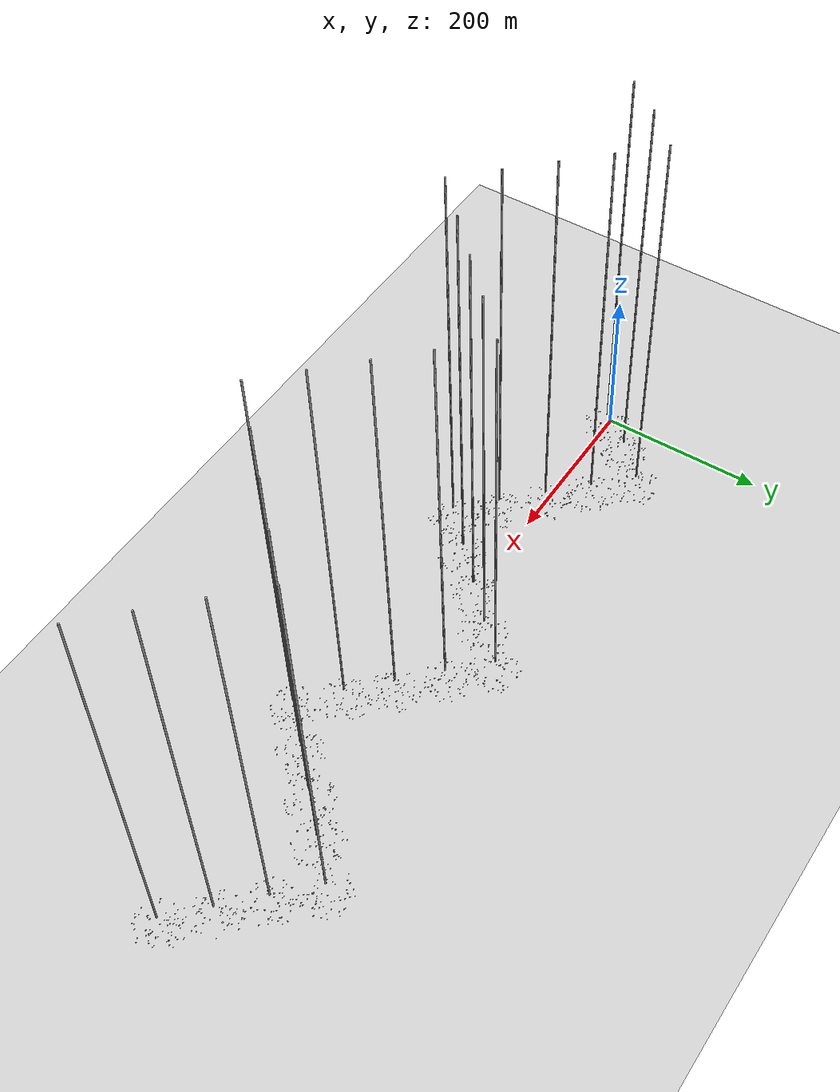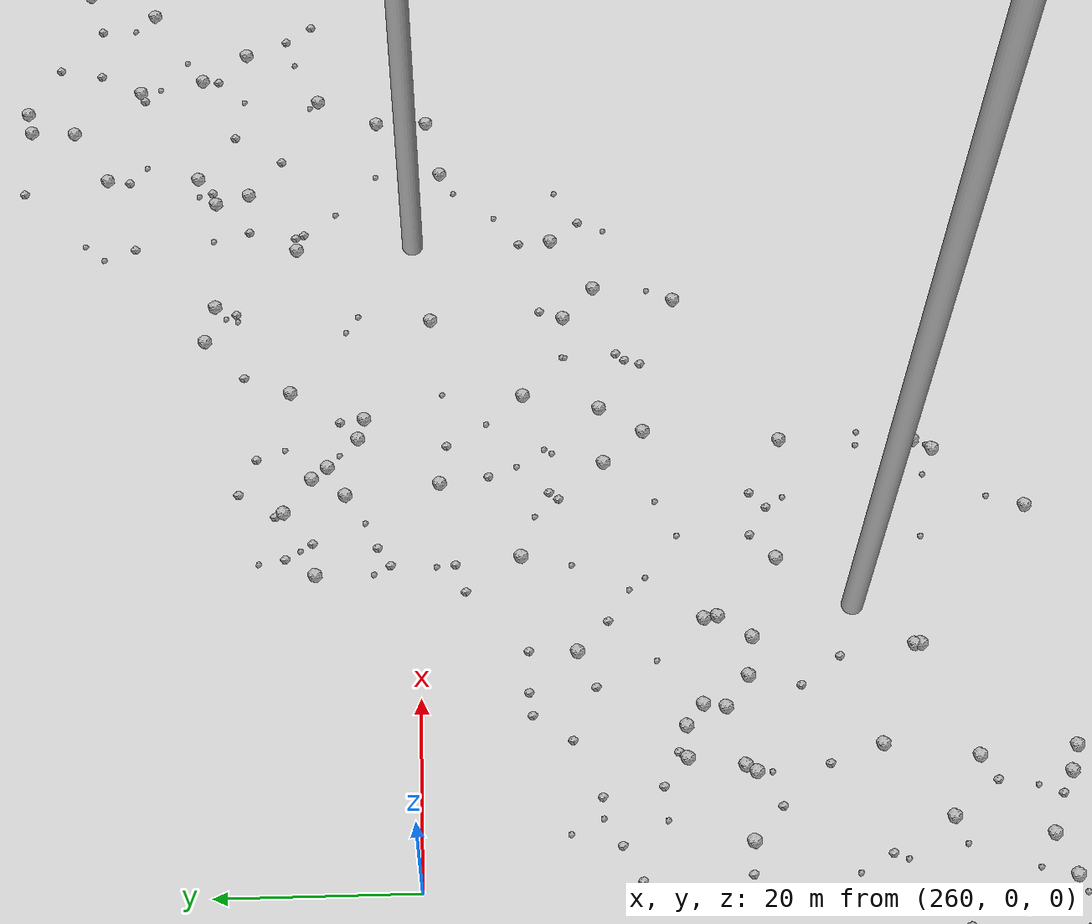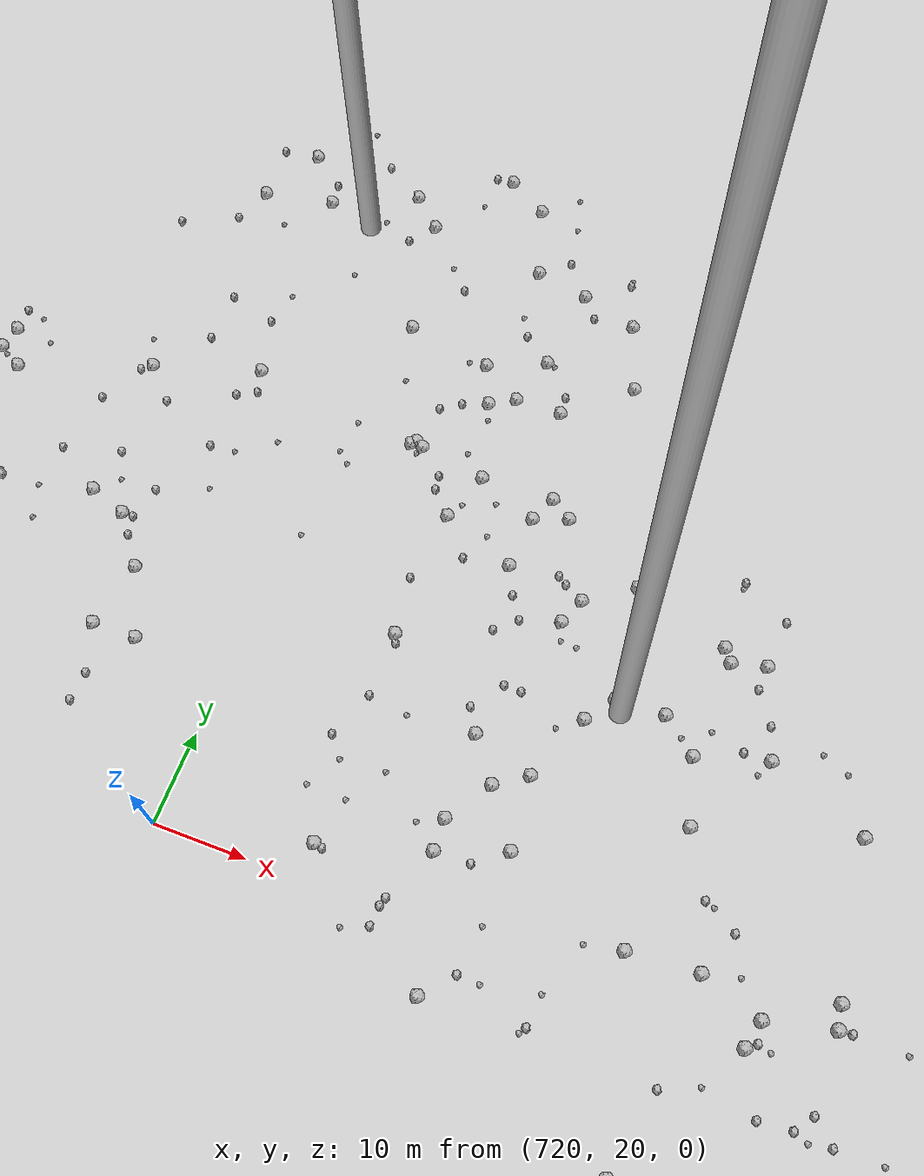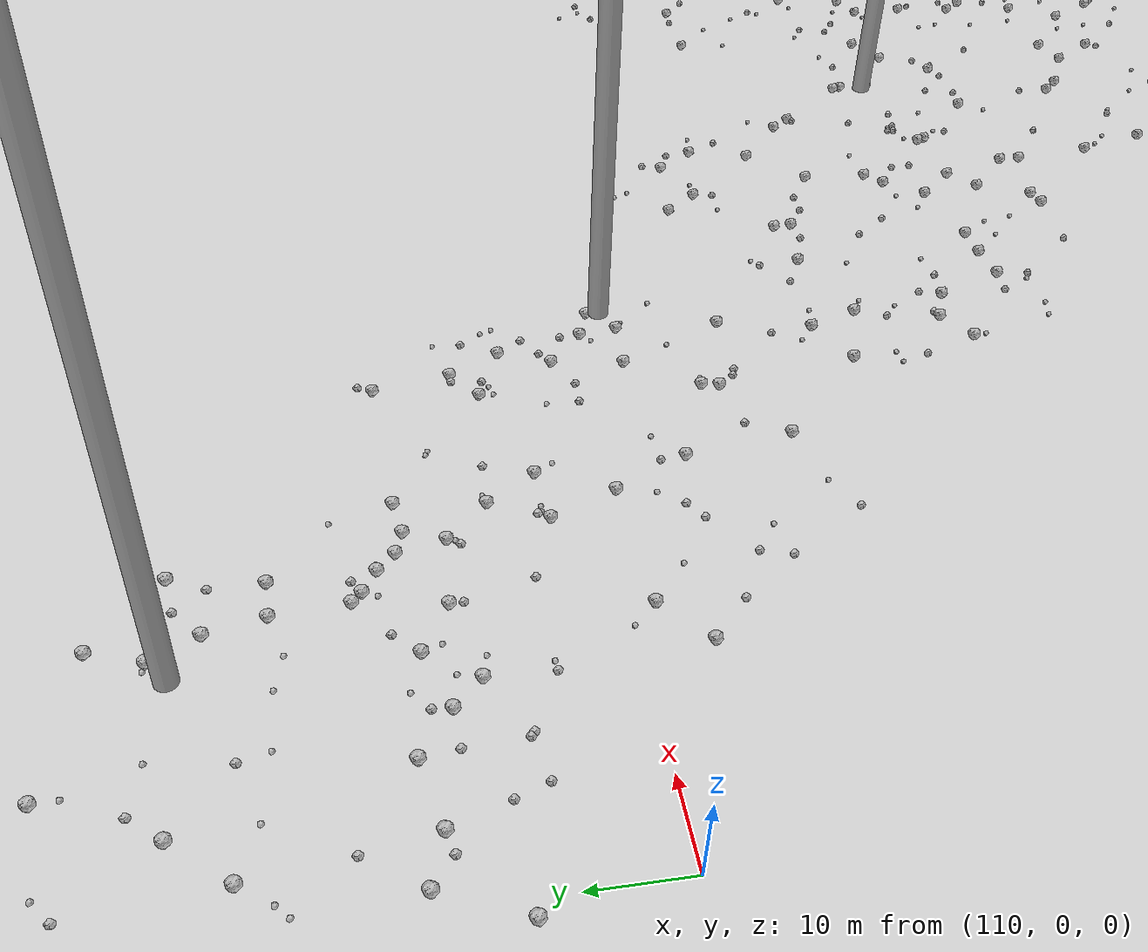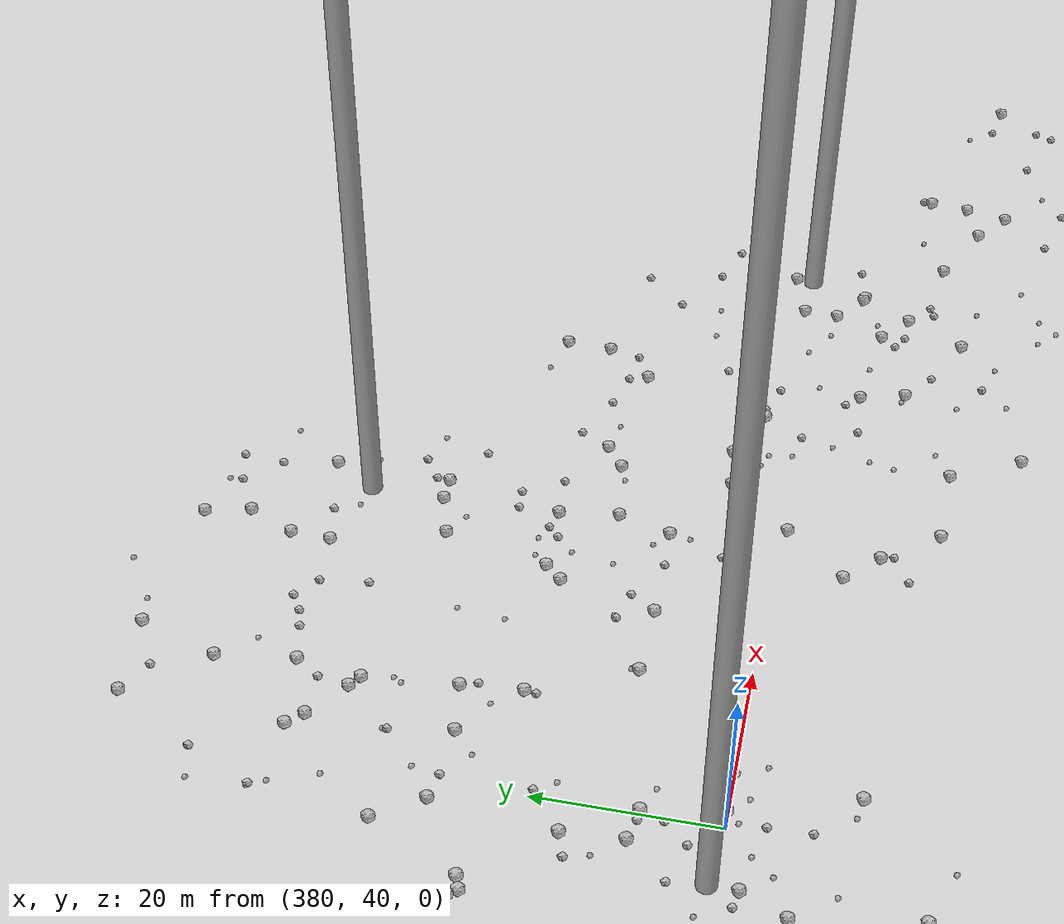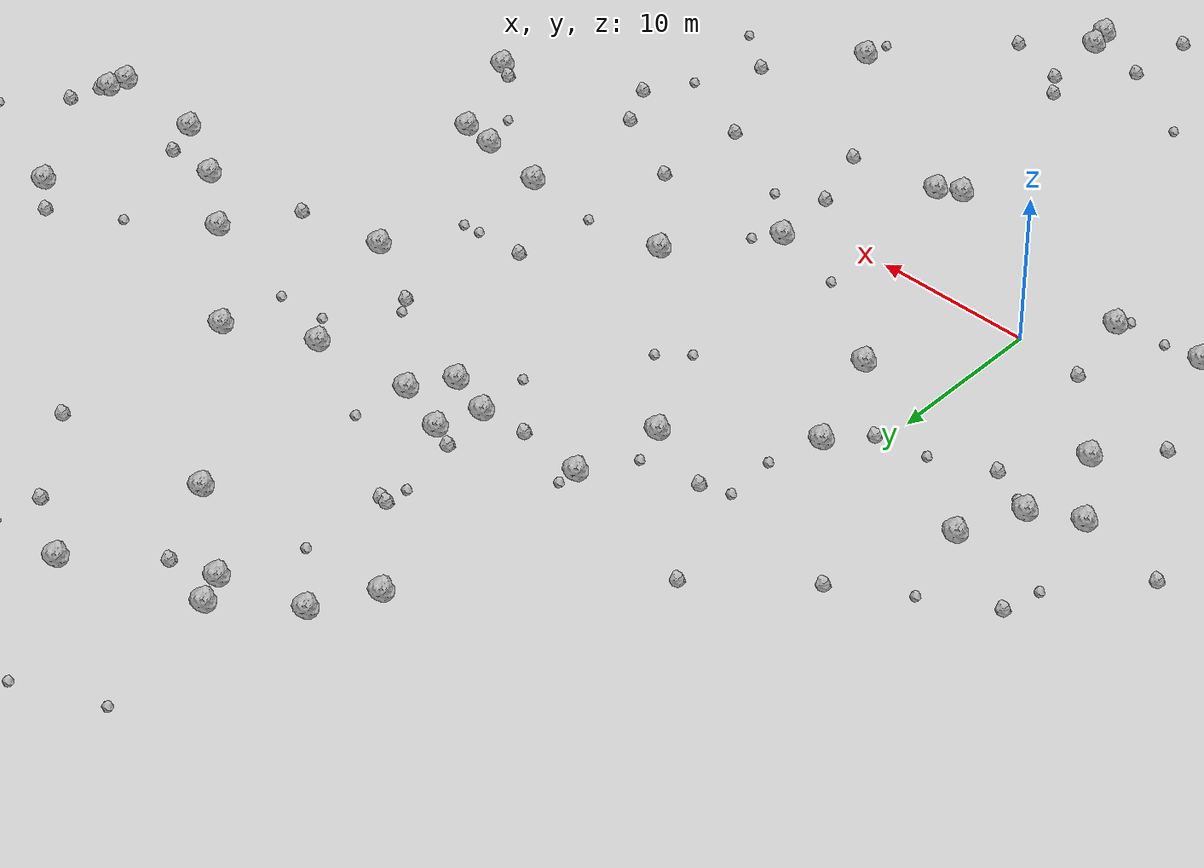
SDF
<sdf version="1.6">
 <world name="default">
  <include><uri>model://custom_ground</uri></include>
  <include><uri>model://sun</uri></include>
  <spherical_coordinates>
   <surface_model>EARTH_WGS84</surface_model>
   <latitude_deg>38.161479</latitude_deg>
   <longitude_deg>-122.454630</longitude_deg>
   <elevation>488.0</elevation>
   <heading_deg>90</heading_deg>
  </spherical_coordinates>
  <model name="rock1_0_0">
   <include><uri>model://rock1</uri><pose>-9.325859273268861 11.395108314160183 0.5 0 0 0</pose></include>
  </model>
  <model name="rock1_0_1">
   <include><uri>model://rock1</uri><pose>32.77272916011381 18.821326434862648 0.5 0 0 0</pose></include>
  </model>
  <model name="rock1_0_2">
   <include><uri>model://rock1</uri><pose>20.494058716048002 8.036670395638183 0.5 0 0 0</pose></include>
  </model>
  <model name="rock1_0_3">
   <include><uri>model://rock1</uri><pose>-9.165816178152784 5.538716321322738 0.5 0 0 0</pose></include>
  </model>
  <model name="rock1_0_4">
   <include><uri>model://rock1</uri><pose>34.89038393754093 7.5048193109880685 0.5 0 0 0</pose></include>
  </model>
  <model name="rock1_0_5">
   <include><uri>model://rock1</uri><pose>24.081980462925678 -14.849077184002226 0.5 0 0 0</pose></include>
  </model>
  <model name="rock1_0_6">
   <include><uri>model://rock1</uri><pose>10.88490199903103 -8.038815499362173 0.5 0 0 0</pose></include>
  </model>
  <model name="rock1_0_7">
   <include><uri>model://rock1</uri><pose>30.420932146796986 8.31368439147991 0.5 0 0 0</pose></include>
  </model>
  <model name="rock1_0_8">
   <include><uri>model://rock1</uri><pose>16.025471272302447 2.2451898496656995 0.5 0 0 0</pose></include>
  </model>
  <model name="rock1_0_9">
   <include><uri>model://rock1</uri><pose>-4.446693546395309 -25.61087649749245 0.5 0 0 0</pose></include>
  </model>
  <model name="rock1_0_10">
   <include><uri>model://rock1</uri><pose>12.208705323214964 -7.2310050316699765 0.5 0 0 0</pose></include>
  </model>
  <model name="rock1_0_11">
   <include><uri>model://rock1</uri><pose>2.5135233519100737 14.421944765956056 0.5 0 0 0</pose></include>
  </model>
  <model name="rock1_0_12">
   <include><uri>model://rock1</uri><pose>17.959134334480666 25.324735297423487 0.5 0 0 0</pose></include>
  </model>
  <model name="rock1_0_13">
   <include><uri>model://rock1</uri><pose>14.369802817539686 -25.350690073815702 0.5 0 0 0</pose></include>
  </model>
  <model name="rock1_0_14">
   <include><uri>model://rock1</uri><pose>20.868182732373143 24.396816842527883 0.5 0 0 0</pose></include>
  </model>
  <model name="rock1_0_15">
   <include><uri>model://rock1</uri><pose>-7.668985724154286 15.28530597783648 0.5 0 0 0</pose></include>
  </model>
  <model name="rock1_0_16">
   <include><uri>model://rock1</uri><pose>37.08834178905631 7.186391828840122 0.5 0 0 0</pose></include>
  </model>
  <model name="rock1_0_17">
   <include><uri>model://rock1</uri><pose>18.8651854831828 28.037462194587967 0.5 0 0 0</pose></include>
  </model>
  <model name="rock1_0_18">
   <include><uri>model://rock1</uri><pose>9.676334513105505 19.94417882393501 0.5 0 0 0</pose></include>
  </model>
  <model name="rock1_0_19">
   <include><uri>model://rock1</uri><pose>39.963123794459506 1.1491976966194954 0.5 0 0 0</pose></include>
  </model>
  <model name="rock1_0_20">
   <include><uri>model://rock1</uri><pose>-3.311976631417256 -4.443405541984745 0.5 0 0 0</pose></include>
  </model>
  <model name="rock1_0_21">
   <include><uri>model://rock1</uri><pose>10.652464035186199 25.46317277084769 0.5 0 0 0</pose></include>
  </model>
  <model name="rock1_0_22">
   <include><uri>model://rock1</uri><pose>5.069408518328014 7.792026259948464 0.5 0 0 0</pose></include>
  </model>
  <model name="rock1_0_23">
   <include><uri>model://rock1</uri><pose>-8.742508466582686 -5.184591756139284 0.5 0 0 0</pose></include>
  </model>
  <model name="rock1_0_24">
   <include><uri>model://rock1</uri><pose>14.625728409789836 -26.738669928540666 0.5 0 0 0</pose></include>
  </model>
  <model name="rock1_0_25">
   <include><uri>model://rock1</uri><pose>-12.198082013211282 9.900188176174645 0.5 0 0 0</pose></include>
  </model>
  <model name="rock1_0_26">
   <include><uri>model://rock1</uri><pose>-12.65587395111057 -4.35016123043259 0.5 0 0 0</pose></include>
  </model>
  <model name="rock2_0_0">
   <include><uri>model://rock2</uri><pose>-17.8799409010483 10.950787790465327 0.3 0 0 0</pose></include>
  </model>
  <model name="rock2_0_1">
   <include><uri>model://rock2</uri><pose>10.549829539883216 -24.709167111648803 0.3 0 0 0</pose></include>
  </model>
  <model name="rock2_0_2">
   <include><uri>model://rock2</uri><pose>34.60235385883319 -14.994394415011579 0.3 0 0 0</pose></include>
  </model>
  <model name="rock2_0_3">
   <include><uri>model://rock2</uri><pose>26.15279913652845 13.871309525150672 0.3 0 0 0</pose></include>
  </model>
  <model name="rock2_0_4">
   <include><uri>model://rock2</uri><pose>0.5409424549066912 12.16054857589652 0.3 0 0 0</pose></include>
  </model>
  <model name="rock2_0_5">
   <include><uri>model://rock2</uri><pose>16.370242271537272 -2.0737238437990726 0.3 0 0 0</pose></include>
  </model>
  <model name="rock2_0_6">
   <include><uri>model://rock2</uri><pose>13.031889078616693 -19.600325787458896 0.3 0 0 0</pose></include>
  </model>
  <model name="rock2_0_7">
   <include><uri>model://rock2</uri><pose>38.86930375528399 1.7307108480326399 0.3 0 0 0</pose></include>
  </model>
  <model name="rock2_0_8">
   <include><uri>model://rock2</uri><pose>-4.502110147065704 0.519439138335251 0.3 0 0 0</pose></include>
  </model>
  <model name="rock2_0_9">
   <include><uri>model://rock2</uri><pose>17.84963579860517 -6.374676612121043 0.3 0 0 0</pose></include>
  </model>
  <model name="rock2_0_10">
   <include><uri>model://rock2</uri><pose>31.70390754713133 -2.775661783326573 0.3 0 0 0</pose></include>
  </model>
  <model name="rock2_0_11">
   <include><uri>model://rock2</uri><pose>-5.102845605135602 23.085767348932443 0.3 0 0 0</pose></include>
  </model>
  <model name="rock2_0_12">
   <include><uri>model://rock2</uri><pose>-19.253556270881262 -4.656369448009599 0.3 0 0 0</pose></include>
  </model>
  <model name="rock2_0_13">
   <include><uri>model://rock2</uri><pose>-3.9273610354467756 -19.665570519971027 0.3 0 0 0</pose></include>
  </model>
  <model name="rock2_0_14">
   <include><uri>model://rock2</uri><pose>14.0269032404766 -21.011562440827902 0.3 0 0 0</pose></include>
  </model>
  <model name="rock2_0_15">
   <include><uri>model://rock2</uri><pose>-13.260986676541012 18.145455253565466 0.3 0 0 0</pose></include>
  </model>
  <model name="rock2_0_16">
   <include><uri>model://rock2</uri><pose>4.861513205942071 -27.974720390312612 0.3 0 0 0</pose></include>
  </model>
  <model name="rock2_0_17">
   <include><uri>model://rock2</uri><pose>25.057790312450898 2.5351799585521633 0.3 0 0 0</pose></include>
  </model>
  <model name="rock2_0_18">
   <include><uri>model://rock2</uri><pose>27.954919649679837 -9.464542206046485 0.3 0 0 0</pose></include>
  </model>
  <model name="rock2_0_19">
   <include><uri>model://rock2</uri><pose>0.7840664554753403 28.02637640429807 0.3 0 0 0</pose></include>
  </model>
  <model name="rock2_0_20">
   <include><uri>model://rock2</uri><pose>17.836531842781312 -22.24457372562164 0.3 0 0 0</pose></include>
  </model>
  <model name="rock2_0_21">
   <include><uri>model://rock2</uri><pose>-12.029163968752215 2.221237230681325 0.3 0 0 0</pose></include>
  </model>
  <model name="rock2_0_22">
   <include><uri>model://rock2</uri><pose>24.703523809423274 -3.386550913699754 0.3 0 0 0</pose></include>
  </model>
  <model name="rock2_0_23">
   <include><uri>model://rock2</uri><pose>30.255165122852667 -0.03410394703698216 0.3 0 0 0</pose></include>
  </model>
  <model name="rock2_0_24">
   <include><uri>model://rock2</uri><pose>-6.252732623995591 9.850617056484062 0.3 0 0 0</pose></include>
  </model>
  <model name="rock2_0_25">
   <include><uri>model://rock2</uri><pose>10.271568132064196 -29.145145655219213 0.3 0 0 0</pose></include>
  </model>
  <model name="rock2_0_26">
   <include><uri>model://rock2</uri><pose>4.990154005364854 21.653377611294715 0.3 0 0 0</pose></include>
  </model>
  <model name="rock3_0_0">
   <include><uri>model://rock3</uri><pose>17.182094434907526 3.5428621270636853 0.2 0 0 0</pose></include>
  </model>
  <model name="rock3_0_1">
   <include><uri>model://rock3</uri><pose>18.146931699916735 21.752808638489135 0.2 0 0 0</pose></include>
  </model>
  <model name="rock3_0_2">
   <include><uri>model://rock3</uri><pose>8.735691609603215 22.29495806142831 0.2 0 0 0</pose></include>
  </model>
  <model name="rock3_0_3">
   <include><uri>model://rock3</uri><pose>25.403453814979407 8.72551856994675 0.2 0 0 0</pose></include>
  </model>
  <model name="rock3_0_4">
   <include><uri>model://rock3</uri><pose>-5.572813345681368 -18.239281273946112 0.2 0 0 0</pose></include>
  </model>
  <model name="rock3_0_5">
   <include><uri>model://rock3</uri><pose>35.715701546263226 4.9253790221809695 0.2 0 0 0</pose></include>
  </model>
  <model name="rock3_0_6">
   <include><uri>model://rock3</uri><pose>-8.456783466329153 10.829045693292883 0.2 0 0 0</pose></include>
  </model>
  <model name="rock3_0_7">
   <include><uri>model://rock3</uri><pose>30.820561977251486 -11.643811960863587 0.2 0 0 0</pose></include>
  </model>
  <model name="rock3_0_8">
   <include><uri>model://rock3</uri><pose>12.585461517901216 13.7219471492782 0.2 0 0 0</pose></include>
  </model>
  <model name="rock3_0_9">
   <include><uri>model://rock3</uri><pose>-0.6884026025642171 -27.5547886665812 0.2 0 0 0</pose></include>
  </model>
  <model name="rock3_0_10">
   <include><uri>model://rock3</uri><pose>29.983966981179535 -5.618255158017973 0.2 0 0 0</pose></include>
  </model>
  <model name="rock3_0_11">
   <include><uri>model://rock3</uri><pose>-9.23183750589648 20.398056411641782 0.2 0 0 0</pose></include>
  </model>
  <model name="rock3_0_12">
   <include><uri>model://rock3</uri><pose>10.728807469213265 26.607527040775153 0.2 0 0 0</pose></include>
  </model>
  <model name="rock3_0_13">
   <include><uri>model://rock3</uri><pose>-13.82013741783274 15.715351400334505 0.2 0 0 0</pose></include>
  </model>
  <model name="rock3_0_14">
   <include><uri>model://rock3</uri><pose>29.285671127383758 13.943056735592734 0.2 0 0 0</pose></include>
  </model>
  <model name="rock3_0_15">
   <include><uri>model://rock3</uri><pose>5.259641797622244 -21.538846942104794 0.2 0 0 0</pose></include>
  </model>
  <model name="rock3_0_16">
   <include><uri>model://rock3</uri><pose>-6.721764024303514 -11.710366055891328 0.2 0 0 0</pose></include>
  </model>
  <model name="rock3_0_17">
   <include><uri>model://rock3</uri><pose>-2.6315402233158096 11.453593278941604 0.2 0 0 0</pose></include>
  </model>
  <model name="rock3_0_18">
   <include><uri>model://rock3</uri><pose>3.2176005154551035 20.969178978004166 0.2 0 0 0</pose></include>
  </model>
  <model name="rock3_0_19">
   <include><uri>model://rock3</uri><pose>3.4263359172180117 17.679491604915576 0.2 0 0 0</pose></include>
  </model>
  <model name="rock3_0_20">
   <include><uri>model://rock3</uri><pose>11.11003345894336 3.4832607152235227 0.2 0 0 0</pose></include>
  </model>
  <model name="rock3_0_21">
   <include><uri>model://rock3</uri><pose>14.211679646782422 15.164891869126919 0.2 0 0 0</pose></include>
  </model>
  <model name="rock3_0_22">
   <include><uri>model://rock3</uri><pose>23.783387203346855 -16.588300774890392 0.2 0 0 0</pose></include>
  </model>
  <model name="rock3_0_23">
   <include><uri>model://rock3</uri><pose>-3.8551681791164008 -5.252708302319977 0.2 0 0 0</pose></include>
  </model>
  <model name="rock3_0_24">
   <include><uri>model://rock3</uri><pose>-8.893787028156703 -20.92766767191652 0.2 0 0 0</pose></include>
  </model>
  <model name="rock3_0_25">
   <include><uri>model://rock3</uri><pose>19.001827625658805 -0.59060037727523 0.2 0 0 0</pose></include>
  </model>
  <model name="rock3_0_26">
   <include><uri>model://rock3</uri><pose>-6.459629180195456 -4.985666425627574 0.2 0 0 0</pose></include>
  </model>
  <model name="rock1_1_0">
   <include><uri>model://rock1</uri><pose>24.736658606772295 40.08819776499921 0.5 0 0 0</pose></include>
  </model>
  <model name="rock1_1_1">
   <include><uri>model://rock1</uri><pose>56.13648049748564 19.22073642414545 0.5 0 0 0</pose></include>
  </model>
  <model name="rock1_1_2">
   <include><uri>model://rock1</uri><pose>43.0100822144433 56.598307300685796 0.5 0 0 0</pose></include>
  </model>
  <model name="rock1_1_3">
   <include><uri>model://rock1</uri><pose>49.45814809548653 18.61779612843468 0.5 0 0 0</pose></include>
  </model>
  <model name="rock1_1_4">
   <include><uri>model://rock1</uri><pose>28.98323399167849 27.37047632127359 0.5 0 0 0</pose></include>
  </model>
  <model name="rock1_1_5">
   <include><uri>model://rock1</uri><pose>45.104335748690886 20.912568754303038 0.5 0 0 0</pose></include>
  </model>
  <model name="rock1_1_6">
   <include><uri>model://rock1</uri><pose>44.10920672232046 53.64889155090923 0.5 0 0 0</pose></include>
  </model>
  <model name="rock1_1_7">
   <include><uri>model://rock1</uri><pose>11.635428630760764 39.245233351146915 0.5 0 0 0</pose></include>
  </model>
  <model name="rock1_1_8">
   <include><uri>model://rock1</uri><pose>48.15554454757732 59.63042927273735 0.5 0 0 0</pose></include>
  </model>
  <model name="rock1_1_9">
   <include><uri>model://rock1</uri><pose>56.86920154710236 33.984393851813664 0.5 0 0 0</pose></include>
  </model>
  <model name="rock1_1_10">
   <include><uri>model://rock1</uri><pose>60.77443174957661 31.12680133377436 0.5 0 0 0</pose></include>
  </model>
  <model name="rock1_1_11">
   <include><uri>model://rock1</uri><pose>41.2135319206578 44.77564079231868 0.5 0 0 0</pose></include>
  </model>
  <model name="rock1_1_12">
   <include><uri>model://rock1</uri><pose>40.94504378355002 24.041661979103985 0.5 0 0 0</pose></include>
  </model>
  <model name="rock1_1_13">
   <include><uri>model://rock1</uri><pose>54.11526542792514 46.812301028998235 0.5 0 0 0</pose></include>
  </model>
  <model name="rock1_1_14">
   <include><uri>model://rock1</uri><pose>57.0198696399313 63.987367657297426 0.5 0 0 0</pose></include>
  </model>
  <model name="rock1_1_15">
   <include><uri>model://rock1</uri><pose>34.15820678986054 30.00082020847444 0.5 0 0 0</pose></include>
  </model>
  <model name="rock1_1_16">
   <include><uri>model://rock1</uri><pose>22.417132243062085 26.82325506409449 0.5 0 0 0</pose></include>
  </model>
  <model name="rock1_1_17">
   <include><uri>model://rock1</uri><pose>51.8871705178007 28.03315129739368 0.5 0 0 0</pose></include>
  </model>
  <model name="rock1_1_18">
   <include><uri>model://rock1</uri><pose>57.45888633301859 42.56919821644671 0.5 0 0 0</pose></include>
  </model>
  <model name="rock1_1_19">
   <include><uri>model://rock1</uri><pose>13.624094155775378 42.83635529197777 0.5 0 0 0</pose></include>
  </model>
  <model name="rock1_1_20">
   <include><uri>model://rock1</uri><pose>36.044786167535904 67.70675713964323 0.5 0 0 0</pose></include>
  </model>
  <model name="rock1_1_21">
   <include><uri>model://rock1</uri><pose>18.86887017078181 44.311996402545205 0.5 0 0 0</pose></include>
  </model>
  <model name="rock1_1_22">
   <include><uri>model://rock1</uri><pose>17.92421698538301 46.13449220239775 0.5 0 0 0</pose></include>
  </model>
  <model name="rock1_1_23">
   <include><uri>model://rock1</uri><pose>61.94299346942742 48.73924467593211 0.5 0 0 0</pose></include>
  </model>
  <model name="rock1_1_24">
   <include><uri>model://rock1</uri><pose>67.50792497630619 32.62316146213423 0.5 0 0 0</pose></include>
  </model>
  <model name="rock1_1_25">
   <include><uri>model://rock1</uri><pose>26.27862759263629 49.0868602960232 0.5 0 0 0</pose></include>
  </model>
  <model name="rock1_1_26">
   <include><uri>model://rock1</uri><pose>55.90190238141288 18.003640538394315 0.5 0 0 0</pose></include>
  </model>
  <model name="rock2_1_0">
   <include><uri>model://rock2</uri><pose>36.48594269646885 51.914019411974714 0.3 0 0 0</pose></include>
  </model>
  <model name="rock2_1_1">
   <include><uri>model://rock2</uri><pose>68.90419645386166 33.83438015932661 0.3 0 0 0</pose></include>
  </model>
  <model name="rock2_1_2">
   <include><uri>model://rock2</uri><pose>56.935124321157524 21.54423043508906 0.3 0 0 0</pose></include>
  </model>
  <model name="rock2_1_3">
   <include><uri>model://rock2</uri><pose>38.32235893401917 19.697509600343068 0.3 0 0 0</pose></include>
  </model>
  <model name="rock2_1_4">
   <include><uri>model://rock2</uri><pose>31.96348854433248 66.0647618603654 0.3 0 0 0</pose></include>
  </model>
  <model name="rock2_1_5">
   <include><uri>model://rock2</uri><pose>16.941578370321153 34.07163539924166 0.3 0 0 0</pose></include>
  </model>
  <model name="rock2_1_6">
   <include><uri>model://rock2</uri><pose>56.39621750051992 19.638659228174014 0.3 0 0 0</pose></include>
  </model>
  <model name="rock2_1_7">
   <include><uri>model://rock2</uri><pose>16.450888748938713 34.151676182045236 0.3 0 0 0</pose></include>
  </model>
  <model name="rock2_1_8">
   <include><uri>model://rock2</uri><pose>53.901557031886 62.52947397525666 0.3 0 0 0</pose></include>
  </model>
  <model name="rock2_1_9">
   <include><uri>model://rock2</uri><pose>33.55273753536821 65.83396627779896 0.3 0 0 0</pose></include>
  </model>
  <model name="rock2_1_10">
   <include><uri>model://rock2</uri><pose>30.428108783888398 46.56052741170269 0.3 0 0 0</pose></include>
  </model>
  <model name="rock2_1_11">
   <include><uri>model://rock2</uri><pose>48.37688380805594 20.84414847890564 0.3 0 0 0</pose></include>
  </model>
  <model name="rock2_1_12">
   <include><uri>model://rock2</uri><pose>66.13895840663886 35.66208571299924 0.3 0 0 0</pose></include>
  </model>
  <model name="rock2_1_13">
   <include><uri>model://rock2</uri><pose>17.309507253143344 28.61102792929729 0.3 0 0 0</pose></include>
  </model>
  <model name="rock2_1_14">
   <include><uri>model://rock2</uri><pose>49.64995662338113 29.77598731682051 0.3 0 0 0</pose></include>
  </model>
  <model name="rock2_1_15">
   <include><uri>model://rock2</uri><pose>21.664972372122527 45.13312618844999 0.3 0 0 0</pose></include>
  </model>
  <model name="rock2_1_16">
   <include><uri>model://rock2</uri><pose>18.89741223529638 60.19472180896868 0.3 0 0 0</pose></include>
  </model>
  <model name="rock2_1_17">
   <include><uri>model://rock2</uri><pose>49.546097215183835 58.93602021494169 0.3 0 0 0</pose></include>
  </model>
  <model name="rock2_1_18">
   <include><uri>model://rock2</uri><pose>68.41290984383451 38.525554753139595 0.3 0 0 0</pose></include>
  </model>
  <model name="rock2_1_19">
   <include><uri>model://rock2</uri><pose>28.00873572308791 21.282061099986727 0.3 0 0 0</pose></include>
  </model>
  <model name="rock2_1_20">
   <include><uri>model://rock2</uri><pose>53.0551850069284 66.76863490951652 0.3 0 0 0</pose></include>
  </model>
  <model name="rock2_1_21">
   <include><uri>model://rock2</uri><pose>61.78718397888477 31.522958365521923 0.3 0 0 0</pose></include>
  </model>
  <model name="rock2_1_22">
   <include><uri>model://rock2</uri><pose>31.00589948826469 49.42207692344334 0.3 0 0 0</pose></include>
  </model>
  <model name="rock2_1_23">
   <include><uri>model://rock2</uri><pose>34.8447037157998 41.210186827429574 0.3 0 0 0</pose></include>
  </model>
  <model name="rock2_1_24">
   <include><uri>model://rock2</uri><pose>14.93941355548406 25.013238088755262 0.3 0 0 0</pose></include>
  </model>
  <model name="rock2_1_25">
   <include><uri>model://rock2</uri><pose>66.73548380721522 50.18270180634129 0.3 0 0 0</pose></include>
  </model>
  <model name="rock2_1_26">
   <include><uri>model://rock2</uri><pose>57.57260563230869 36.19780333583209 0.3 0 0 0</pose></include>
  </model>
  <model name="rock3_1_0">
   <include><uri>model://rock3</uri><pose>56.78404334387705 38.35288847828748 0.2 0 0 0</pose></include>
  </model>
  <model name="rock3_1_1">
   <include><uri>model://rock3</uri><pose>48.92762111578016 55.73716623984174 0.2 0 0 0</pose></include>
  </model>
  <model name="rock3_1_2">
   <include><uri>model://rock3</uri><pose>20.98581518540678 56.7589637056757 0.2 0 0 0</pose></include>
  </model>
  <model name="rock3_1_3">
   <include><uri>model://rock3</uri><pose>52.483405731664526 48.56400955829558 0.2 0 0 0</pose></include>
  </model>
  <model name="rock3_1_4">
   <include><uri>model://rock3</uri><pose>22.842733917328694 30.2258304534306 0.2 0 0 0</pose></include>
  </model>
  <model name="rock3_1_5">
   <include><uri>model://rock3</uri><pose>37.77337635020706 50.59418077092983 0.2 0 0 0</pose></include>
  </model>
  <model name="rock3_1_6">
   <include><uri>model://rock3</uri><pose>51.23614383699813 39.558520315970696 0.2 0 0 0</pose></include>
  </model>
  <model name="rock3_1_7">
   <include><uri>model://rock3</uri><pose>56.28628265363057 43.69323063198382 0.2 0 0 0</pose></include>
  </model>
  <model name="rock3_1_8">
   <include><uri>model://rock3</uri><pose>27.396678219709464 22.145510031430156 0.2 0 0 0</pose></include>
  </model>
  <model name="rock3_1_9">
   <include><uri>model://rock3</uri><pose>21.82778077605182 59.281392625527616 0.2 0 0 0</pose></include>
  </model>
  <model name="rock3_1_10">
   <include><uri>model://rock3</uri><pose>30.31716825935874 25.642327523151124 0.2 0 0 0</pose></include>
  </model>
  <model name="rock3_1_11">
   <include><uri>model://rock3</uri><pose>16.374722538560153 32.628628004161925 0.2 0 0 0</pose></include>
  </model>
  <model name="rock3_1_12">
   <include><uri>model://rock3</uri><pose>53.1933553643675 56.829934335136585 0.2 0 0 0</pose></include>
  </model>
  <model name="rock3_1_13">
   <include><uri>model://rock3</uri><pose>65.20284144315659 37.124477720914115 0.2 0 0 0</pose></include>
  </model>
  <model name="rock3_1_14">
   <include><uri>model://rock3</uri><pose>59.92876263906135 24.649361716209597 0.2 0 0 0</pose></include>
  </model>
  <model name="rock3_1_15">
   <include><uri>model://rock3</uri><pose>15.844260958389548 54.51219912490812 0.2 0 0 0</pose></include>
  </model>
  <model name="rock3_1_16">
   <include><uri>model://rock3</uri><pose>50.57700638821369 35.91308520404462 0.2 0 0 0</pose></include>
  </model>
  <model name="rock3_1_17">
   <include><uri>model://rock3</uri><pose>45.54178184545895 27.247685839575205 0.2 0 0 0</pose></include>
  </model>
  <model name="rock3_1_18">
   <include><uri>model://rock3</uri><pose>58.29975390584182 60.5109175018827 0.2 0 0 0</pose></include>
  </model>
  <model name="rock3_1_19">
   <include><uri>model://rock3</uri><pose>56.913700077543375 53.10466465305245 0.2 0 0 0</pose></include>
  </model>
  <model name="rock3_1_20">
   <include><uri>model://rock3</uri><pose>32.643132981438306 65.46680273107901 0.2 0 0 0</pose></include>
  </model>
  <model name="rock3_1_21">
   <include><uri>model://rock3</uri><pose>33.4836409147516 25.85530313606736 0.2 0 0 0</pose></include>
  </model>
  <model name="rock3_1_22">
   <include><uri>model://rock3</uri><pose>17.018689963634266 39.513156745535696 0.2 0 0 0</pose></include>
  </model>
  <model name="rock3_1_23">
   <include><uri>model://rock3</uri><pose>43.366140094266704 55.957609856425535 0.2 0 0 0</pose></include>
  </model>
  <model name="rock3_1_24">
   <include><uri>model://rock3</uri><pose>47.58028008379887 48.13905816951465 0.2 0 0 0</pose></include>
  </model>
  <model name="rock3_1_25">
   <include><uri>model://rock3</uri><pose>30.438476016683452 14.033968168232594 0.2 0 0 0</pose></include>
  </model>
  <model name="rock3_1_26">
   <include><uri>model://rock3</uri><pose>42.32176746054888 47.63031531414653 0.2 0 0 0</pose></include>
  </model>
  <model name="rock1_2_0">
   <include><uri>model://rock1</uri><pose>65.39954169754787 76.59407265086357 0.5 0 0 0</pose></include>
  </model>
  <model name="rock1_2_1">
   <include><uri>model://rock1</uri><pose>89.66643274024091 78.65964665383598 0.5 0 0 0</pose></include>
  </model>
  <model name="rock1_2_2">
   <include><uri>model://rock1</uri><pose>70.37888497306722 71.17405624202951 0.5 0 0 0</pose></include>
  </model>
  <model name="rock1_2_3">
   <include><uri>model://rock1</uri><pose>70.52109158183332 62.97681464248106 0.5 0 0 0</pose></include>
  </model>
  <model name="rock1_2_4">
   <include><uri>model://rock1</uri><pose>101.31705117495679 75.64040169723138 0.5 0 0 0</pose></include>
  </model>
  <model name="rock1_2_5">
   <include><uri>model://rock1</uri><pose>78.60747459173159 85.83327453770382 0.5 0 0 0</pose></include>
  </model>
  <model name="rock1_2_6">
   <include><uri>model://rock1</uri><pose>81.55407038501288 58.63975115484443 0.5 0 0 0</pose></include>
  </model>
  <model name="rock1_2_7">
   <include><uri>model://rock1</uri><pose>73.43962306185128 52.4439484008241 0.5 0 0 0</pose></include>
  </model>
  <model name="rock1_2_8">
   <include><uri>model://rock1</uri><pose>88.68190704085357 97.42035610728844 0.5 0 0 0</pose></include>
  </model>
  <model name="rock1_2_9">
   <include><uri>model://rock1</uri><pose>90.02226037415198 75.83810665471695 0.5 0 0 0</pose></include>
  </model>
  <model name="rock1_2_10">
   <include><uri>model://rock1</uri><pose>99.88113299242276 90.13640975103584 0.5 0 0 0</pose></include>
  </model>
  <model name="rock1_2_11">
   <include><uri>model://rock1</uri><pose>86.14190201980102 69.24047878416224 0.5 0 0 0</pose></include>
  </model>
  <model name="rock1_2_12">
   <include><uri>model://rock1</uri><pose>77.71986699435708 80.02448642350011 0.5 0 0 0</pose></include>
  </model>
  <model name="rock1_2_13">
   <include><uri>model://rock1</uri><pose>81.93802396626808 66.66127122779719 0.5 0 0 0</pose></include>
  </model>
  <model name="rock1_2_14">
   <include><uri>model://rock1</uri><pose>54.42466882153771 88.6221982781883 0.5 0 0 0</pose></include>
  </model>
  <model name="rock1_2_15">
   <include><uri>model://rock1</uri><pose>54.42982005527615 94.93451096336263 0.5 0 0 0</pose></include>
  </model>
  <model name="rock1_2_16">
   <include><uri>model://rock1</uri><pose>65.32703315272096 92.45596584820203 0.5 0 0 0</pose></include>
  </model>
  <model name="rock1_2_17">
   <include><uri>model://rock1</uri><pose>85.88569189493819 103.85965190169516 0.5 0 0 0</pose></include>
  </model>
  <model name="rock1_2_18">
   <include><uri>model://rock1</uri><pose>87.20075671720154 104.75627407777884 0.5 0 0 0</pose></include>
  </model>
  <model name="rock1_2_19">
   <include><uri>model://rock1</uri><pose>105.10327964499882 75.40911516839759 0.5 0 0 0</pose></include>
  </model>
  <model name="rock1_2_20">
   <include><uri>model://rock1</uri><pose>77.96746077414811 102.35829288467347 0.5 0 0 0</pose></include>
  </model>
  <model name="rock1_2_21">
   <include><uri>model://rock1</uri><pose>66.38291117630524 81.71270288673801 0.5 0 0 0</pose></include>
  </model>
  <model name="rock1_2_22">
   <include><uri>model://rock1</uri><pose>102.8276239924711 67.98170034517369 0.5 0 0 0</pose></include>
  </model>
  <model name="rock1_2_23">
   <include><uri>model://rock1</uri><pose>91.73003124165717 97.08807035139273 0.5 0 0 0</pose></include>
  </model>
  <model name="rock1_2_24">
   <include><uri>model://rock1</uri><pose>89.15577729641129 103.00631502363721 0.5 0 0 0</pose></include>
  </model>
  <model name="rock1_2_25">
   <include><uri>model://rock1</uri><pose>109.63921154172323 76.7827635774685 0.5 0 0 0</pose></include>
  </model>
  <model name="rock1_2_26">
   <include><uri>model://rock1</uri><pose>84.55489339551445 50.5077657282904 0.5 0 0 0</pose></include>
  </model>
  <model name="rock2_2_0">
   <include><uri>model://rock2</uri><pose>97.24749643647463 97.43026381767518 0.3 0 0 0</pose></include>
  </model>
  <model name="rock2_2_1">
   <include><uri>model://rock2</uri><pose>87.9637600647969 75.4754039672264 0.3 0 0 0</pose></include>
  </model>
  <model name="rock2_2_2">
   <include><uri>model://rock2</uri><pose>55.187081865580375 86.67576428082342 0.3 0 0 0</pose></include>
  </model>
  <model name="rock2_2_3">
   <include><uri>model://rock2</uri><pose>107.72107368611891 70.72996399324035 0.3 0 0 0</pose></include>
  </model>
  <model name="rock2_2_4">
   <include><uri>model://rock2</uri><pose>76.94337666453396 103.43920060903828 0.3 0 0 0</pose></include>
  </model>
  <model name="rock2_2_5">
   <include><uri>model://rock2</uri><pose>105.47878222489476 84.42387181050103 0.3 0 0 0</pose></include>
  </model>
  <model name="rock2_2_6">
   <include><uri>model://rock2</uri><pose>91.92692756375928 84.70114383869438 0.3 0 0 0</pose></include>
  </model>
  <model name="rock2_2_7">
   <include><uri>model://rock2</uri><pose>57.78484939334023 77.41681413243207 0.3 0 0 0</pose></include>
  </model>
  <model name="rock2_2_8">
   <include><uri>model://rock2</uri><pose>99.99259660815167 78.17817937058271 0.3 0 0 0</pose></include>
  </model>
  <model name="rock2_2_9">
   <include><uri>model://rock2</uri><pose>58.43255464250816 60.136618759552384 0.3 0 0 0</pose></include>
  </model>
  <model name="rock2_2_10">
   <include><uri>model://rock2</uri><pose>55.658659095032526 75.048275953429 0.3 0 0 0</pose></include>
  </model>
  <model name="rock2_2_11">
   <include><uri>model://rock2</uri><pose>103.75431951783914 95.85673217652607 0.3 0 0 0</pose></include>
  </model>
  <model name="rock2_2_12">
   <include><uri>model://rock2</uri><pose>61.637070738594154 80.58532225220482 0.3 0 0 0</pose></include>
  </model>
  <model name="rock2_2_13">
   <include><uri>model://rock2</uri><pose>55.834254718156885 65.8711942317109 0.3 0 0 0</pose></include>
  </model>
  <model name="rock2_2_14">
   <include><uri>model://rock2</uri><pose>71.68076943191856 84.27216227492121 0.3 0 0 0</pose></include>
  </model>
  <model name="rock2_2_15">
   <include><uri>model://rock2</uri><pose>83.65243754045608 59.29772322865415 0.3 0 0 0</pose></include>
  </model>
  <model name="rock2_2_16">
   <include><uri>model://rock2</uri><pose>94.9556630102679 79.70246487987987 0.3 0 0 0</pose></include>
  </model>
  <model name="rock2_2_17">
   <include><uri>model://rock2</uri><pose>80.92667846872851 93.3257953126238 0.3 0 0 0</pose></include>
  </model>
  <model name="rock2_2_18">
   <include><uri>model://rock2</uri><pose>89.14270363903168 63.28249260551246 0.3 0 0 0</pose></include>
  </model>
  <model name="rock2_2_19">
   <include><uri>model://rock2</uri><pose>61.14421423971483 58.70585303084496 0.3 0 0 0</pose></include>
  </model>
  <model name="rock2_2_20">
   <include><uri>model://rock2</uri><pose>55.54941439413897 93.18491781714278 0.3 0 0 0</pose></include>
  </model>
  <model name="rock2_2_21">
   <include><uri>model://rock2</uri><pose>55.60394823798412 67.00776521230739 0.3 0 0 0</pose></include>
  </model>
  <model name="rock2_2_22">
   <include><uri>model://rock2</uri><pose>100.32292096474411 78.08527920757402 0.3 0 0 0</pose></include>
  </model>
  <model name="rock2_2_23">
   <include><uri>model://rock2</uri><pose>63.94754929859627 59.77974711777158 0.3 0 0 0</pose></include>
  </model>
  <model name="rock2_2_24">
   <include><uri>model://rock2</uri><pose>102.26176488179001 93.77078052487582 0.3 0 0 0</pose></include>
  </model>
  <model name="rock2_2_25">
   <include><uri>model://rock2</uri><pose>98.4171445172585 96.39185218142264 0.3 0 0 0</pose></include>
  </model>
  <model name="rock2_2_26">
   <include><uri>model://rock2</uri><pose>52.32114345319484 88.37654306928087 0.3 0 0 0</pose></include>
  </model>
  <model name="rock3_2_0">
   <include><uri>model://rock3</uri><pose>69.54376830284963 97.7380201206002 0.2 0 0 0</pose></include>
  </model>
  <model name="rock3_2_1">
   <include><uri>model://rock3</uri><pose>81.35640665855874 76.30746018808996 0.2 0 0 0</pose></include>
  </model>
  <model name="rock3_2_2">
   <include><uri>model://rock3</uri><pose>60.32048802408024 90.80436385432088 0.2 0 0 0</pose></include>
  </model>
  <model name="rock3_2_3">
   <include><uri>model://rock3</uri><pose>80.27603232290322 75.48485864719136 0.2 0 0 0</pose></include>
  </model>
  <model name="rock3_2_4">
   <include><uri>model://rock3</uri><pose>98.60679340370689 102.09342441026266 0.2 0 0 0</pose></include>
  </model>
  <model name="rock3_2_5">
   <include><uri>model://rock3</uri><pose>73.72392051620702 82.94032377317325 0.2 0 0 0</pose></include>
  </model>
  <model name="rock3_2_6">
   <include><uri>model://rock3</uri><pose>77.50598723490722 105.1160036055249 0.2 0 0 0</pose></include>
  </model>
  <model name="rock3_2_7">
   <include><uri>model://rock3</uri><pose>71.27547909201627 64.9349594233837 0.2 0 0 0</pose></include>
  </model>
  <model name="rock3_2_8">
   <include><uri>model://rock3</uri><pose>93.78571380332136 82.7596802317162 0.2 0 0 0</pose></include>
  </model>
  <model name="rock3_2_9">
   <include><uri>model://rock3</uri><pose>72.64866493961846 52.20895683902826 0.2 0 0 0</pose></include>
  </model>
  <model name="rock3_2_10">
   <include><uri>model://rock3</uri><pose>60.586922796084146 91.39942298064375 0.2 0 0 0</pose></include>
  </model>
  <model name="rock3_2_11">
   <include><uri>model://rock3</uri><pose>62.738365093334494 75.41416761748842 0.2 0 0 0</pose></include>
  </model>
  <model name="rock3_2_12">
   <include><uri>model://rock3</uri><pose>95.87421803875807 70.7436484060135 0.2 0 0 0</pose></include>
  </model>
  <model name="rock3_2_13">
   <include><uri>model://rock3</uri><pose>78.2110228852874 59.711787214332546 0.2 0 0 0</pose></include>
  </model>
  <model name="rock3_2_14">
   <include><uri>model://rock3</uri><pose>80.44046429705787 77.77472038459283 0.2 0 0 0</pose></include>
  </model>
  <model name="rock3_2_15">
   <include><uri>model://rock3</uri><pose>75.66573896561775 66.72223085052896 0.2 0 0 0</pose></include>
  </model>
  <model name="rock3_2_16">
   <include><uri>model://rock3</uri><pose>104.19177020724531 95.59486119365752 0.2 0 0 0</pose></include>
  </model>
  <model name="rock3_2_17">
   <include><uri>model://rock3</uri><pose>55.98469614404083 76.614775152042 0.2 0 0 0</pose></include>
  </model>
  <model name="rock3_2_18">
   <include><uri>model://rock3</uri><pose>105.66362463318185 89.83913510939931 0.2 0 0 0</pose></include>
  </model>
  <model name="rock3_2_19">
   <include><uri>model://rock3</uri><pose>106.69580732794077 79.32069330355165 0.2 0 0 0</pose></include>
  </model>
  <model name="rock3_2_20">
   <include><uri>model://rock3</uri><pose>63.452132672833386 91.55340702878382 0.2 0 0 0</pose></include>
  </model>
  <model name="rock3_2_21">
   <include><uri>model://rock3</uri><pose>68.6406367789499 69.78743244287924 0.2 0 0 0</pose></include>
  </model>
  <model name="rock3_2_22">
   <include><uri>model://rock3</uri><pose>82.72649550694996 105.29780806431384 0.2 0 0 0</pose></include>
  </model>
  <model name="rock3_2_23">
   <include><uri>model://rock3</uri><pose>91.58333101486264 85.48292738142179 0.2 0 0 0</pose></include>
  </model>
  <model name="rock3_2_24">
   <include><uri>model://rock3</uri><pose>95.92391534218476 74.05107842017308 0.2 0 0 0</pose></include>
  </model>
  <model name="rock3_2_25">
   <include><uri>model://rock3</uri><pose>101.06485301482343 82.6727190108428 0.2 0 0 0</pose></include>
  </model>
  <model name="rock3_2_26">
   <include><uri>model://rock3</uri><pose>102.74222146367563 80.24705793632381 0.2 0 0 0</pose></include>
  </model>
  <model name="rock1_3_0">
   <include><uri>model://rock1</uri><pose>90.83509025952091 42.694679209931245 0.5 0 0 0</pose></include>
  </model>
  <model name="rock1_3_1">
   <include><uri>model://rock1</uri><pose>111.86365264406582 22.073972718107484 0.5 0 0 0</pose></include>
  </model>
  <model name="rock1_3_2">
   <include><uri>model://rock1</uri><pose>91.75805079957058 36.34033789918757 0.5 0 0 0</pose></include>
  </model>
  <model name="rock1_3_3">
   <include><uri>model://rock1</uri><pose>101.88169020370555 18.906800782983215 0.5 0 0 0</pose></include>
  </model>
  <model name="rock1_3_4">
   <include><uri>model://rock1</uri><pose>114.71663576435597 37.73088181092818 0.5 0 0 0</pose></include>
  </model>
  <model name="rock1_3_5">
   <include><uri>model://rock1</uri><pose>143.69326673021516 26.589668430512084 0.5 0 0 0</pose></include>
  </model>
  <model name="rock1_3_6">
   <include><uri>model://rock1</uri><pose>141.70652142683397 40.870374834977625 0.5 0 0 0</pose></include>
  </model>
  <model name="rock1_3_7">
   <include><uri>model://rock1</uri><pose>99.42178501577928 54.246292924160585 0.5 0 0 0</pose></include>
  </model>
  <model name="rock1_3_8">
   <include><uri>model://rock1</uri><pose>141.0285809079005 51.672478410187196 0.5 0 0 0</pose></include>
  </model>
  <model name="rock1_3_9">
   <include><uri>model://rock1</uri><pose>119.60991574901422 43.50121702970559 0.5 0 0 0</pose></include>
  </model>
  <model name="rock1_3_10">
   <include><uri>model://rock1</uri><pose>104.54495556323967 40.942469897905795 0.5 0 0 0</pose></include>
  </model>
  <model name="rock1_3_11">
   <include><uri>model://rock1</uri><pose>139.1088722163593 45.944799903816495 0.5 0 0 0</pose></include>
  </model>
  <model name="rock1_3_12">
   <include><uri>model://rock1</uri><pose>147.5016338885872 34.711175560527536 0.5 0 0 0</pose></include>
  </model>
  <model name="rock1_3_13">
   <include><uri>model://rock1</uri><pose>102.42572648172475 28.370899084162787 0.5 0 0 0</pose></include>
  </model>
  <model name="rock1_3_14">
   <include><uri>model://rock1</uri><pose>129.72079141180956 18.27903709858164 0.5 0 0 0</pose></include>
  </model>
  <model name="rock1_3_15">
   <include><uri>model://rock1</uri><pose>99.25088734343959 33.114763941582126 0.5 0 0 0</pose></include>
  </model>
  <model name="rock1_3_16">
   <include><uri>model://rock1</uri><pose>122.95458620185838 66.15408793047851 0.5 0 0 0</pose></include>
  </model>
  <model name="rock1_3_17">
   <include><uri>model://rock1</uri><pose>108.19639587939518 13.893993037434686 0.5 0 0 0</pose></include>
  </model>
  <model name="rock1_3_18">
   <include><uri>model://rock1</uri><pose>117.25697452163688 20.30994237606251 0.5 0 0 0</pose></include>
  </model>
  <model name="rock1_3_19">
   <include><uri>model://rock1</uri><pose>124.8950250904663 54.997545752572 0.5 0 0 0</pose></include>
  </model>
  <model name="rock1_3_20">
   <include><uri>model://rock1</uri><pose>149.36548490443002 44.43800496063536 0.5 0 0 0</pose></include>
  </model>
  <model name="rock1_3_21">
   <include><uri>model://rock1</uri><pose>124.70438060576876 21.897420946023836 0.5 0 0 0</pose></include>
  </model>
  <model name="rock1_3_22">
   <include><uri>model://rock1</uri><pose>131.16417216578006 60.43889051383253 0.5 0 0 0</pose></include>
  </model>
  <model name="rock1_3_23">
   <include><uri>model://rock1</uri><pose>136.55547086203163 20.51574003564915 0.5 0 0 0</pose></include>
  </model>
  <model name="rock1_3_24">
   <include><uri>model://rock1</uri><pose>143.09763628030942 34.62031804453962 0.5 0 0 0</pose></include>
  </model>
  <model name="rock1_3_25">
   <include><uri>model://rock1</uri><pose>132.81920521806535 15.175401134946082 0.5 0 0 0</pose></include>
  </model>
  <model name="rock1_3_26">
   <include><uri>model://rock1</uri><pose>124.90610754448922 60.669334391530484 0.5 0 0 0</pose></include>
  </model>
  <model name="rock2_3_0">
   <include><uri>model://rock2</uri><pose>109.21913524853395 49.25054304269322 0.3 0 0 0</pose></include>
  </model>
  <model name="rock2_3_1">
   <include><uri>model://rock2</uri><pose>133.9257043678307 62.53331297204041 0.3 0 0 0</pose></include>
  </model>
  <model name="rock2_3_2">
   <include><uri>model://rock2</uri><pose>122.33019424409433 46.79435505179595 0.3 0 0 0</pose></include>
  </model>
  <model name="rock2_3_3">
   <include><uri>model://rock2</uri><pose>110.00292150604776 63.880494077556136 0.3 0 0 0</pose></include>
  </model>
  <model name="rock2_3_4">
   <include><uri>model://rock2</uri><pose>139.0499273622514 23.088916654938192 0.3 0 0 0</pose></include>
  </model>
  <model name="rock2_3_5">
   <include><uri>model://rock2</uri><pose>129.81717754054102 20.220343354626493 0.3 0 0 0</pose></include>
  </model>
  <model name="rock2_3_6">
   <include><uri>model://rock2</uri><pose>103.98858825078945 63.735961999721894 0.3 0 0 0</pose></include>
  </model>
  <model name="rock2_3_7">
   <include><uri>model://rock2</uri><pose>125.17418061212382 18.068657336237237 0.3 0 0 0</pose></include>
  </model>
  <model name="rock2_3_8">
   <include><uri>model://rock2</uri><pose>115.84754806796293 27.65969555610219 0.3 0 0 0</pose></include>
  </model>
  <model name="rock2_3_9">
   <include><uri>model://rock2</uri><pose>104.05885428764319 39.99910705701673 0.3 0 0 0</pose></include>
  </model>
  <model name="rock2_3_10">
   <include><uri>model://rock2</uri><pose>126.53054283708558 37.59434964220034 0.3 0 0 0</pose></include>
  </model>
  <model name="rock2_3_11">
   <include><uri>model://rock2</uri><pose>113.34854197600492 52.07609986195342 0.3 0 0 0</pose></include>
  </model>
  <model name="rock2_3_12">
   <include><uri>model://rock2</uri><pose>104.62350103345747 29.605822361034676 0.3 0 0 0</pose></include>
  </model>
  <model name="rock2_3_13">
   <include><uri>model://rock2</uri><pose>116.76897958877868 68.8656085866956 0.3 0 0 0</pose></include>
  </model>
  <model name="rock2_3_14">
   <include><uri>model://rock2</uri><pose>147.42346984230065 40.461497859960176 0.3 0 0 0</pose></include>
  </model>
  <model name="rock2_3_15">
   <include><uri>model://rock2</uri><pose>102.45722335200048 50.177798183430426 0.3 0 0 0</pose></include>
  </model>
  <model name="rock2_3_16">
   <include><uri>model://rock2</uri><pose>110.0827437533947 57.5485806819793 0.3 0 0 0</pose></include>
  </model>
  <model name="rock2_3_17">
   <include><uri>model://rock2</uri><pose>128.97941505181785 59.76318133695868 0.3 0 0 0</pose></include>
  </model>
  <model name="rock2_3_18">
   <include><uri>model://rock2</uri><pose>144.9058243733941 43.71316268818143 0.3 0 0 0</pose></include>
  </model>
  <model name="rock2_3_19">
   <include><uri>model://rock2</uri><pose>115.97636068182716 59.13728872353681 0.3 0 0 0</pose></include>
  </model>
  <model name="rock2_3_20">
   <include><uri>model://rock2</uri><pose>125.58028364743754 11.759824829176932 0.3 0 0 0</pose></include>
  </model>
  <model name="rock2_3_21">
   <include><uri>model://rock2</uri><pose>114.81082554569362 19.71651306309555 0.3 0 0 0</pose></include>
  </model>
  <model name="rock2_3_22">
   <include><uri>model://rock2</uri><pose>94.8582971906515 26.079737045919657 0.3 0 0 0</pose></include>
  </model>
  <model name="rock2_3_23">
   <include><uri>model://rock2</uri><pose>119.32980192712526 14.214307430791646 0.3 0 0 0</pose></include>
  </model>
  <model name="rock2_3_24">
   <include><uri>model://rock2</uri><pose>98.86521176872968 57.259896985237994 0.3 0 0 0</pose></include>
  </model>
  <model name="rock2_3_25">
   <include><uri>model://rock2</uri><pose>120.6747233357932 10.779732339564433 0.3 0 0 0</pose></include>
  </model>
  <model name="rock2_3_26">
   <include><uri>model://rock2</uri><pose>126.04091135668747 11.411700281367118 0.3 0 0 0</pose></include>
  </model>
  <model name="rock3_3_0">
   <include><uri>model://rock3</uri><pose>127.39351071091181 34.473923430833274 0.2 0 0 0</pose></include>
  </model>
  <model name="rock3_3_1">
   <include><uri>model://rock3</uri><pose>135.31765833707203 14.470882337035762 0.2 0 0 0</pose></include>
  </model>
  <model name="rock3_3_2">
   <include><uri>model://rock3</uri><pose>138.0405183306407 33.21179858292625 0.2 0 0 0</pose></include>
  </model>
  <model name="rock3_3_3">
   <include><uri>model://rock3</uri><pose>102.56519355266612 27.38264753641324 0.2 0 0 0</pose></include>
  </model>
  <model name="rock3_3_4">
   <include><uri>model://rock3</uri><pose>144.21046474049527 23.96009246557354 0.2 0 0 0</pose></include>
  </model>
  <model name="rock3_3_5">
   <include><uri>model://rock3</uri><pose>129.250764943871 64.34572525361469 0.2 0 0 0</pose></include>
  </model>
  <model name="rock3_3_6">
   <include><uri>model://rock3</uri><pose>112.37296405769933 34.49177969949265 0.2 0 0 0</pose></include>
  </model>
  <model name="rock3_3_7">
   <include><uri>model://rock3</uri><pose>124.99347493542481 52.389844911655786 0.2 0 0 0</pose></include>
  </model>
  <model name="rock3_3_8">
   <include><uri>model://rock3</uri><pose>93.12666877779824 27.565244069169385 0.2 0 0 0</pose></include>
  </model>
  <model name="rock3_3_9">
   <include><uri>model://rock3</uri><pose>123.30095409483678 63.684827496188994 0.2 0 0 0</pose></include>
  </model>
  <model name="rock3_3_10">
   <include><uri>model://rock3</uri><pose>95.29169025718829 28.424914546380116 0.2 0 0 0</pose></include>
  </model>
  <model name="rock3_3_11">
   <include><uri>model://rock3</uri><pose>104.54071013425485 45.10883152601926 0.2 0 0 0</pose></include>
  </model>
  <model name="rock3_3_12">
   <include><uri>model://rock3</uri><pose>111.07894659349093 33.30815925877033 0.2 0 0 0</pose></include>
  </model>
  <model name="rock3_3_13">
   <include><uri>model://rock3</uri><pose>120.1979333879724 58.69829376035204 0.2 0 0 0</pose></include>
  </model>
  <model name="rock3_3_14">
   <include><uri>model://rock3</uri><pose>95.97672455871273 44.30163522907983 0.2 0 0 0</pose></include>
  </model>
  <model name="rock3_3_15">
   <include><uri>model://rock3</uri><pose>96.1289501918127 42.921261217724066 0.2 0 0 0</pose></include>
  </model>
  <model name="rock3_3_16">
   <include><uri>model://rock3</uri><pose>108.66627982006707 43.2467636064135 0.2 0 0 0</pose></include>
  </model>
  <model name="rock3_3_17">
   <include><uri>model://rock3</uri><pose>134.07066474652873 34.2257360013362 0.2 0 0 0</pose></include>
  </model>
  <model name="rock3_3_18">
   <include><uri>model://rock3</uri><pose>131.96465569066555 21.87640954264745 0.2 0 0 0</pose></include>
  </model>
  <model name="rock3_3_19">
   <include><uri>model://rock3</uri><pose>125.29076199071557 68.99262069699182 0.2 0 0 0</pose></include>
  </model>
  <model name="rock3_3_20">
   <include><uri>model://rock3</uri><pose>96.7598168128142 29.126166810494315 0.2 0 0 0</pose></include>
  </model>
  <model name="rock3_3_21">
   <include><uri>model://rock3</uri><pose>138.02968811608298 46.167119031688415 0.2 0 0 0</pose></include>
  </model>
  <model name="rock3_3_22">
   <include><uri>model://rock3</uri><pose>133.46081036584798 17.475005121430456 0.2 0 0 0</pose></include>
  </model>
  <model name="rock3_3_23">
   <include><uri>model://rock3</uri><pose>95.71115227648221 50.94080413185019 0.2 0 0 0</pose></include>
  </model>
  <model name="rock3_3_24">
   <include><uri>model://rock3</uri><pose>120.10102777872916 35.50626537619782 0.2 0 0 0</pose></include>
  </model>
  <model name="rock3_3_25">
   <include><uri>model://rock3</uri><pose>115.56542932855155 53.87014551263018 0.2 0 0 0</pose></include>
  </model>
  <model name="rock3_3_26">
   <include><uri>model://rock3</uri><pose>127.68476517823005 45.58120428244723 0.2 0 0 0</pose></include>
  </model>
  <model name="rock1_4_0">
   <include><uri>model://rock1</uri><pose>149.63761189129724 21.91203651176277 0.5 0 0 0</pose></include>
  </model>
  <model name="rock1_4_1">
   <include><uri>model://rock1</uri><pose>179.96789237066292 7.529917008169832 0.5 0 0 0</pose></include>
  </model>
  <model name="rock1_4_2">
   <include><uri>model://rock1</uri><pose>176.24866166590942 -6.689146251758213 0.5 0 0 0</pose></include>
  </model>
  <model name="rock1_4_3">
   <include><uri>model://rock1</uri><pose>150.85747434383848 16.61621089445351 0.5 0 0 0</pose></include>
  </model>
  <model name="rock1_4_4">
   <include><uri>model://rock1</uri><pose>175.23022973040287 22.431812267215967 0.5 0 0 0</pose></include>
  </model>
  <model name="rock1_4_5">
   <include><uri>model://rock1</uri><pose>182.06988939294783 -19.263847138094555 0.5 0 0 0</pose></include>
  </model>
  <model name="rock1_4_6">
   <include><uri>model://rock1</uri><pose>182.74330799500268 -7.07529752060141 0.5 0 0 0</pose></include>
  </model>
  <model name="rock1_4_7">
   <include><uri>model://rock1</uri><pose>142.191123018145 17.28693622245718 0.5 0 0 0</pose></include>
  </model>
  <model name="rock1_4_8">
   <include><uri>model://rock1</uri><pose>134.10961630862494 -7.07132617260033 0.5 0 0 0</pose></include>
  </model>
  <model name="rock1_4_9">
   <include><uri>model://rock1</uri><pose>172.83591962878265 10.579759841927789 0.5 0 0 0</pose></include>
  </model>
  <model name="rock1_4_10">
   <include><uri>model://rock1</uri><pose>156.73813650592447 21.606140960057196 0.5 0 0 0</pose></include>
  </model>
  <model name="rock1_4_11">
   <include><uri>model://rock1</uri><pose>155.458200386632 -1.7380785813962305 0.5 0 0 0</pose></include>
  </model>
  <model name="rock1_4_12">
   <include><uri>model://rock1</uri><pose>159.6239324564071 -10.194500115245614 0.5 0 0 0</pose></include>
  </model>
  <model name="rock1_4_13">
   <include><uri>model://rock1</uri><pose>147.55430120659219 23.90388637917539 0.5 0 0 0</pose></include>
  </model>
  <model name="rock1_4_14">
   <include><uri>model://rock1</uri><pose>161.510952708807 -22.545618890166317 0.5 0 0 0</pose></include>
  </model>
  <model name="rock1_4_15">
   <include><uri>model://rock1</uri><pose>159.1867085480795 6.3673068405199444 0.5 0 0 0</pose></include>
  </model>
  <model name="rock1_4_16">
   <include><uri>model://rock1</uri><pose>152.4416529632179 20.964604650014422 0.5 0 0 0</pose></include>
  </model>
  <model name="rock1_4_17">
   <include><uri>model://rock1</uri><pose>144.8712988604072 25.518782466741015 0.5 0 0 0</pose></include>
  </model>
  <model name="rock1_4_18">
   <include><uri>model://rock1</uri><pose>170.63614331560976 -16.7014320712655 0.5 0 0 0</pose></include>
  </model>
  <model name="rock1_4_19">
   <include><uri>model://rock1</uri><pose>176.84490679218192 13.495715264033201 0.5 0 0 0</pose></include>
  </model>
  <model name="rock1_4_20">
   <include><uri>model://rock1</uri><pose>182.1468592356439 -2.575551499801982 0.5 0 0 0</pose></include>
  </model>
  <model name="rock1_4_21">
   <include><uri>model://rock1</uri><pose>186.0517112108715 -4.0387467792081 0.5 0 0 0</pose></include>
  </model>
  <model name="rock1_4_22">
   <include><uri>model://rock1</uri><pose>177.51899705231773 1.5921905522237765 0.5 0 0 0</pose></include>
  </model>
  <model name="rock1_4_23">
   <include><uri>model://rock1</uri><pose>155.43342850084866 11.955329932007842 0.5 0 0 0</pose></include>
  </model>
  <model name="rock1_4_24">
   <include><uri>model://rock1</uri><pose>139.49111010178714 -2.469424100152903 0.5 0 0 0</pose></include>
  </model>
  <model name="rock1_4_25">
   <include><uri>model://rock1</uri><pose>152.34669173827712 5.713448786789918 0.5 0 0 0</pose></include>
  </model>
  <model name="rock1_4_26">
   <include><uri>model://rock1</uri><pose>171.01237860581094 -14.678745330998575 0.5 0 0 0</pose></include>
  </model>
  <model name="rock2_4_0">
   <include><uri>model://rock2</uri><pose>144.34139625665202 8.477848829960863 0.3 0 0 0</pose></include>
  </model>
  <model name="rock2_4_1">
   <include><uri>model://rock2</uri><pose>149.94521567064456 15.244994786844721 0.3 0 0 0</pose></include>
  </model>
  <model name="rock2_4_2">
   <include><uri>model://rock2</uri><pose>152.31328905500038 -8.54104223544839 0.3 0 0 0</pose></include>
  </model>
  <model name="rock2_4_3">
   <include><uri>model://rock2</uri><pose>175.55490925413397 13.448263753622072 0.3 0 0 0</pose></include>
  </model>
  <model name="rock2_4_4">
   <include><uri>model://rock2</uri><pose>173.21325425091874 -0.5317692881360472 0.3 0 0 0</pose></include>
  </model>
  <model name="rock2_4_5">
   <include><uri>model://rock2</uri><pose>163.73178719961973 -17.849799699299354 0.3 0 0 0</pose></include>
  </model>
  <model name="rock2_4_6">
   <include><uri>model://rock2</uri><pose>146.403813671887 26.49890694274503 0.3 0 0 0</pose></include>
  </model>
  <model name="rock2_4_7">
   <include><uri>model://rock2</uri><pose>175.0592591051334 9.994400743902538 0.3 0 0 0</pose></include>
  </model>
  <model name="rock2_4_8">
   <include><uri>model://rock2</uri><pose>181.86390311784015 -0.17632044823032444 0.3 0 0 0</pose></include>
  </model>
  <model name="rock2_4_9">
   <include><uri>model://rock2</uri><pose>159.188879723477 -7.377365823273326 0.3 0 0 0</pose></include>
  </model>
  <model name="rock2_4_10">
   <include><uri>model://rock2</uri><pose>161.0065518467338 11.6759850807926 0.3 0 0 0</pose></include>
  </model>
  <model name="rock2_4_11">
   <include><uri>model://rock2</uri><pose>143.6352637409556 -17.561329265912793 0.3 0 0 0</pose></include>
  </model>
  <model name="rock2_4_12">
   <include><uri>model://rock2</uri><pose>181.94584371919424 4.536667684929 0.3 0 0 0</pose></include>
  </model>
  <model name="rock2_4_13">
   <include><uri>model://rock2</uri><pose>182.17034116130844 11.62138679362291 0.3 0 0 0</pose></include>
  </model>
  <model name="rock2_4_14">
   <include><uri>model://rock2</uri><pose>170.04023053468867 -0.4283472041375873 0.3 0 0 0</pose></include>
  </model>
  <model name="rock2_4_15">
   <include><uri>model://rock2</uri><pose>148.04969069774603 23.937599550164364 0.3 0 0 0</pose></include>
  </model>
  <model name="rock2_4_16">
   <include><uri>model://rock2</uri><pose>150.04731989356577 -10.041477891148475 0.3 0 0 0</pose></include>
  </model>
  <model name="rock2_4_17">
   <include><uri>model://rock2</uri><pose>132.5252373833741 8.227585769116175 0.3 0 0 0</pose></include>
  </model>
  <model name="rock2_4_18">
   <include><uri>model://rock2</uri><pose>172.04468218724796 -18.659693040530655 0.3 0 0 0</pose></include>
  </model>
  <model name="rock2_4_19">
   <include><uri>model://rock2</uri><pose>144.61473702859837 -14.277355824085836 0.3 0 0 0</pose></include>
  </model>
  <model name="rock2_4_20">
   <include><uri>model://rock2</uri><pose>153.09279715503578 6.907337795227363 0.3 0 0 0</pose></include>
  </model>
  <model name="rock2_4_21">
   <include><uri>model://rock2</uri><pose>149.33745465028068 -26.391763840284934 0.3 0 0 0</pose></include>
  </model>
  <model name="rock2_4_22">
   <include><uri>model://rock2</uri><pose>173.12411569218946 -19.05148797851045 0.3 0 0 0</pose></include>
  </model>
  <model name="rock2_4_23">
   <include><uri>model://rock2</uri><pose>176.03847232277948 24.064834630668123 0.3 0 0 0</pose></include>
  </model>
  <model name="rock2_4_24">
   <include><uri>model://rock2</uri><pose>138.66657698810107 -11.278103317442039 0.3 0 0 0</pose></include>
  </model>
  <model name="rock2_4_25">
   <include><uri>model://rock2</uri><pose>142.14896816385408 15.851939271207776 0.3 0 0 0</pose></include>
  </model>
  <model name="rock2_4_26">
   <include><uri>model://rock2</uri><pose>179.16987336218162 2.7515351209669987 0.3 0 0 0</pose></include>
  </model>
  <model name="rock3_4_0">
   <include><uri>model://rock3</uri><pose>137.2808415792004 18.414738138279965 0.2 0 0 0</pose></include>
  </model>
  <model name="rock3_4_1">
   <include><uri>model://rock3</uri><pose>174.14823171818958 9.237132446746195 0.2 0 0 0</pose></include>
  </model>
  <model name="rock3_4_2">
   <include><uri>model://rock3</uri><pose>160.47206579612424 4.192689420459089 0.2 0 0 0</pose></include>
  </model>
  <model name="rock3_4_3">
   <include><uri>model://rock3</uri><pose>178.78933970396702 -12.47289656964655 0.2 0 0 0</pose></include>
  </model>
  <model name="rock3_4_4">
   <include><uri>model://rock3</uri><pose>136.85803324488901 0.05103096266170937 0.2 0 0 0</pose></include>
  </model>
  <model name="rock3_4_5">
   <include><uri>model://rock3</uri><pose>163.72667022031834 17.470208646034465 0.2 0 0 0</pose></include>
  </model>
  <model name="rock3_4_6">
   <include><uri>model://rock3</uri><pose>172.2286070374089 -14.891017322630049 0.2 0 0 0</pose></include>
  </model>
  <model name="rock3_4_7">
   <include><uri>model://rock3</uri><pose>164.30754460024255 17.18683737266251 0.2 0 0 0</pose></include>
  </model>
  <model name="rock3_4_8">
   <include><uri>model://rock3</uri><pose>182.45773651752228 14.871385392094268 0.2 0 0 0</pose></include>
  </model>
  <model name="rock3_4_9">
   <include><uri>model://rock3</uri><pose>187.1128163093343 -11.927103320275581 0.2 0 0 0</pose></include>
  </model>
  <model name="rock3_4_10">
   <include><uri>model://rock3</uri><pose>172.75409232904923 8.88877070242097 0.2 0 0 0</pose></include>
  </model>
  <model name="rock3_4_11">
   <include><uri>model://rock3</uri><pose>163.12006508571028 -7.202216198292842 0.2 0 0 0</pose></include>
  </model>
  <model name="rock3_4_12">
   <include><uri>model://rock3</uri><pose>154.4623688790304 -5.987073243958957 0.2 0 0 0</pose></include>
  </model>
  <model name="rock3_4_13">
   <include><uri>model://rock3</uri><pose>180.87675857094504 -3.792631122797051 0.2 0 0 0</pose></include>
  </model>
  <model name="rock3_4_14">
   <include><uri>model://rock3</uri><pose>133.72033258248 8.262397330544381 0.2 0 0 0</pose></include>
  </model>
  <model name="rock3_4_15">
   <include><uri>model://rock3</uri><pose>170.22404391568037 3.210964688573803 0.2 0 0 0</pose></include>
  </model>
  <model name="rock3_4_16">
   <include><uri>model://rock3</uri><pose>148.10936326077518 -16.765064234701555 0.2 0 0 0</pose></include>
  </model>
  <model name="rock3_4_17">
   <include><uri>model://rock3</uri><pose>156.59955265848495 12.197436325153916 0.2 0 0 0</pose></include>
  </model>
  <model name="rock3_4_18">
   <include><uri>model://rock3</uri><pose>184.56689733823214 7.675341676565992 0.2 0 0 0</pose></include>
  </model>
  <model name="rock3_4_19">
   <include><uri>model://rock3</uri><pose>144.09004505270423 -6.428028713067128 0.2 0 0 0</pose></include>
  </model>
  <model name="rock3_4_20">
   <include><uri>model://rock3</uri><pose>184.03042595862365 9.016356196794199 0.2 0 0 0</pose></include>
  </model>
  <model name="rock3_4_21">
   <include><uri>model://rock3</uri><pose>183.67095495712965 -7.8476354131706145 0.2 0 0 0</pose></include>
  </model>
  <model name="rock3_4_22">
   <include><uri>model://rock3</uri><pose>154.76375653857698 28.283598362573912 0.2 0 0 0</pose></include>
  </model>
  <model name="rock3_4_23">
   <include><uri>model://rock3</uri><pose>153.5764415531956 -24.260898689420685 0.2 0 0 0</pose></include>
  </model>
  <model name="rock3_4_24">
   <include><uri>model://rock3</uri><pose>153.35655738970675 6.421669147454558 0.2 0 0 0</pose></include>
  </model>
  <model name="rock3_4_25">
   <include><uri>model://rock3</uri><pose>150.5972486389151 15.6805177883722 0.2 0 0 0</pose></include>
  </model>
  <model name="rock3_4_26">
   <include><uri>model://rock3</uri><pose>154.1521161480749 6.394363678153816 0.2 0 0 0</pose></include>
  </model>
  <model name="rock1_5_0">
   <include><uri>model://rock1</uri><pose>186.92647988044806 -56.52887453184803 0.5 0 0 0</pose></include>
  </model>
  <model name="rock1_5_1">
   <include><uri>model://rock1</uri><pose>193.2927920155696 -32.65615775333561 0.5 0 0 0</pose></include>
  </model>
  <model name="rock1_5_2">
   <include><uri>model://rock1</uri><pose>195.95484890796982 -55.88897792291565 0.5 0 0 0</pose></include>
  </model>
  <model name="rock1_5_3">
   <include><uri>model://rock1</uri><pose>226.04877837589027 -38.80616368717594 0.5 0 0 0</pose></include>
  </model>
  <model name="rock1_5_4">
   <include><uri>model://rock1</uri><pose>179.42994633122902 -46.20922401571502 0.5 0 0 0</pose></include>
  </model>
  <model name="rock1_5_5">
   <include><uri>model://rock1</uri><pose>203.89245432719818 -68.22306960044602 0.5 0 0 0</pose></include>
  </model>
  <model name="rock1_5_6">
   <include><uri>model://rock1</uri><pose>201.26653929663993 -34.074115156762446 0.5 0 0 0</pose></include>
  </model>
  <model name="rock1_5_7">
   <include><uri>model://rock1</uri><pose>183.70827334765775 -48.072971268258925 0.5 0 0 0</pose></include>
  </model>
  <model name="rock1_5_8">
   <include><uri>model://rock1</uri><pose>175.19341341047357 -48.88136063337563 0.5 0 0 0</pose></include>
  </model>
  <model name="rock1_5_9">
   <include><uri>model://rock1</uri><pose>206.81256316044397 -61.795002506772725 0.5 0 0 0</pose></include>
  </model>
  <model name="rock1_5_10">
   <include><uri>model://rock1</uri><pose>211.65998900130361 -47.50151106101037 0.5 0 0 0</pose></include>
  </model>
  <model name="rock1_5_11">
   <include><uri>model://rock1</uri><pose>201.63304572032848 -68.76695793575686 0.5 0 0 0</pose></include>
  </model>
  <model name="rock1_5_12">
   <include><uri>model://rock1</uri><pose>228.00630364075352 -41.37131785725613 0.5 0 0 0</pose></include>
  </model>
  <model name="rock1_5_13">
   <include><uri>model://rock1</uri><pose>218.89701239881128 -32.802902564791054 0.5 0 0 0</pose></include>
  </model>
  <model name="rock1_5_14">
   <include><uri>model://rock1</uri><pose>221.05170564312255 -25.104147346910345 0.5 0 0 0</pose></include>
  </model>
  <model name="rock1_5_15">
   <include><uri>model://rock1</uri><pose>206.0128454292108 -54.129523978323476 0.5 0 0 0</pose></include>
  </model>
  <model name="rock1_5_16">
   <include><uri>model://rock1</uri><pose>209.44317791596634 -49.450091836390136 0.5 0 0 0</pose></include>
  </model>
  <model name="rock1_5_17">
   <include><uri>model://rock1</uri><pose>179.73449942613956 -30.330387620102968 0.5 0 0 0</pose></include>
  </model>
  <model name="rock1_5_18">
   <include><uri>model://rock1</uri><pose>212.28269983748172 -39.33882190895752 0.5 0 0 0</pose></include>
  </model>
  <model name="rock1_5_19">
   <include><uri>model://rock1</uri><pose>206.89240175482536 -19.020992439940827 0.5 0 0 0</pose></include>
  </model>
  <model name="rock1_5_20">
   <include><uri>model://rock1</uri><pose>201.10776743803893 -31.788021135875937 0.5 0 0 0</pose></include>
  </model>
  <model name="rock1_5_21">
   <include><uri>model://rock1</uri><pose>210.30562233917018 -58.89459794162433 0.5 0 0 0</pose></include>
  </model>
  <model name="rock1_5_22">
   <include><uri>model://rock1</uri><pose>173.25642456098018 -33.43368053132564 0.5 0 0 0</pose></include>
  </model>
  <model name="rock1_5_23">
   <include><uri>model://rock1</uri><pose>181.92750895502243 -36.30808885551895 0.5 0 0 0</pose></include>
  </model>
  <model name="rock1_5_24">
   <include><uri>model://rock1</uri><pose>191.7254247552781 -56.04229031760394 0.5 0 0 0</pose></include>
  </model>
  <model name="rock1_5_25">
   <include><uri>model://rock1</uri><pose>217.53859132477697 -20.284623615679166 0.5 0 0 0</pose></include>
  </model>
  <model name="rock1_5_26">
   <include><uri>model://rock1</uri><pose>210.1799727917156 -23.122657458640028 0.5 0 0 0</pose></include>
  </model>
  <model name="rock2_5_0">
   <include><uri>model://rock2</uri><pose>223.00141831895 -29.130344105070726 0.3 0 0 0</pose></include>
  </model>
  <model name="rock2_5_1">
   <include><uri>model://rock2</uri><pose>187.5769875008223 -48.64164645261762 0.3 0 0 0</pose></include>
  </model>
  <model name="rock2_5_2">
   <include><uri>model://rock2</uri><pose>204.3781233381429 -36.259220068985606 0.3 0 0 0</pose></include>
  </model>
  <model name="rock2_5_3">
   <include><uri>model://rock2</uri><pose>179.07445266812567 -25.2276988179542 0.3 0 0 0</pose></include>
  </model>
  <model name="rock2_5_4">
   <include><uri>model://rock2</uri><pose>218.32159357598357 -17.851903301791936 0.3 0 0 0</pose></include>
  </model>
  <model name="rock2_5_5">
   <include><uri>model://rock2</uri><pose>188.88649548660337 -30.427608399116593 0.3 0 0 0</pose></include>
  </model>
  <model name="rock2_5_6">
   <include><uri>model://rock2</uri><pose>200.90648639523553 -46.42133861917445 0.3 0 0 0</pose></include>
  </model>
  <model name="rock2_5_7">
   <include><uri>model://rock2</uri><pose>183.35925665727007 -56.1777999170702 0.3 0 0 0</pose></include>
  </model>
  <model name="rock2_5_8">
   <include><uri>model://rock2</uri><pose>192.94657090970054 -68.10389281893968 0.3 0 0 0</pose></include>
  </model>
  <model name="rock2_5_9">
   <include><uri>model://rock2</uri><pose>213.00986282729482 -51.959645012414626 0.3 0 0 0</pose></include>
  </model>
  <model name="rock2_5_10">
   <include><uri>model://rock2</uri><pose>172.6183476719766 -42.25747512612219 0.3 0 0 0</pose></include>
  </model>
  <model name="rock2_5_11">
   <include><uri>model://rock2</uri><pose>184.40964711890464 -45.45829198316147 0.3 0 0 0</pose></include>
  </model>
  <model name="rock2_5_12">
   <include><uri>model://rock2</uri><pose>192.8153909993351 -27.571819959679985 0.3 0 0 0</pose></include>
  </model>
  <model name="rock2_5_13">
   <include><uri>model://rock2</uri><pose>213.13123024210822 -54.53464673852162 0.3 0 0 0</pose></include>
  </model>
  <model name="rock2_5_14">
   <include><uri>model://rock2</uri><pose>191.74179343423492 -56.42106820454819 0.3 0 0 0</pose></include>
  </model>
  <model name="rock2_5_15">
   <include><uri>model://rock2</uri><pose>186.32157791590086 -60.37737975410049 0.3 0 0 0</pose></include>
  </model>
  <model name="rock2_5_16">
   <include><uri>model://rock2</uri><pose>180.2957703950576 -39.93825041123356 0.3 0 0 0</pose></include>
  </model>
  <model name="rock2_5_17">
   <include><uri>model://rock2</uri><pose>197.72368358420582 -42.290465826529584 0.3 0 0 0</pose></include>
  </model>
  <model name="rock2_5_18">
   <include><uri>model://rock2</uri><pose>197.9730286988479 -34.43295440339107 0.3 0 0 0</pose></include>
  </model>
  <model name="rock2_5_19">
   <include><uri>model://rock2</uri><pose>180.25728083903437 -45.849317251496394 0.3 0 0 0</pose></include>
  </model>
  <model name="rock2_5_20">
   <include><uri>model://rock2</uri><pose>220.56480583757468 -21.759919631330753 0.3 0 0 0</pose></include>
  </model>
  <model name="rock2_5_21">
   <include><uri>model://rock2</uri><pose>225.6457696499856 -49.891630662867556 0.3 0 0 0</pose></include>
  </model>
  <model name="rock2_5_22">
   <include><uri>model://rock2</uri><pose>222.72935316767564 -54.81029622827359 0.3 0 0 0</pose></include>
  </model>
  <model name="rock2_5_23">
   <include><uri>model://rock2</uri><pose>227.50307988564495 -41.92863883593675 0.3 0 0 0</pose></include>
  </model>
  <model name="rock2_5_24">
   <include><uri>model://rock2</uri><pose>223.98006445587157 -55.87955246652976 0.3 0 0 0</pose></include>
  </model>
  <model name="rock2_5_25">
   <include><uri>model://rock2</uri><pose>207.4727620269462 -36.35230664703614 0.3 0 0 0</pose></include>
  </model>
  <model name="rock2_5_26">
   <include><uri>model://rock2</uri><pose>209.689050088126 -25.642190511945778 0.3 0 0 0</pose></include>
  </model>
  <model name="rock3_5_0">
   <include><uri>model://rock3</uri><pose>191.24971702105762 -48.294682225663436 0.2 0 0 0</pose></include>
  </model>
  <model name="rock3_5_1">
   <include><uri>model://rock3</uri><pose>180.21908026842107 -60.12014754161136 0.2 0 0 0</pose></include>
  </model>
  <model name="rock3_5_2">
   <include><uri>model://rock3</uri><pose>175.30514592657983 -50.53613678869659 0.2 0 0 0</pose></include>
  </model>
  <model name="rock3_5_3">
   <include><uri>model://rock3</uri><pose>193.95978309880914 -26.787782190265474 0.2 0 0 0</pose></include>
  </model>
  <model name="rock3_5_4">
   <include><uri>model://rock3</uri><pose>171.62492735378993 -39.00877069014622 0.2 0 0 0</pose></include>
  </model>
  <model name="rock3_5_5">
   <include><uri>model://rock3</uri><pose>182.82025912865953 -31.042973024733413 0.2 0 0 0</pose></include>
  </model>
  <model name="rock3_5_6">
   <include><uri>model://rock3</uri><pose>185.3085462008101 -59.87671334589331 0.2 0 0 0</pose></include>
  </model>
  <model name="rock3_5_7">
   <include><uri>model://rock3</uri><pose>211.9666572725917 -14.477638968321209 0.2 0 0 0</pose></include>
  </model>
  <model name="rock3_5_8">
   <include><uri>model://rock3</uri><pose>199.08504157904372 -63.43062121577311 0.2 0 0 0</pose></include>
  </model>
  <model name="rock3_5_9">
   <include><uri>model://rock3</uri><pose>195.22819472083575 -59.899083142496124 0.2 0 0 0</pose></include>
  </model>
  <model name="rock3_5_10">
   <include><uri>model://rock3</uri><pose>211.14874041055384 -12.585147439240579 0.2 0 0 0</pose></include>
  </model>
  <model name="rock3_5_11">
   <include><uri>model://rock3</uri><pose>228.19360375266282 -35.63184004054469 0.2 0 0 0</pose></include>
  </model>
  <model name="rock3_5_12">
   <include><uri>model://rock3</uri><pose>220.38796813297196 -56.446206789647036 0.2 0 0 0</pose></include>
  </model>
  <model name="rock3_5_13">
   <include><uri>model://rock3</uri><pose>198.42230050924664 -59.646303251233526 0.2 0 0 0</pose></include>
  </model>
  <model name="rock3_5_14">
   <include><uri>model://rock3</uri><pose>173.4861956193835 -38.78841280481808 0.2 0 0 0</pose></include>
  </model>
  <model name="rock3_5_15">
   <include><uri>model://rock3</uri><pose>217.00658952003795 -47.298532497457956 0.2 0 0 0</pose></include>
  </model>
  <model name="rock3_5_16">
   <include><uri>model://rock3</uri><pose>224.58387140031786 -25.817741584139824 0.2 0 0 0</pose></include>
  </model>
  <model name="rock3_5_17">
   <include><uri>model://rock3</uri><pose>182.22613626965673 -41.64549643631243 0.2 0 0 0</pose></include>
  </model>
  <model name="rock3_5_18">
   <include><uri>model://rock3</uri><pose>206.19141282020416 -25.5784683270795 0.2 0 0 0</pose></include>
  </model>
  <model name="rock3_5_19">
   <include><uri>model://rock3</uri><pose>212.78670119204432 -23.33746522358671 0.2 0 0 0</pose></include>
  </model>
  <model name="rock3_5_20">
   <include><uri>model://rock3</uri><pose>177.80316720043766 -59.489389687916 0.2 0 0 0</pose></include>
  </model>
  <model name="rock3_5_21">
   <include><uri>model://rock3</uri><pose>191.8316350673041 -38.72567075582968 0.2 0 0 0</pose></include>
  </model>
  <model name="rock3_5_22">
   <include><uri>model://rock3</uri><pose>202.8636655508015 -52.134897340398396 0.2 0 0 0</pose></include>
  </model>
  <model name="rock3_5_23">
   <include><uri>model://rock3</uri><pose>205.9639230822275 -50.25138563296339 0.2 0 0 0</pose></include>
  </model>
  <model name="rock3_5_24">
   <include><uri>model://rock3</uri><pose>177.3187003829706 -28.529037651300072 0.2 0 0 0</pose></include>
  </model>
  <model name="rock3_5_25">
   <include><uri>model://rock3</uri><pose>213.4512538169157 -54.59808530519503 0.2 0 0 0</pose></include>
  </model>
  <model name="rock3_5_26">
   <include><uri>model://rock3</uri><pose>183.85384738445015 -37.63703588318352 0.2 0 0 0</pose></include>
  </model>
  <model name="rock1_6_0">
   <include><uri>model://rock1</uri><pose>240.27432633011966 -57.22759195697763 0.5 0 0 0</pose></include>
  </model>
  <model name="rock1_6_1">
   <include><uri>model://rock1</uri><pose>244.38564801492623 -60.91954661726814 0.5 0 0 0</pose></include>
  </model>
  <model name="rock1_6_2">
   <include><uri>model://rock1</uri><pose>257.83289465197555 -100.75304302738 0.5 0 0 0</pose></include>
  </model>
  <model name="rock1_6_3">
   <include><uri>model://rock1</uri><pose>260.4490520677591 -69.60631671063993 0.5 0 0 0</pose></include>
  </model>
  <model name="rock1_6_4">
   <include><uri>model://rock1</uri><pose>259.2506602785162 -77.50246967505964 0.5 0 0 0</pose></include>
  </model>
  <model name="rock1_6_5">
   <include><uri>model://rock1</uri><pose>240.16579757706484 -88.49186605375701 0.5 0 0 0</pose></include>
  </model>
  <model name="rock1_6_6">
   <include><uri>model://rock1</uri><pose>213.9251122491023 -80.56141521456232 0.5 0 0 0</pose></include>
  </model>
  <model name="rock1_6_7">
   <include><uri>model://rock1</uri><pose>219.5646280537274 -58.0799138510913 0.5 0 0 0</pose></include>
  </model>
  <model name="rock1_6_8">
   <include><uri>model://rock1</uri><pose>212.8760405196783 -67.58310307274058 0.5 0 0 0</pose></include>
  </model>
  <model name="rock1_6_9">
   <include><uri>model://rock1</uri><pose>236.33737663960665 -56.058652827183124 0.5 0 0 0</pose></include>
  </model>
  <model name="rock1_6_10">
   <include><uri>model://rock1</uri><pose>244.92621564518552 -87.23527358911059 0.5 0 0 0</pose></include>
  </model>
  <model name="rock1_6_11">
   <include><uri>model://rock1</uri><pose>236.20743835727387 -51.90918419410917 0.5 0 0 0</pose></include>
  </model>
  <model name="rock1_6_12">
   <include><uri>model://rock1</uri><pose>249.50015146251778 -58.203364182265545 0.5 0 0 0</pose></include>
  </model>
  <model name="rock1_6_13">
   <include><uri>model://rock1</uri><pose>239.87694225280188 -67.15798981406505 0.5 0 0 0</pose></include>
  </model>
  <model name="rock1_6_14">
   <include><uri>model://rock1</uri><pose>244.07450264596088 -94.61387905639185 0.5 0 0 0</pose></include>
  </model>
  <model name="rock1_6_15">
   <include><uri>model://rock1</uri><pose>212.87477065406222 -70.35044254955363 0.5 0 0 0</pose></include>
  </model>
  <model name="rock1_6_16">
   <include><uri>model://rock1</uri><pose>237.9512145574439 -103.55737301665411 0.5 0 0 0</pose></include>
  </model>
  <model name="rock1_6_17">
   <include><uri>model://rock1</uri><pose>258.0226353524673 -87.71439792368558 0.5 0 0 0</pose></include>
  </model>
  <model name="rock1_6_18">
   <include><uri>model://rock1</uri><pose>228.70156371982873 -67.65862240397843 0.5 0 0 0</pose></include>
  </model>
  <model name="rock1_6_19">
   <include><uri>model://rock1</uri><pose>231.06415850866756 -82.39456626979145 0.5 0 0 0</pose></include>
  </model>
  <model name="rock1_6_20">
   <include><uri>model://rock1</uri><pose>261.3074893496635 -80.12822930893115 0.5 0 0 0</pose></include>
  </model>
  <model name="rock1_6_21">
   <include><uri>model://rock1</uri><pose>233.19494088657177 -84.63084155973941 0.5 0 0 0</pose></include>
  </model>
  <model name="rock1_6_22">
   <include><uri>model://rock1</uri><pose>260.3758744703632 -62.21267054086729 0.5 0 0 0</pose></include>
  </model>
  <model name="rock1_6_23">
   <include><uri>model://rock1</uri><pose>254.1600110771927 -94.17582156779022 0.5 0 0 0</pose></include>
  </model>
  <model name="rock1_6_24">
   <include><uri>model://rock1</uri><pose>216.32970962949855 -89.63608055120318 0.5 0 0 0</pose></include>
  </model>
  <model name="rock1_6_25">
   <include><uri>model://rock1</uri><pose>235.9345249003739 -50.808386557897514 0.5 0 0 0</pose></include>
  </model>
  <model name="rock1_6_26">
   <include><uri>model://rock1</uri><pose>219.96102171112113 -59.117160889096795 0.5 0 0 0</pose></include>
  </model>
  <model name="rock2_6_0">
   <include><uri>model://rock2</uri><pose>237.49185471296894 -68.08786747236303 0.3 0 0 0</pose></include>
  </model>
  <model name="rock2_6_1">
   <include><uri>model://rock2</uri><pose>242.53385487663655 -52.909506249130395 0.3 0 0 0</pose></include>
  </model>
  <model name="rock2_6_2">
   <include><uri>model://rock2</uri><pose>255.12377724827672 -62.59799767006725 0.3 0 0 0</pose></include>
  </model>
  <model name="rock2_6_3">
   <include><uri>model://rock2</uri><pose>231.28975230482743 -78.3193493457345 0.3 0 0 0</pose></include>
  </model>
  <model name="rock2_6_4">
   <include><uri>model://rock2</uri><pose>230.2496541856378 -105.62715520799658 0.3 0 0 0</pose></include>
  </model>
  <model name="rock2_6_5">
   <include><uri>model://rock2</uri><pose>245.10847168270544 -75.00890222789477 0.3 0 0 0</pose></include>
  </model>
  <model name="rock2_6_6">
   <include><uri>model://rock2</uri><pose>265.92206040201114 -77.07131742228012 0.3 0 0 0</pose></include>
  </model>
  <model name="rock2_6_7">
   <include><uri>model://rock2</uri><pose>222.77778178051722 -88.18467107586315 0.3 0 0 0</pose></include>
  </model>
  <model name="rock2_6_8">
   <include><uri>model://rock2</uri><pose>250.4170913328145 -101.71247390238692 0.3 0 0 0</pose></include>
  </model>
  <model name="rock2_6_9">
   <include><uri>model://rock2</uri><pose>222.68610060070475 -55.60864321364919 0.3 0 0 0</pose></include>
  </model>
  <model name="rock2_6_10">
   <include><uri>model://rock2</uri><pose>233.3348478811882 -64.34906029550126 0.3 0 0 0</pose></include>
  </model>
  <model name="rock2_6_11">
   <include><uri>model://rock2</uri><pose>227.23718884366605 -56.4565252218045 0.3 0 0 0</pose></include>
  </model>
  <model name="rock2_6_12">
   <include><uri>model://rock2</uri><pose>243.35082067379165 -96.12933065589763 0.3 0 0 0</pose></include>
  </model>
  <model name="rock2_6_13">
   <include><uri>model://rock2</uri><pose>221.37172193086724 -62.767070049023644 0.3 0 0 0</pose></include>
  </model>
  <model name="rock2_6_14">
   <include><uri>model://rock2</uri><pose>260.8206039172291 -84.32292600316194 0.3 0 0 0</pose></include>
  </model>
  <model name="rock2_6_15">
   <include><uri>model://rock2</uri><pose>258.8561434453957 -102.1782673874346 0.3 0 0 0</pose></include>
  </model>
  <model name="rock2_6_16">
   <include><uri>model://rock2</uri><pose>261.32241623751105 -71.4530518140154 0.3 0 0 0</pose></include>
  </model>
  <model name="rock2_6_17">
   <include><uri>model://rock2</uri><pose>231.1283659960912 -99.10717180158596 0.3 0 0 0</pose></include>
  </model>
  <model name="rock2_6_18">
   <include><uri>model://rock2</uri><pose>229.2708645879115 -99.03990518230326 0.3 0 0 0</pose></include>
  </model>
  <model name="rock2_6_19">
   <include><uri>model://rock2</uri><pose>232.09854024183065 -68.22573789247683 0.3 0 0 0</pose></include>
  </model>
  <model name="rock2_6_20">
   <include><uri>model://rock2</uri><pose>254.41845437868935 -55.30440676032499 0.3 0 0 0</pose></include>
  </model>
  <model name="rock2_6_21">
   <include><uri>model://rock2</uri><pose>229.20127861865262 -103.2925655322916 0.3 0 0 0</pose></include>
  </model>
  <model name="rock2_6_22">
   <include><uri>model://rock2</uri><pose>219.75624235519055 -75.56958017649251 0.3 0 0 0</pose></include>
  </model>
  <model name="rock2_6_23">
   <include><uri>model://rock2</uri><pose>262.88166474599126 -80.66858703951448 0.3 0 0 0</pose></include>
  </model>
  <model name="rock2_6_24">
   <include><uri>model://rock2</uri><pose>261.9312735364716 -77.1461348143138 0.3 0 0 0</pose></include>
  </model>
  <model name="rock2_6_25">
   <include><uri>model://rock2</uri><pose>242.78644622566947 -65.68812743674063 0.3 0 0 0</pose></include>
  </model>
  <model name="rock2_6_26">
   <include><uri>model://rock2</uri><pose>218.9420677532332 -97.52612975725421 0.3 0 0 0</pose></include>
  </model>
  <model name="rock3_6_0">
   <include><uri>model://rock3</uri><pose>226.6797995797201 -70.84377130237135 0.2 0 0 0</pose></include>
  </model>
  <model name="rock3_6_1">
   <include><uri>model://rock3</uri><pose>253.9976349302034 -85.98867517553833 0.2 0 0 0</pose></include>
  </model>
  <model name="rock3_6_2">
   <include><uri>model://rock3</uri><pose>261.50053492815914 -88.69017305934356 0.2 0 0 0</pose></include>
  </model>
  <model name="rock3_6_3">
   <include><uri>model://rock3</uri><pose>223.69207260153846 -55.19850646652476 0.2 0 0 0</pose></include>
  </model>
  <model name="rock3_6_4">
   <include><uri>model://rock3</uri><pose>253.504342442057 -79.41756305276733 0.2 0 0 0</pose></include>
  </model>
  <model name="rock3_6_5">
   <include><uri>model://rock3</uri><pose>228.98973990913942 -94.76762827059103 0.2 0 0 0</pose></include>
  </model>
  <model name="rock3_6_6">
   <include><uri>model://rock3</uri><pose>255.72990893078202 -105.19105979197123 0.2 0 0 0</pose></include>
  </model>
  <model name="rock3_6_7">
   <include><uri>model://rock3</uri><pose>250.74590361145283 -97.51759217814484 0.2 0 0 0</pose></include>
  </model>
  <model name="rock3_6_8">
   <include><uri>model://rock3</uri><pose>246.2303815507982 -51.94229054162059 0.2 0 0 0</pose></include>
  </model>
  <model name="rock3_6_9">
   <include><uri>model://rock3</uri><pose>259.9756891366263 -94.07208328091755 0.2 0 0 0</pose></include>
  </model>
  <model name="rock3_6_10">
   <include><uri>model://rock3</uri><pose>223.09760573716048 -100.8901575271212 0.2 0 0 0</pose></include>
  </model>
  <model name="rock3_6_11">
   <include><uri>model://rock3</uri><pose>217.82789548237625 -97.75696662413478 0.2 0 0 0</pose></include>
  </model>
  <model name="rock3_6_12">
   <include><uri>model://rock3</uri><pose>243.65050860019912 -58.051593879574355 0.2 0 0 0</pose></include>
  </model>
  <model name="rock3_6_13">
   <include><uri>model://rock3</uri><pose>227.20048459624044 -61.089565792360084 0.2 0 0 0</pose></include>
  </model>
  <model name="rock3_6_14">
   <include><uri>model://rock3</uri><pose>267.64908592851145 -80.16911557949233 0.2 0 0 0</pose></include>
  </model>
  <model name="rock3_6_15">
   <include><uri>model://rock3</uri><pose>253.85271862586194 -70.94787152017639 0.2 0 0 0</pose></include>
  </model>
  <model name="rock3_6_16">
   <include><uri>model://rock3</uri><pose>224.00031280659303 -88.93277445779194 0.2 0 0 0</pose></include>
  </model>
  <model name="rock3_6_17">
   <include><uri>model://rock3</uri><pose>241.50233894323335 -68.12821621339492 0.2 0 0 0</pose></include>
  </model>
  <model name="rock3_6_18">
   <include><uri>model://rock3</uri><pose>243.85631106300042 -107.90429503584542 0.2 0 0 0</pose></include>
  </model>
  <model name="rock3_6_19">
   <include><uri>model://rock3</uri><pose>215.03996815898103 -82.75143064342507 0.2 0 0 0</pose></include>
  </model>
  <model name="rock3_6_20">
   <include><uri>model://rock3</uri><pose>235.08586333421474 -98.10874952951065 0.2 0 0 0</pose></include>
  </model>
  <model name="rock3_6_21">
   <include><uri>model://rock3</uri><pose>265.1430040040293 -96.03097311317515 0.2 0 0 0</pose></include>
  </model>
  <model name="rock3_6_22">
   <include><uri>model://rock3</uri><pose>254.4878769140155 -73.88390997134792 0.2 0 0 0</pose></include>
  </model>
  <model name="rock3_6_23">
   <include><uri>model://rock3</uri><pose>258.67376872422636 -63.035304830980294 0.2 0 0 0</pose></include>
  </model>
  <model name="rock3_6_24">
   <include><uri>model://rock3</uri><pose>216.93428080567 -84.742817112297 0.2 0 0 0</pose></include>
  </model>
  <model name="rock3_6_25">
   <include><uri>model://rock3</uri><pose>221.8661820430191 -61.343015092814014 0.2 0 0 0</pose></include>
  </model>
  <model name="rock3_6_26">
   <include><uri>model://rock3</uri><pose>250.15686543552485 -92.82291332798967 0.2 0 0 0</pose></include>
  </model>
  <model name="rock1_7_0">
   <include><uri>model://rock1</uri><pose>273.0739040088962 -25.78587377097673 0.5 0 0 0</pose></include>
  </model>
  <model name="rock1_7_1">
   <include><uri>model://rock1</uri><pose>284.49735926899274 -67.88478887125096 0.5 0 0 0</pose></include>
  </model>
  <model name="rock1_7_2">
   <include><uri>model://rock1</uri><pose>284.62961154537174 -49.06843835938262 0.5 0 0 0</pose></include>
  </model>
  <model name="rock1_7_3">
   <include><uri>model://rock1</uri><pose>278.3393037744279 -29.867629663791476 0.5 0 0 0</pose></include>
  </model>
  <model name="rock1_7_4">
   <include><uri>model://rock1</uri><pose>287.93729726731715 -28.241400695889148 0.5 0 0 0</pose></include>
  </model>
  <model name="rock1_7_5">
   <include><uri>model://rock1</uri><pose>274.095313009983 -44.95506582256538 0.5 0 0 0</pose></include>
  </model>
  <model name="rock1_7_6">
   <include><uri>model://rock1</uri><pose>252.97409890416554 -31.535996310851665 0.5 0 0 0</pose></include>
  </model>
  <model name="rock1_7_7">
   <include><uri>model://rock1</uri><pose>284.6037621405993 -15.476025501425937 0.5 0 0 0</pose></include>
  </model>
  <model name="rock1_7_8">
   <include><uri>model://rock1</uri><pose>276.43642875160316 -25.865767678780728 0.5 0 0 0</pose></include>
  </model>
  <model name="rock1_7_9">
   <include><uri>model://rock1</uri><pose>273.5195809677787 -63.85283380480141 0.5 0 0 0</pose></include>
  </model>
  <model name="rock1_7_10">
   <include><uri>model://rock1</uri><pose>308.0718644505266 -37.26148070401658 0.5 0 0 0</pose></include>
  </model>
  <model name="rock1_7_11">
   <include><uri>model://rock1</uri><pose>272.2159058164681 -31.379269324142328 0.5 0 0 0</pose></include>
  </model>
  <model name="rock1_7_12">
   <include><uri>model://rock1</uri><pose>299.86135628283773 -61.86350297302701 0.5 0 0 0</pose></include>
  </model>
  <model name="rock1_7_13">
   <include><uri>model://rock1</uri><pose>307.7020691763397 -51.12646310352979 0.5 0 0 0</pose></include>
  </model>
  <model name="rock1_7_14">
   <include><uri>model://rock1</uri><pose>306.6540041972671 -53.060543727487584 0.5 0 0 0</pose></include>
  </model>
  <model name="rock1_7_15">
   <include><uri>model://rock1</uri><pose>270.86294593851517 -63.03446861568074 0.5 0 0 0</pose></include>
  </model>
  <model name="rock1_7_16">
   <include><uri>model://rock1</uri><pose>285.7842420160921 -32.93207729863488 0.5 0 0 0</pose></include>
  </model>
  <model name="rock1_7_17">
   <include><uri>model://rock1</uri><pose>266.4763763168188 -51.11462744998231 0.5 0 0 0</pose></include>
  </model>
  <model name="rock1_7_18">
   <include><uri>model://rock1</uri><pose>264.55512080540706 -60.54635893385402 0.5 0 0 0</pose></include>
  </model>
  <model name="rock1_7_19">
   <include><uri>model://rock1</uri><pose>281.63030196201936 -32.28986022594694 0.5 0 0 0</pose></include>
  </model>
  <model name="rock1_7_20">
   <include><uri>model://rock1</uri><pose>264.443477662209 -31.68555008097399 0.5 0 0 0</pose></include>
  </model>
  <model name="rock1_7_21">
   <include><uri>model://rock1</uri><pose>288.13971854246034 -29.608342063357647 0.5 0 0 0</pose></include>
  </model>
  <model name="rock1_7_22">
   <include><uri>model://rock1</uri><pose>294.46810435790053 -35.93602468357897 0.5 0 0 0</pose></include>
  </model>
  <model name="rock1_7_23">
   <include><uri>model://rock1</uri><pose>284.66128217577574 -49.695852300910374 0.5 0 0 0</pose></include>
  </model>
  <model name="rock1_7_24">
   <include><uri>model://rock1</uri><pose>278.67984038688405 -27.64665225560215 0.5 0 0 0</pose></include>
  </model>
  <model name="rock1_7_25">
   <include><uri>model://rock1</uri><pose>271.5142045093045 -32.42297440035922 0.5 0 0 0</pose></include>
  </model>
  <model name="rock1_7_26">
   <include><uri>model://rock1</uri><pose>272.67710996836007 -54.25856938637254 0.5 0 0 0</pose></include>
  </model>
  <model name="rock2_7_0">
   <include><uri>model://rock2</uri><pose>261.1507043939335 -31.416954687976812 0.3 0 0 0</pose></include>
  </model>
  <model name="rock2_7_1">
   <include><uri>model://rock2</uri><pose>260.7322605927314 -20.870784985941754 0.3 0 0 0</pose></include>
  </model>
  <model name="rock2_7_2">
   <include><uri>model://rock2</uri><pose>256.96450211164523 -57.14002192982983 0.3 0 0 0</pose></include>
  </model>
  <model name="rock2_7_3">
   <include><uri>model://rock2</uri><pose>280.6490977676869 -67.94049330947193 0.3 0 0 0</pose></include>
  </model>
  <model name="rock2_7_4">
   <include><uri>model://rock2</uri><pose>267.93242517641227 -34.73725029235607 0.3 0 0 0</pose></include>
  </model>
  <model name="rock2_7_5">
   <include><uri>model://rock2</uri><pose>280.3162222515911 -10.56252810690998 0.3 0 0 0</pose></include>
  </model>
  <model name="rock2_7_6">
   <include><uri>model://rock2</uri><pose>280.7415384129681 -17.204919677133475 0.3 0 0 0</pose></include>
  </model>
  <model name="rock2_7_7">
   <include><uri>model://rock2</uri><pose>300.2551361423807 -35.37520861173022 0.3 0 0 0</pose></include>
  </model>
  <model name="rock2_7_8">
   <include><uri>model://rock2</uri><pose>277.8774437876738 -10.841350464942664 0.3 0 0 0</pose></include>
  </model>
  <model name="rock2_7_9">
   <include><uri>model://rock2</uri><pose>268.60837539771177 -61.934578077741925 0.3 0 0 0</pose></include>
  </model>
  <model name="rock2_7_10">
   <include><uri>model://rock2</uri><pose>272.19527237724674 -39.660799055453275 0.3 0 0 0</pose></include>
  </model>
  <model name="rock2_7_11">
   <include><uri>model://rock2</uri><pose>301.93976729169367 -33.77497412763002 0.3 0 0 0</pose></include>
  </model>
  <model name="rock2_7_12">
   <include><uri>model://rock2</uri><pose>288.0143894255384 -68.40417724625003 0.3 0 0 0</pose></include>
  </model>
  <model name="rock2_7_13">
   <include><uri>model://rock2</uri><pose>275.17631909544656 -14.713417999780042 0.3 0 0 0</pose></include>
  </model>
  <model name="rock2_7_14">
   <include><uri>model://rock2</uri><pose>270.2014359831144 -23.363986060788193 0.3 0 0 0</pose></include>
  </model>
  <model name="rock2_7_15">
   <include><uri>model://rock2</uri><pose>273.740652056658 -24.991140708367126 0.3 0 0 0</pose></include>
  </model>
  <model name="rock2_7_16">
   <include><uri>model://rock2</uri><pose>287.8458469300467 -18.669372869036238 0.3 0 0 0</pose></include>
  </model>
  <model name="rock2_7_17">
   <include><uri>model://rock2</uri><pose>280.490806305105 -37.471767659015896 0.3 0 0 0</pose></include>
  </model>
  <model name="rock2_7_18">
   <include><uri>model://rock2</uri><pose>297.75594612053555 -46.221875201937266 0.3 0 0 0</pose></include>
  </model>
  <model name="rock2_7_19">
   <include><uri>model://rock2</uri><pose>284.75805333204255 -10.649474444962891 0.3 0 0 0</pose></include>
  </model>
  <model name="rock2_7_20">
   <include><uri>model://rock2</uri><pose>262.94082333118763 -44.91289120104834 0.3 0 0 0</pose></include>
  </model>
  <model name="rock2_7_21">
   <include><uri>model://rock2</uri><pose>270.1313711748616 -55.780937935421264 0.3 0 0 0</pose></include>
  </model>
  <model name="rock2_7_22">
   <include><uri>model://rock2</uri><pose>283.5108670907241 -41.54271091472113 0.3 0 0 0</pose></include>
  </model>
  <model name="rock2_7_23">
   <include><uri>model://rock2</uri><pose>255.57937562839015 -51.53025546489225 0.3 0 0 0</pose></include>
  </model>
  <model name="rock2_7_24">
   <include><uri>model://rock2</uri><pose>297.12744679021426 -33.47359395327533 0.3 0 0 0</pose></include>
  </model>
  <model name="rock2_7_25">
   <include><uri>model://rock2</uri><pose>264.3052421740529 -19.08285223099643 0.3 0 0 0</pose></include>
  </model>
  <model name="rock2_7_26">
   <include><uri>model://rock2</uri><pose>269.2643771821403 -17.36937339407701 0.3 0 0 0</pose></include>
  </model>
  <model name="rock3_7_0">
   <include><uri>model://rock3</uri><pose>303.6977731286694 -51.871546445443904 0.2 0 0 0</pose></include>
  </model>
  <model name="rock3_7_1">
   <include><uri>model://rock3</uri><pose>292.58870745080856 -22.630871118114776 0.2 0 0 0</pose></include>
  </model>
  <model name="rock3_7_2">
   <include><uri>model://rock3</uri><pose>296.61542872823844 -50.95240014717454 0.2 0 0 0</pose></include>
  </model>
  <model name="rock3_7_3">
   <include><uri>model://rock3</uri><pose>269.5148894547062 -59.67004620782624 0.2 0 0 0</pose></include>
  </model>
  <model name="rock3_7_4">
   <include><uri>model://rock3</uri><pose>308.810629316311 -45.47028404300581 0.2 0 0 0</pose></include>
  </model>
  <model name="rock3_7_5">
   <include><uri>model://rock3</uri><pose>305.4911842573063 -48.58861835967793 0.2 0 0 0</pose></include>
  </model>
  <model name="rock3_7_6">
   <include><uri>model://rock3</uri><pose>283.4618780664256 -23.351837314559873 0.2 0 0 0</pose></include>
  </model>
  <model name="rock3_7_7">
   <include><uri>model://rock3</uri><pose>262.33093482029415 -46.3588385162838 0.2 0 0 0</pose></include>
  </model>
  <model name="rock3_7_8">
   <include><uri>model://rock3</uri><pose>267.05748280396534 -17.413140373986565 0.2 0 0 0</pose></include>
  </model>
  <model name="rock3_7_9">
   <include><uri>model://rock3</uri><pose>263.7162674178428 -52.18314171913265 0.2 0 0 0</pose></include>
  </model>
  <model name="rock3_7_10">
   <include><uri>model://rock3</uri><pose>261.0617556861599 -41.653445626550926 0.2 0 0 0</pose></include>
  </model>
  <model name="rock3_7_11">
   <include><uri>model://rock3</uri><pose>307.1893619742198 -52.56398367284902 0.2 0 0 0</pose></include>
  </model>
  <model name="rock3_7_12">
   <include><uri>model://rock3</uri><pose>258.0988048470598 -36.41791233041828 0.2 0 0 0</pose></include>
  </model>
  <model name="rock3_7_13">
   <include><uri>model://rock3</uri><pose>294.1784798898759 -15.262522196248582 0.2 0 0 0</pose></include>
  </model>
  <model name="rock3_7_14">
   <include><uri>model://rock3</uri><pose>301.39003735690943 -37.166765993131634 0.2 0 0 0</pose></include>
  </model>
  <model name="rock3_7_15">
   <include><uri>model://rock3</uri><pose>265.56545479264264 -14.239009633091847 0.2 0 0 0</pose></include>
  </model>
  <model name="rock3_7_16">
   <include><uri>model://rock3</uri><pose>293.67886620689455 -45.26275788642474 0.2 0 0 0</pose></include>
  </model>
  <model name="rock3_7_17">
   <include><uri>model://rock3</uri><pose>252.28467567851646 -38.10126103158619 0.2 0 0 0</pose></include>
  </model>
  <model name="rock3_7_18">
   <include><uri>model://rock3</uri><pose>253.37032046454726 -50.089925696222295 0.2 0 0 0</pose></include>
  </model>
  <model name="rock3_7_19">
   <include><uri>model://rock3</uri><pose>297.23414509197124 -26.0659693565998 0.2 0 0 0</pose></include>
  </model>
  <model name="rock3_7_20">
   <include><uri>model://rock3</uri><pose>307.2994582715905 -45.23404510584718 0.2 0 0 0</pose></include>
  </model>
  <model name="rock3_7_21">
   <include><uri>model://rock3</uri><pose>261.22081594692554 -58.878340357909806 0.2 0 0 0</pose></include>
  </model>
  <model name="rock3_7_22">
   <include><uri>model://rock3</uri><pose>271.47241474526317 -33.99066306848658 0.2 0 0 0</pose></include>
  </model>
  <model name="rock3_7_23">
   <include><uri>model://rock3</uri><pose>266.7255249850996 -23.608179398947648 0.2 0 0 0</pose></include>
  </model>
  <model name="rock3_7_24">
   <include><uri>model://rock3</uri><pose>291.2638341181777 -20.97553482991787 0.2 0 0 0</pose></include>
  </model>
  <model name="rock3_7_25">
   <include><uri>model://rock3</uri><pose>301.0545030136029 -58.146796976397624 0.2 0 0 0</pose></include>
  </model>
  <model name="rock3_7_26">
   <include><uri>model://rock3</uri><pose>301.1942640604856 -24.05666990253585 0.2 0 0 0</pose></include>
  </model>
  <model name="rock1_8_0">
   <include><uri>model://rock1</uri><pose>321.382591412245 22.778899425915803 0.5 0 0 0</pose></include>
  </model>
  <model name="rock1_8_1">
   <include><uri>model://rock1</uri><pose>311.57044697406957 5.847614567411796 0.5 0 0 0</pose></include>
  </model>
  <model name="rock1_8_2">
   <include><uri>model://rock1</uri><pose>327.1066736333581 -18.66487217142992 0.5 0 0 0</pose></include>
  </model>
  <model name="rock1_8_3">
   <include><uri>model://rock1</uri><pose>342.36955122674186 -2.3604368592508003 0.5 0 0 0</pose></include>
  </model>
  <model name="rock1_8_4">
   <include><uri>model://rock1</uri><pose>325.4289982323037 -27.14949486706932 0.5 0 0 0</pose></include>
  </model>
  <model name="rock1_8_5">
   <include><uri>model://rock1</uri><pose>303.8062275346328 -1.9625408287736406 0.5 0 0 0</pose></include>
  </model>
  <model name="rock1_8_6">
   <include><uri>model://rock1</uri><pose>313.99393467981986 -10.78301394774767 0.5 0 0 0</pose></include>
  </model>
  <model name="rock1_8_7">
   <include><uri>model://rock1</uri><pose>305.83089619229014 -18.92113796781782 0.5 0 0 0</pose></include>
  </model>
  <model name="rock1_8_8">
   <include><uri>model://rock1</uri><pose>325.6858894813673 21.83606825848345 0.5 0 0 0</pose></include>
  </model>
  <model name="rock1_8_9">
   <include><uri>model://rock1</uri><pose>302.6532262448312 7.768197607167572 0.5 0 0 0</pose></include>
  </model>
  <model name="rock1_8_10">
   <include><uri>model://rock1</uri><pose>295.2410692131388 -10.120140064617935 0.5 0 0 0</pose></include>
  </model>
  <model name="rock1_8_11">
   <include><uri>model://rock1</uri><pose>333.2353529023694 -14.27732517651181 0.5 0 0 0</pose></include>
  </model>
  <model name="rock1_8_12">
   <include><uri>model://rock1</uri><pose>300.76637799465016 14.072326148376575 0.5 0 0 0</pose></include>
  </model>
  <model name="rock1_8_13">
   <include><uri>model://rock1</uri><pose>314.87464990082265 13.602836707348416 0.5 0 0 0</pose></include>
  </model>
  <model name="rock1_8_14">
   <include><uri>model://rock1</uri><pose>332.7208774002571 13.237217117662027 0.5 0 0 0</pose></include>
  </model>
  <model name="rock1_8_15">
   <include><uri>model://rock1</uri><pose>338.9891218526728 22.16918138360596 0.5 0 0 0</pose></include>
  </model>
  <model name="rock1_8_16">
   <include><uri>model://rock1</uri><pose>312.29798456172347 -18.712174309923686 0.5 0 0 0</pose></include>
  </model>
  <model name="rock1_8_17">
   <include><uri>model://rock1</uri><pose>349.2410928085949 -0.8815709408722441 0.5 0 0 0</pose></include>
  </model>
  <model name="rock1_8_18">
   <include><uri>model://rock1</uri><pose>323.4317532591939 -15.322728286404661 0.5 0 0 0</pose></include>
  </model>
  <model name="rock1_8_19">
   <include><uri>model://rock1</uri><pose>305.9423822632888 9.624137378649479 0.5 0 0 0</pose></include>
  </model>
  <model name="rock1_8_20">
   <include><uri>model://rock1</uri><pose>309.4196907696066 -23.155626609347415 0.5 0 0 0</pose></include>
  </model>
  <model name="rock1_8_21">
   <include><uri>model://rock1</uri><pose>323.4681284672341 -1.1715184547726096 0.5 0 0 0</pose></include>
  </model>
  <model name="rock1_8_22">
   <include><uri>model://rock1</uri><pose>309.229420583931 6.479656965969255 0.5 0 0 0</pose></include>
  </model>
  <model name="rock1_8_23">
   <include><uri>model://rock1</uri><pose>349.3096753649355 4.627437727287138 0.5 0 0 0</pose></include>
  </model>
  <model name="rock1_8_24">
   <include><uri>model://rock1</uri><pose>340.0497879263868 18.603715669918984 0.5 0 0 0</pose></include>
  </model>
  <model name="rock1_8_25">
   <include><uri>model://rock1</uri><pose>293.60972243644125 10.715494523561077 0.5 0 0 0</pose></include>
  </model>
  <model name="rock1_8_26">
   <include><uri>model://rock1</uri><pose>304.62761136373365 11.230757309789013 0.5 0 0 0</pose></include>
  </model>
  <model name="rock2_8_0">
   <include><uri>model://rock2</uri><pose>316.8589588131403 18.50422622291689 0.3 0 0 0</pose></include>
  </model>
  <model name="rock2_8_1">
   <include><uri>model://rock2</uri><pose>335.60858984058353 -17.350725124790014 0.3 0 0 0</pose></include>
  </model>
  <model name="rock2_8_2">
   <include><uri>model://rock2</uri><pose>308.1922333190499 -2.7405564052263927 0.3 0 0 0</pose></include>
  </model>
  <model name="rock2_8_3">
   <include><uri>model://rock2</uri><pose>294.4893632867725 -3.484055527043772 0.3 0 0 0</pose></include>
  </model>
  <model name="rock2_8_4">
   <include><uri>model://rock2</uri><pose>296.5700237540271 4.410868481759785 0.3 0 0 0</pose></include>
  </model>
  <model name="rock2_8_5">
   <include><uri>model://rock2</uri><pose>335.19426748103206 18.41039818333583 0.3 0 0 0</pose></include>
  </model>
  <model name="rock2_8_6">
   <include><uri>model://rock2</uri><pose>334.7026083815706 12.496789588325242 0.3 0 0 0</pose></include>
  </model>
  <model name="rock2_8_7">
   <include><uri>model://rock2</uri><pose>311.2444963743373 8.361767199114496 0.3 0 0 0</pose></include>
  </model>
  <model name="rock2_8_8">
   <include><uri>model://rock2</uri><pose>297.18298655725937 11.03140494282787 0.3 0 0 0</pose></include>
  </model>
  <model name="rock2_8_9">
   <include><uri>model://rock2</uri><pose>317.62000688534 -23.271231889124657 0.3 0 0 0</pose></include>
  </model>
  <model name="rock2_8_10">
   <include><uri>model://rock2</uri><pose>302.97502134174346 18.72490724094655 0.3 0 0 0</pose></include>
  </model>
  <model name="rock2_8_11">
   <include><uri>model://rock2</uri><pose>332.9637466884192 -10.839474458303716 0.3 0 0 0</pose></include>
  </model>
  <model name="rock2_8_12">
   <include><uri>model://rock2</uri><pose>318.9011484882806 -20.782935733315835 0.3 0 0 0</pose></include>
  </model>
  <model name="rock2_8_13">
   <include><uri>model://rock2</uri><pose>304.4984327608918 -7.024102178742794 0.3 0 0 0</pose></include>
  </model>
  <model name="rock2_8_14">
   <include><uri>model://rock2</uri><pose>294.558453301834 3.0889178537140722 0.3 0 0 0</pose></include>
  </model>
  <model name="rock2_8_15">
   <include><uri>model://rock2</uri><pose>324.29914732876773 -12.845139489077905 0.3 0 0 0</pose></include>
  </model>
  <model name="rock2_8_16">
   <include><uri>model://rock2</uri><pose>291.43742812392503 -4.483427027999426 0.3 0 0 0</pose></include>
  </model>
  <model name="rock2_8_17">
   <include><uri>model://rock2</uri><pose>301.71964175558907 -14.146490112385031 0.3 0 0 0</pose></include>
  </model>
  <model name="rock2_8_18">
   <include><uri>model://rock2</uri><pose>324.7086418985502 19.536595603707603 0.3 0 0 0</pose></include>
  </model>
  <model name="rock2_8_19">
   <include><uri>model://rock2</uri><pose>349.09741631380143 2.0804649044704036 0.3 0 0 0</pose></include>
  </model>
  <model name="rock2_8_20">
   <include><uri>model://rock2</uri><pose>334.33923454710964 13.36152354228642 0.3 0 0 0</pose></include>
  </model>
  <model name="rock2_8_21">
   <include><uri>model://rock2</uri><pose>318.10721578016995 -21.674803533901407 0.3 0 0 0</pose></include>
  </model>
  <model name="rock2_8_22">
   <include><uri>model://rock2</uri><pose>300.35256958427914 14.888935209300477 0.3 0 0 0</pose></include>
  </model>
  <model name="rock2_8_23">
   <include><uri>model://rock2</uri><pose>307.0376094296741 16.973838644710277 0.3 0 0 0</pose></include>
  </model>
  <model name="rock2_8_24">
   <include><uri>model://rock2</uri><pose>302.49886231859415 -13.20844373867818 0.3 0 0 0</pose></include>
  </model>
  <model name="rock2_8_25">
   <include><uri>model://rock2</uri><pose>295.4942228415266 13.76680333767036 0.3 0 0 0</pose></include>
  </model>
  <model name="rock2_8_26">
   <include><uri>model://rock2</uri><pose>344.4189874102618 15.088948999245368 0.3 0 0 0</pose></include>
  </model>
  <model name="rock3_8_0">
   <include><uri>model://rock3</uri><pose>305.60017775021504 -9.975598410966025 0.2 0 0 0</pose></include>
  </model>
  <model name="rock3_8_1">
   <include><uri>model://rock3</uri><pose>323.8908397195648 19.340489457582734 0.2 0 0 0</pose></include>
  </model>
  <model name="rock3_8_2">
   <include><uri>model://rock3</uri><pose>339.53347981180156 -14.927628242957898 0.2 0 0 0</pose></include>
  </model>
  <model name="rock3_8_3">
   <include><uri>model://rock3</uri><pose>299.752929345594 -11.695652982292096 0.2 0 0 0</pose></include>
  </model>
  <model name="rock3_8_4">
   <include><uri>model://rock3</uri><pose>318.58723475563517 -15.376275925262018 0.2 0 0 0</pose></include>
  </model>
  <model name="rock3_8_5">
   <include><uri>model://rock3</uri><pose>299.4282230610808 5.651495012283341 0.2 0 0 0</pose></include>
  </model>
  <model name="rock3_8_6">
   <include><uri>model://rock3</uri><pose>334.17026464789717 22.257174818602657 0.2 0 0 0</pose></include>
  </model>
  <model name="rock3_8_7">
   <include><uri>model://rock3</uri><pose>324.17338950066323 6.510467082551948 0.2 0 0 0</pose></include>
  </model>
  <model name="rock3_8_8">
   <include><uri>model://rock3</uri><pose>314.3306422407906 -2.3672817538609934 0.2 0 0 0</pose></include>
  </model>
  <model name="rock3_8_9">
   <include><uri>model://rock3</uri><pose>294.2975018274724 -1.600199197865745 0.2 0 0 0</pose></include>
  </model>
  <model name="rock3_8_10">
   <include><uri>model://rock3</uri><pose>337.2949565350049 9.053891400277976 0.2 0 0 0</pose></include>
  </model>
  <model name="rock3_8_11">
   <include><uri>model://rock3</uri><pose>307.3475807327299 8.357657541090788 0.2 0 0 0</pose></include>
  </model>
  <model name="rock3_8_12">
   <include><uri>model://rock3</uri><pose>334.4993076703491 -20.095683544103665 0.2 0 0 0</pose></include>
  </model>
  <model name="rock3_8_13">
   <include><uri>model://rock3</uri><pose>293.6121840041517 4.734965854719512 0.2 0 0 0</pose></include>
  </model>
  <model name="rock3_8_14">
   <include><uri>model://rock3</uri><pose>296.4165814721132 12.22711572406076 0.2 0 0 0</pose></include>
  </model>
  <model name="rock3_8_15">
   <include><uri>model://rock3</uri><pose>339.820995198288 -3.8591626648011506 0.2 0 0 0</pose></include>
  </model>
  <model name="rock3_8_16">
   <include><uri>model://rock3</uri><pose>310.70341877620945 -6.912719933964468 0.2 0 0 0</pose></include>
  </model>
  <model name="rock3_8_17">
   <include><uri>model://rock3</uri><pose>318.63854527934546 -15.089497814592152 0.2 0 0 0</pose></include>
  </model>
  <model name="rock3_8_18">
   <include><uri>model://rock3</uri><pose>326.7176676278042 -24.453950460283735 0.2 0 0 0</pose></include>
  </model>
  <model name="rock3_8_19">
   <include><uri>model://rock3</uri><pose>342.1850976725229 4.7059307344865715 0.2 0 0 0</pose></include>
  </model>
  <model name="rock3_8_20">
   <include><uri>model://rock3</uri><pose>324.2378771653237 20.603491451350102 0.2 0 0 0</pose></include>
  </model>
  <model name="rock3_8_21">
   <include><uri>model://rock3</uri><pose>322.24344022316524 7.783918263132236 0.2 0 0 0</pose></include>
  </model>
  <model name="rock3_8_22">
   <include><uri>model://rock3</uri><pose>336.4413826547882 -8.217171783959792 0.2 0 0 0</pose></include>
  </model>
  <model name="rock3_8_23">
   <include><uri>model://rock3</uri><pose>308.0969528048864 14.010881655015154 0.2 0 0 0</pose></include>
  </model>
  <model name="rock3_8_24">
   <include><uri>model://rock3</uri><pose>307.08524134014283 -13.666212922879595 0.2 0 0 0</pose></include>
  </model>
  <model name="rock3_8_25">
   <include><uri>model://rock3</uri><pose>295.02353463515266 16.438709164200574 0.2 0 0 0</pose></include>
  </model>
  <model name="rock3_8_26">
   <include><uri>model://rock3</uri><pose>307.5688849674631 -12.875195972417963 0.2 0 0 0</pose></include>
  </model>
  <model name="rock1_9_0">
   <include><uri>model://rock1</uri><pose>367.7902098236635 64.31515069548351 0.5 0 0 0</pose></include>
  </model>
  <model name="rock1_9_1">
   <include><uri>model://rock1</uri><pose>373.0205460247936 37.756616966166774 0.5 0 0 0</pose></include>
  </model>
  <model name="rock1_9_2">
   <include><uri>model://rock1</uri><pose>368.0671846520217 37.41317364313781 0.5 0 0 0</pose></include>
  </model>
  <model name="rock1_9_3">
   <include><uri>model://rock1</uri><pose>352.46453013550376 11.152545233854838 0.5 0 0 0</pose></include>
  </model>
  <model name="rock1_9_4">
   <include><uri>model://rock1</uri><pose>355.7059007178232 24.17343311863285 0.5 0 0 0</pose></include>
  </model>
  <model name="rock1_9_5">
   <include><uri>model://rock1</uri><pose>348.77059214514765 38.20587510433223 0.5 0 0 0</pose></include>
  </model>
  <model name="rock1_9_6">
   <include><uri>model://rock1</uri><pose>365.0237048257544 29.95021554648758 0.5 0 0 0</pose></include>
  </model>
  <model name="rock1_9_7">
   <include><uri>model://rock1</uri><pose>342.35112277520085 34.1788334249956 0.5 0 0 0</pose></include>
  </model>
  <model name="rock1_9_8">
   <include><uri>model://rock1</uri><pose>380.45966394536475 48.70944780627124 0.5 0 0 0</pose></include>
  </model>
  <model name="rock1_9_9">
   <include><uri>model://rock1</uri><pose>359.16324297976917 19.343238752234026 0.5 0 0 0</pose></include>
  </model>
  <model name="rock1_9_10">
   <include><uri>model://rock1</uri><pose>344.4797263597794 58.01844505881255 0.5 0 0 0</pose></include>
  </model>
  <model name="rock1_9_11">
   <include><uri>model://rock1</uri><pose>370.8400556038929 32.78528152977945 0.5 0 0 0</pose></include>
  </model>
  <model name="rock1_9_12">
   <include><uri>model://rock1</uri><pose>383.69496614922787 41.400641767187956 0.5 0 0 0</pose></include>
  </model>
  <model name="rock1_9_13">
   <include><uri>model://rock1</uri><pose>373.0210769741966 19.584985745857722 0.5 0 0 0</pose></include>
  </model>
  <model name="rock1_9_14">
   <include><uri>model://rock1</uri><pose>376.28451917203427 56.11711943069167 0.5 0 0 0</pose></include>
  </model>
  <model name="rock1_9_15">
   <include><uri>model://rock1</uri><pose>336.4001364823924 53.623220056036416 0.5 0 0 0</pose></include>
  </model>
  <model name="rock1_9_16">
   <include><uri>model://rock1</uri><pose>354.68066169550843 65.75170716062951 0.5 0 0 0</pose></include>
  </model>
  <model name="rock1_9_17">
   <include><uri>model://rock1</uri><pose>369.3491996359807 64.85851158372272 0.5 0 0 0</pose></include>
  </model>
  <model name="rock1_9_18">
   <include><uri>model://rock1</uri><pose>367.0486747125903 65.31431279765741 0.5 0 0 0</pose></include>
  </model>
  <model name="rock1_9_19">
   <include><uri>model://rock1</uri><pose>386.1373620723016 27.049874866031846 0.5 0 0 0</pose></include>
  </model>
  <model name="rock1_9_20">
   <include><uri>model://rock1</uri><pose>342.3119260966881 24.211959252082927 0.5 0 0 0</pose></include>
  </model>
  <model name="rock1_9_21">
   <include><uri>model://rock1</uri><pose>354.2126234707922 31.044997357545373 0.5 0 0 0</pose></include>
  </model>
  <model name="rock1_9_22">
   <include><uri>model://rock1</uri><pose>349.0303262817629 42.97686725440515 0.5 0 0 0</pose></include>
  </model>
  <model name="rock1_9_23">
   <include><uri>model://rock1</uri><pose>354.3681096874365 56.110780915430816 0.5 0 0 0</pose></include>
  </model>
  <model name="rock1_9_24">
   <include><uri>model://rock1</uri><pose>351.56711201335816 43.51601429208322 0.5 0 0 0</pose></include>
  </model>
  <model name="rock1_9_25">
   <include><uri>model://rock1</uri><pose>382.0254047033324 40.236009973714246 0.5 0 0 0</pose></include>
  </model>
  <model name="rock1_9_26">
   <include><uri>model://rock1</uri><pose>376.73120845261184 49.427409548370825 0.5 0 0 0</pose></include>
  </model>
  <model name="rock2_9_0">
   <include><uri>model://rock2</uri><pose>361.0056913583761 14.900316957173887 0.3 0 0 0</pose></include>
  </model>
  <model name="rock2_9_1">
   <include><uri>model://rock2</uri><pose>380.9828750511771 31.44679291591216 0.3 0 0 0</pose></include>
  </model>
  <model name="rock2_9_2">
   <include><uri>model://rock2</uri><pose>355.52878694325136 22.42751890299148 0.3 0 0 0</pose></include>
  </model>
  <model name="rock2_9_3">
   <include><uri>model://rock2</uri><pose>379.59486000295976 46.10774257656902 0.3 0 0 0</pose></include>
  </model>
  <model name="rock2_9_4">
   <include><uri>model://rock2</uri><pose>371.0358824057529 38.13576256409621 0.3 0 0 0</pose></include>
  </model>
  <model name="rock2_9_5">
   <include><uri>model://rock2</uri><pose>389.43573986835025 41.600460080858355 0.3 0 0 0</pose></include>
  </model>
  <model name="rock2_9_6">
   <include><uri>model://rock2</uri><pose>380.848049071374 36.06376141271639 0.3 0 0 0</pose></include>
  </model>
  <model name="rock2_9_7">
   <include><uri>model://rock2</uri><pose>331.1171767319411 45.92794148887977 0.3 0 0 0</pose></include>
  </model>
  <model name="rock2_9_8">
   <include><uri>model://rock2</uri><pose>347.7992894451609 20.311582074075076 0.3 0 0 0</pose></include>
  </model>
  <model name="rock2_9_9">
   <include><uri>model://rock2</uri><pose>342.0194445232013 31.74413013473975 0.3 0 0 0</pose></include>
  </model>
  <model name="rock2_9_10">
   <include><uri>model://rock2</uri><pose>379.17775762292086 48.79771225333365 0.3 0 0 0</pose></include>
  </model>
  <model name="rock2_9_11">
   <include><uri>model://rock2</uri><pose>362.54282437321706 60.942316964372964 0.3 0 0 0</pose></include>
  </model>
  <model name="rock2_9_12">
   <include><uri>model://rock2</uri><pose>343.29988646202185 49.01033176243653 0.3 0 0 0</pose></include>
  </model>
  <model name="rock2_9_13">
   <include><uri>model://rock2</uri><pose>377.2488282188754 43.44812544149201 0.3 0 0 0</pose></include>
  </model>
  <model name="rock2_9_14">
   <include><uri>model://rock2</uri><pose>362.9314679525328 35.82803111339784 0.3 0 0 0</pose></include>
  </model>
  <model name="rock2_9_15">
   <include><uri>model://rock2</uri><pose>357.5612558882017 40.26183090141241 0.3 0 0 0</pose></include>
  </model>
  <model name="rock2_9_16">
   <include><uri>model://rock2</uri><pose>333.2741232484892 30.72856971922376 0.3 0 0 0</pose></include>
  </model>
  <model name="rock2_9_17">
   <include><uri>model://rock2</uri><pose>356.6577676460686 35.61859560095345 0.3 0 0 0</pose></include>
  </model>
  <model name="rock2_9_18">
   <include><uri>model://rock2</uri><pose>340.4368474971345 22.572590875296413 0.3 0 0 0</pose></include>
  </model>
  <model name="rock2_9_19">
   <include><uri>model://rock2</uri><pose>353.12567382265024 30.56023850018171 0.3 0 0 0</pose></include>
  </model>
  <model name="rock2_9_20">
   <include><uri>model://rock2</uri><pose>373.5116694938115 55.19156466945047 0.3 0 0 0</pose></include>
  </model>
  <model name="rock2_9_21">
   <include><uri>model://rock2</uri><pose>365.36182539746824 68.45756440634653 0.3 0 0 0</pose></include>
  </model>
  <model name="rock2_9_22">
   <include><uri>model://rock2</uri><pose>386.76329001092745 39.973637247268755 0.3 0 0 0</pose></include>
  </model>
  <model name="rock2_9_23">
   <include><uri>model://rock2</uri><pose>363.00436560935304 12.144261105743137 0.3 0 0 0</pose></include>
  </model>
  <model name="rock2_9_24">
   <include><uri>model://rock2</uri><pose>340.82004803484756 43.24928321393652 0.3 0 0 0</pose></include>
  </model>
  <model name="rock2_9_25">
   <include><uri>model://rock2</uri><pose>372.6524647488945 44.875841253144564 0.3 0 0 0</pose></include>
  </model>
  <model name="rock2_9_26">
   <include><uri>model://rock2</uri><pose>380.76048399616883 59.595262183373805 0.3 0 0 0</pose></include>
  </model>
  <model name="rock3_9_0">
   <include><uri>model://rock3</uri><pose>375.23270975261556 34.66292452587976 0.2 0 0 0</pose></include>
  </model>
  <model name="rock3_9_1">
   <include><uri>model://rock3</uri><pose>374.21916347998064 52.5554318691524 0.2 0 0 0</pose></include>
  </model>
  <model name="rock3_9_2">
   <include><uri>model://rock3</uri><pose>379.0545249391606 17.235820737564772 0.2 0 0 0</pose></include>
  </model>
  <model name="rock3_9_3">
   <include><uri>model://rock3</uri><pose>369.32287253228014 41.606830868560465 0.2 0 0 0</pose></include>
  </model>
  <model name="rock3_9_4">
   <include><uri>model://rock3</uri><pose>380.80067225320005 38.83226718653979 0.2 0 0 0</pose></include>
  </model>
  <model name="rock3_9_5">
   <include><uri>model://rock3</uri><pose>357.76144848205826 13.871285119517456 0.2 0 0 0</pose></include>
  </model>
  <model name="rock3_9_6">
   <include><uri>model://rock3</uri><pose>363.00966107531275 32.06465650609722 0.2 0 0 0</pose></include>
  </model>
  <model name="rock3_9_7">
   <include><uri>model://rock3</uri><pose>339.2565106615636 52.87058402486308 0.2 0 0 0</pose></include>
  </model>
  <model name="rock3_9_8">
   <include><uri>model://rock3</uri><pose>345.69376016611204 58.85108707148685 0.2 0 0 0</pose></include>
  </model>
  <model name="rock3_9_9">
   <include><uri>model://rock3</uri><pose>351.71770995099223 12.053557003504075 0.2 0 0 0</pose></include>
  </model>
  <model name="rock3_9_10">
   <include><uri>model://rock3</uri><pose>382.10905293267103 57.38197899726751 0.2 0 0 0</pose></include>
  </model>
  <model name="rock3_9_11">
   <include><uri>model://rock3</uri><pose>350.25085233890366 64.15307982555194 0.2 0 0 0</pose></include>
  </model>
  <model name="rock3_9_12">
   <include><uri>model://rock3</uri><pose>383.71553070863615 27.408827567887947 0.2 0 0 0</pose></include>
  </model>
  <model name="rock3_9_13">
   <include><uri>model://rock3</uri><pose>337.5211039226582 54.300385848668625 0.2 0 0 0</pose></include>
  </model>
  <model name="rock3_9_14">
   <include><uri>model://rock3</uri><pose>354.6698717864155 28.868995263643235 0.2 0 0 0</pose></include>
  </model>
  <model name="rock3_9_15">
   <include><uri>model://rock3</uri><pose>348.6888801419735 65.03962669732434 0.2 0 0 0</pose></include>
  </model>
  <model name="rock3_9_16">
   <include><uri>model://rock3</uri><pose>332.0308932776567 34.02723182049871 0.2 0 0 0</pose></include>
  </model>
  <model name="rock3_9_17">
   <include><uri>model://rock3</uri><pose>344.01775792906574 29.89794221279689 0.2 0 0 0</pose></include>
  </model>
  <model name="rock3_9_18">
   <include><uri>model://rock3</uri><pose>383.88591151558154 38.08718169719134 0.2 0 0 0</pose></include>
  </model>
  <model name="rock3_9_19">
   <include><uri>model://rock3</uri><pose>388.1340731379282 36.777916129981165 0.2 0 0 0</pose></include>
  </model>
  <model name="rock3_9_20">
   <include><uri>model://rock3</uri><pose>358.3550193183614 25.998153917356213 0.2 0 0 0</pose></include>
  </model>
  <model name="rock3_9_21">
   <include><uri>model://rock3</uri><pose>352.718295119635 19.403856068418563 0.2 0 0 0</pose></include>
  </model>
  <model name="rock3_9_22">
   <include><uri>model://rock3</uri><pose>377.1452305185438 37.051463928673726 0.2 0 0 0</pose></include>
  </model>
  <model name="rock3_9_23">
   <include><uri>model://rock3</uri><pose>333.82659315776226 36.157515988786585 0.2 0 0 0</pose></include>
  </model>
  <model name="rock3_9_24">
   <include><uri>model://rock3</uri><pose>374.15767461673005 28.270964481912063 0.2 0 0 0</pose></include>
  </model>
  <model name="rock3_9_25">
   <include><uri>model://rock3</uri><pose>340.08726706614834 24.037164842965584 0.2 0 0 0</pose></include>
  </model>
  <model name="rock3_9_26">
   <include><uri>model://rock3</uri><pose>383.3109921035354 47.429891318356866 0.2 0 0 0</pose></include>
  </model>
  <model name="rock1_10_0">
   <include><uri>model://rock1</uri><pose>406.1969371476466 51.51518015731508 0.5 0 0 0</pose></include>
  </model>
  <model name="rock1_10_1">
   <include><uri>model://rock1</uri><pose>410.39653547766704 64.19608924337835 0.5 0 0 0</pose></include>
  </model>
  <model name="rock1_10_2">
   <include><uri>model://rock1</uri><pose>391.2623258522717 80.11836099598585 0.5 0 0 0</pose></include>
  </model>
  <model name="rock1_10_3">
   <include><uri>model://rock1</uri><pose>426.8864546559201 88.7315556204884 0.5 0 0 0</pose></include>
  </model>
  <model name="rock1_10_4">
   <include><uri>model://rock1</uri><pose>409.4194904978458 88.39265787696897 0.5 0 0 0</pose></include>
  </model>
  <model name="rock1_10_5">
   <include><uri>model://rock1</uri><pose>420.952287799005 90.53663055120342 0.5 0 0 0</pose></include>
  </model>
  <model name="rock1_10_6">
   <include><uri>model://rock1</uri><pose>412.97423665265666 76.04076902525551 0.5 0 0 0</pose></include>
  </model>
  <model name="rock1_10_7">
   <include><uri>model://rock1</uri><pose>417.93202566829433 77.47903266767108 0.5 0 0 0</pose></include>
  </model>
  <model name="rock1_10_8">
   <include><uri>model://rock1</uri><pose>384.6019015402561 104.43496394713924 0.5 0 0 0</pose></include>
  </model>
  <model name="rock1_10_9">
   <include><uri>model://rock1</uri><pose>409.5878605808776 92.92371273327606 0.5 0 0 0</pose></include>
  </model>
  <model name="rock1_10_10">
   <include><uri>model://rock1</uri><pose>385.4586997768565 84.56730438872634 0.5 0 0 0</pose></include>
  </model>
  <model name="rock1_10_11">
   <include><uri>model://rock1</uri><pose>420.73133503230116 77.40530597838696 0.5 0 0 0</pose></include>
  </model>
  <model name="rock1_10_12">
   <include><uri>model://rock1</uri><pose>386.43488273228445 68.92425756897083 0.5 0 0 0</pose></include>
  </model>
  <model name="rock1_10_13">
   <include><uri>model://rock1</uri><pose>391.06684332474896 96.06210680620958 0.5 0 0 0</pose></include>
  </model>
  <model name="rock1_10_14">
   <include><uri>model://rock1</uri><pose>374.3041661591357 74.91424380453151 0.5 0 0 0</pose></include>
  </model>
  <model name="rock1_10_15">
   <include><uri>model://rock1</uri><pose>383.848211918003 86.26028976148666 0.5 0 0 0</pose></include>
  </model>
  <model name="rock1_10_16">
   <include><uri>model://rock1</uri><pose>389.8968940226163 81.07827325995021 0.5 0 0 0</pose></include>
  </model>
  <model name="rock1_10_17">
   <include><uri>model://rock1</uri><pose>418.32868155354674 64.33088351437837 0.5 0 0 0</pose></include>
  </model>
  <model name="rock1_10_18">
   <include><uri>model://rock1</uri><pose>410.741543951873 103.22987668920598 0.5 0 0 0</pose></include>
  </model>
  <model name="rock1_10_19">
   <include><uri>model://rock1</uri><pose>392.3194652679632 87.34153088777359 0.5 0 0 0</pose></include>
  </model>
  <model name="rock1_10_20">
   <include><uri>model://rock1</uri><pose>392.2661795069855 69.76738660339493 0.5 0 0 0</pose></include>
  </model>
  <model name="rock1_10_21">
   <include><uri>model://rock1</uri><pose>394.0257607798237 104.95889462211585 0.5 0 0 0</pose></include>
  </model>
  <model name="rock1_10_22">
   <include><uri>model://rock1</uri><pose>411.9629212352448 98.16761989092299 0.5 0 0 0</pose></include>
  </model>
  <model name="rock1_10_23">
   <include><uri>model://rock1</uri><pose>392.89554657687495 63.00700649884341 0.5 0 0 0</pose></include>
  </model>
  <model name="rock1_10_24">
   <include><uri>model://rock1</uri><pose>408.58783252033373 62.311707939485196 0.5 0 0 0</pose></include>
  </model>
  <model name="rock1_10_25">
   <include><uri>model://rock1</uri><pose>397.96068181035895 51.77255209657442 0.5 0 0 0</pose></include>
  </model>
  <model name="rock1_10_26">
   <include><uri>model://rock1</uri><pose>377.6984270879069 69.75506966796979 0.5 0 0 0</pose></include>
  </model>
  <model name="rock2_10_0">
   <include><uri>model://rock2</uri><pose>413.94852108314734 89.17275474538684 0.3 0 0 0</pose></include>
  </model>
  <model name="rock2_10_1">
   <include><uri>model://rock2</uri><pose>375.8889776649683 87.88308021450516 0.3 0 0 0</pose></include>
  </model>
  <model name="rock2_10_2">
   <include><uri>model://rock2</uri><pose>415.9822882220573 64.97413210988682 0.3 0 0 0</pose></include>
  </model>
  <model name="rock2_10_3">
   <include><uri>model://rock2</uri><pose>392.71000526070145 61.73192967811922 0.3 0 0 0</pose></include>
  </model>
  <model name="rock2_10_4">
   <include><uri>model://rock2</uri><pose>408.0442528577461 54.36248059011773 0.3 0 0 0</pose></include>
  </model>
  <model name="rock2_10_5">
   <include><uri>model://rock2</uri><pose>396.6757317215615 88.30200079483751 0.3 0 0 0</pose></include>
  </model>
  <model name="rock2_10_6">
   <include><uri>model://rock2</uri><pose>403.363468074215 87.95451369980013 0.3 0 0 0</pose></include>
  </model>
  <model name="rock2_10_7">
   <include><uri>model://rock2</uri><pose>390.434712336263 84.58841968450636 0.3 0 0 0</pose></include>
  </model>
  <model name="rock2_10_8">
   <include><uri>model://rock2</uri><pose>404.0663157931259 82.57612495008024 0.3 0 0 0</pose></include>
  </model>
  <model name="rock2_10_9">
   <include><uri>model://rock2</uri><pose>420.86300694063596 78.92115446066953 0.3 0 0 0</pose></include>
  </model>
  <model name="rock2_10_10">
   <include><uri>model://rock2</uri><pose>419.75550948055894 96.7184724844653 0.3 0 0 0</pose></include>
  </model>
  <model name="rock2_10_11">
   <include><uri>model://rock2</uri><pose>423.481864813564 80.65617451241519 0.3 0 0 0</pose></include>
  </model>
  <model name="rock2_10_12">
   <include><uri>model://rock2</uri><pose>420.66275864929526 69.03400066348794 0.3 0 0 0</pose></include>
  </model>
  <model name="rock2_10_13">
   <include><uri>model://rock2</uri><pose>420.0836921272676 101.33969455916633 0.3 0 0 0</pose></include>
  </model>
  <model name="rock2_10_14">
   <include><uri>model://rock2</uri><pose>380.7268863473243 69.19577397224667 0.3 0 0 0</pose></include>
  </model>
  <model name="rock2_10_15">
   <include><uri>model://rock2</uri><pose>392.87381750543136 67.89500554610099 0.3 0 0 0</pose></include>
  </model>
  <model name="rock2_10_16">
   <include><uri>model://rock2</uri><pose>416.34005203753816 100.51372370047964 0.3 0 0 0</pose></include>
  </model>
  <model name="rock2_10_17">
   <include><uri>model://rock2</uri><pose>379.1907375633845 95.13887651998147 0.3 0 0 0</pose></include>
  </model>
  <model name="rock2_10_18">
   <include><uri>model://rock2</uri><pose>418.2554711667425 68.88033746450651 0.3 0 0 0</pose></include>
  </model>
  <model name="rock2_10_19">
   <include><uri>model://rock2</uri><pose>400.76813028213127 90.1531892960414 0.3 0 0 0</pose></include>
  </model>
  <model name="rock2_10_20">
   <include><uri>model://rock2</uri><pose>425.76016133944717 74.0741228429171 0.3 0 0 0</pose></include>
  </model>
  <model name="rock2_10_21">
   <include><uri>model://rock2</uri><pose>388.5018186448627 102.2912705562653 0.3 0 0 0</pose></include>
  </model>
  <model name="rock2_10_22">
   <include><uri>model://rock2</uri><pose>398.7964382038015 88.94862643731551 0.3 0 0 0</pose></include>
  </model>
  <model name="rock2_10_23">
   <include><uri>model://rock2</uri><pose>423.1681417050678 64.61212413962768 0.3 0 0 0</pose></include>
  </model>
  <model name="rock2_10_24">
   <include><uri>model://rock2</uri><pose>404.47418945560287 55.39555829898487 0.3 0 0 0</pose></include>
  </model>
  <model name="rock2_10_25">
   <include><uri>model://rock2</uri><pose>414.6953948763354 63.76266757118647 0.3 0 0 0</pose></include>
  </model>
  <model name="rock2_10_26">
   <include><uri>model://rock2</uri><pose>385.25739885087773 75.82688097282443 0.3 0 0 0</pose></include>
  </model>
  <model name="rock3_10_0">
   <include><uri>model://rock3</uri><pose>411.64141390794833 65.67801219713368 0.2 0 0 0</pose></include>
  </model>
  <model name="rock3_10_1">
   <include><uri>model://rock3</uri><pose>378.4646170600423 81.01472064820368 0.2 0 0 0</pose></include>
  </model>
  <model name="rock3_10_2">
   <include><uri>model://rock3</uri><pose>391.39281047181794 75.82673298573873 0.2 0 0 0</pose></include>
  </model>
  <model name="rock3_10_3">
   <include><uri>model://rock3</uri><pose>414.1806205639978 65.82748119674827 0.2 0 0 0</pose></include>
  </model>
  <model name="rock3_10_4">
   <include><uri>model://rock3</uri><pose>398.0006173113503 52.574996106347776 0.2 0 0 0</pose></include>
  </model>
  <model name="rock3_10_5">
   <include><uri>model://rock3</uri><pose>402.5321737715872 108.83437442593365 0.2 0 0 0</pose></include>
  </model>
  <model name="rock3_10_6">
   <include><uri>model://rock3</uri><pose>376.5554338922928 86.09882521760176 0.2 0 0 0</pose></include>
  </model>
  <model name="rock3_10_7">
   <include><uri>model://rock3</uri><pose>404.8604469420867 55.671315073146 0.2 0 0 0</pose></include>
  </model>
  <model name="rock3_10_8">
   <include><uri>model://rock3</uri><pose>427.3537393526475 79.29176725747686 0.2 0 0 0</pose></include>
  </model>
  <model name="rock3_10_9">
   <include><uri>model://rock3</uri><pose>416.21275162670787 101.94955328738894 0.2 0 0 0</pose></include>
  </model>
  <model name="rock3_10_10">
   <include><uri>model://rock3</uri><pose>412.02724117969257 57.05439979716235 0.2 0 0 0</pose></include>
  </model>
  <model name="rock3_10_11">
   <include><uri>model://rock3</uri><pose>415.7203842782879 74.37414765570658 0.2 0 0 0</pose></include>
  </model>
  <model name="rock3_10_12">
   <include><uri>model://rock3</uri><pose>425.1145662669223 96.20655482023861 0.2 0 0 0</pose></include>
  </model>
  <model name="rock3_10_13">
   <include><uri>model://rock3</uri><pose>390.5407489409135 66.08185029089628 0.2 0 0 0</pose></include>
  </model>
  <model name="rock3_10_14">
   <include><uri>model://rock3</uri><pose>385.2449394974723 76.28103566886551 0.2 0 0 0</pose></include>
  </model>
  <model name="rock3_10_15">
   <include><uri>model://rock3</uri><pose>412.82563014627203 61.804300684637084 0.2 0 0 0</pose></include>
  </model>
  <model name="rock3_10_16">
   <include><uri>model://rock3</uri><pose>381.2168375939252 72.21472791152402 0.2 0 0 0</pose></include>
  </model>
  <model name="rock3_10_17">
   <include><uri>model://rock3</uri><pose>422.42208556071785 86.00166051504212 0.2 0 0 0</pose></include>
  </model>
  <model name="rock3_10_18">
   <include><uri>model://rock3</uri><pose>375.37605362616364 94.2541956756182 0.2 0 0 0</pose></include>
  </model>
  <model name="rock3_10_19">
   <include><uri>model://rock3</uri><pose>397.1896772209953 105.46909918564086 0.2 0 0 0</pose></include>
  </model>
  <model name="rock3_10_20">
   <include><uri>model://rock3</uri><pose>391.91908648034627 76.72858224790379 0.2 0 0 0</pose></include>
  </model>
  <model name="rock3_10_21">
   <include><uri>model://rock3</uri><pose>394.27639273380987 92.156041089492 0.2 0 0 0</pose></include>
  </model>
  <model name="rock3_10_22">
   <include><uri>model://rock3</uri><pose>401.9701185337083 67.03510764565983 0.2 0 0 0</pose></include>
  </model>
  <model name="rock3_10_23">
   <include><uri>model://rock3</uri><pose>375.6520461108193 87.92765602444274 0.2 0 0 0</pose></include>
  </model>
  <model name="rock3_10_24">
   <include><uri>model://rock3</uri><pose>402.54175412459114 72.36760019222329 0.2 0 0 0</pose></include>
  </model>
  <model name="rock3_10_25">
   <include><uri>model://rock3</uri><pose>415.17367674849646 86.4247770554571 0.2 0 0 0</pose></include>
  </model>
  <model name="rock3_10_26">
   <include><uri>model://rock3</uri><pose>383.77113804034053 66.50997730438968 0.2 0 0 0</pose></include>
  </model>
  <model name="rock1_11_0">
   <include><uri>model://rock1</uri><pose>457.8997580031685 28.755023721593503 0.5 0 0 0</pose></include>
  </model>
  <model name="rock1_11_1">
   <include><uri>model://rock1</uri><pose>426.77620490725946 58.73786231963267 0.5 0 0 0</pose></include>
  </model>
  <model name="rock1_11_2">
   <include><uri>model://rock1</uri><pose>461.12878437645895 34.324766167670774 0.5 0 0 0</pose></include>
  </model>
  <model name="rock1_11_3">
   <include><uri>model://rock1</uri><pose>431.5781003268419 46.57444729292078 0.5 0 0 0</pose></include>
  </model>
  <model name="rock1_11_4">
   <include><uri>model://rock1</uri><pose>446.04804010363915 68.601113260843 0.5 0 0 0</pose></include>
  </model>
  <model name="rock1_11_5">
   <include><uri>model://rock1</uri><pose>414.97873096740454 32.192847630683296 0.5 0 0 0</pose></include>
  </model>
  <model name="rock1_11_6">
   <include><uri>model://rock1</uri><pose>410.7041887890581 43.36790096908588 0.5 0 0 0</pose></include>
  </model>
  <model name="rock1_11_7">
   <include><uri>model://rock1</uri><pose>457.25396324517794 41.3108729491108 0.5 0 0 0</pose></include>
  </model>
  <model name="rock1_11_8">
   <include><uri>model://rock1</uri><pose>436.5125629841187 14.07795914070449 0.5 0 0 0</pose></include>
  </model>
  <model name="rock1_11_9">
   <include><uri>model://rock1</uri><pose>443.43528705487375 33.19314077542796 0.5 0 0 0</pose></include>
  </model>
  <model name="rock1_11_10">
   <include><uri>model://rock1</uri><pose>432.58487813362564 21.90771389530843 0.5 0 0 0</pose></include>
  </model>
  <model name="rock1_11_11">
   <include><uri>model://rock1</uri><pose>419.30488292023995 57.658481572590325 0.5 0 0 0</pose></include>
  </model>
  <model name="rock1_11_12">
   <include><uri>model://rock1</uri><pose>420.68241661617594 38.96465040774008 0.5 0 0 0</pose></include>
  </model>
  <model name="rock1_11_13">
   <include><uri>model://rock1</uri><pose>462.96275002482764 42.95726423309596 0.5 0 0 0</pose></include>
  </model>
  <model name="rock1_11_14">
   <include><uri>model://rock1</uri><pose>454.5268913845225 22.15944557518171 0.5 0 0 0</pose></include>
  </model>
  <model name="rock1_11_15">
   <include><uri>model://rock1</uri><pose>418.60642479343704 28.438896968313465 0.5 0 0 0</pose></include>
  </model>
  <model name="rock1_11_16">
   <include><uri>model://rock1</uri><pose>457.06338923053477 37.37846964457636 0.5 0 0 0</pose></include>
  </model>
  <model name="rock1_11_17">
   <include><uri>model://rock1</uri><pose>441.8914716412669 58.19067866643347 0.5 0 0 0</pose></include>
  </model>
  <model name="rock1_11_18">
   <include><uri>model://rock1</uri><pose>417.61893697829555 51.683370900559865 0.5 0 0 0</pose></include>
  </model>
  <model name="rock1_11_19">
   <include><uri>model://rock1</uri><pose>454.37117746349315 31.69855687278997 0.5 0 0 0</pose></include>
  </model>
  <model name="rock1_11_20">
   <include><uri>model://rock1</uri><pose>438.0711684914688 43.64574088631399 0.5 0 0 0</pose></include>
  </model>
  <model name="rock1_11_21">
   <include><uri>model://rock1</uri><pose>426.5032334030579 46.02067001770116 0.5 0 0 0</pose></include>
  </model>
  <model name="rock1_11_22">
   <include><uri>model://rock1</uri><pose>445.83211075180344 63.403091752409274 0.5 0 0 0</pose></include>
  </model>
  <model name="rock1_11_23">
   <include><uri>model://rock1</uri><pose>444.81346366237096 28.06303962507294 0.5 0 0 0</pose></include>
  </model>
  <model name="rock1_11_24">
   <include><uri>model://rock1</uri><pose>423.1225115486857 22.212912476345736 0.5 0 0 0</pose></include>
  </model>
  <model name="rock1_11_25">
   <include><uri>model://rock1</uri><pose>460.6004095624388 34.51803776186139 0.5 0 0 0</pose></include>
  </model>
  <model name="rock1_11_26">
   <include><uri>model://rock1</uri><pose>429.53425290301624 60.71170958544387 0.5 0 0 0</pose></include>
  </model>
  <model name="rock2_11_0">
   <include><uri>model://rock2</uri><pose>459.57272285335375 60.82913825543071 0.3 0 0 0</pose></include>
  </model>
  <model name="rock2_11_1">
   <include><uri>model://rock2</uri><pose>461.60431821457246 52.158852117078254 0.3 0 0 0</pose></include>
  </model>
  <model name="rock2_11_2">
   <include><uri>model://rock2</uri><pose>442.7886062683812 42.4726128483257 0.3 0 0 0</pose></include>
  </model>
  <model name="rock2_11_3">
   <include><uri>model://rock2</uri><pose>466.48079088490925 50.38259798702401 0.3 0 0 0</pose></include>
  </model>
  <model name="rock2_11_4">
   <include><uri>model://rock2</uri><pose>447.5090367645998 19.236460286165457 0.3 0 0 0</pose></include>
  </model>
  <model name="rock2_11_5">
   <include><uri>model://rock2</uri><pose>436.8506334230065 61.546329604881805 0.3 0 0 0</pose></include>
  </model>
  <model name="rock2_11_6">
   <include><uri>model://rock2</uri><pose>445.05062400521956 59.82024334468208 0.3 0 0 0</pose></include>
  </model>
  <model name="rock2_11_7">
   <include><uri>model://rock2</uri><pose>415.2448180424535 45.51355371477121 0.3 0 0 0</pose></include>
  </model>
  <model name="rock2_11_8">
   <include><uri>model://rock2</uri><pose>460.72891960070314 26.314260249593072 0.3 0 0 0</pose></include>
  </model>
  <model name="rock2_11_9">
   <include><uri>model://rock2</uri><pose>441.8672378381913 34.73532032553962 0.3 0 0 0</pose></include>
  </model>
  <model name="rock2_11_10">
   <include><uri>model://rock2</uri><pose>454.67526302991064 28.924300207364983 0.3 0 0 0</pose></include>
  </model>
  <model name="rock2_11_11">
   <include><uri>model://rock2</uri><pose>439.2539313025252 43.7540970638391 0.3 0 0 0</pose></include>
  </model>
  <model name="rock2_11_12">
   <include><uri>model://rock2</uri><pose>441.18663370816665 60.35010689307609 0.3 0 0 0</pose></include>
  </model>
  <model name="rock2_11_13">
   <include><uri>model://rock2</uri><pose>437.5873633478739 32.9007948119261 0.3 0 0 0</pose></include>
  </model>
  <model name="rock2_11_14">
   <include><uri>model://rock2</uri><pose>436.7733907894789 46.44322077458341 0.3 0 0 0</pose></include>
  </model>
  <model name="rock2_11_15">
   <include><uri>model://rock2</uri><pose>415.6350099906901 25.072245309077562 0.3 0 0 0</pose></include>
  </model>
  <model name="rock2_11_16">
   <include><uri>model://rock2</uri><pose>459.4317511263053 25.792865397474692 0.3 0 0 0</pose></include>
  </model>
  <model name="rock2_11_17">
   <include><uri>model://rock2</uri><pose>418.9610291904326 26.992950651753432 0.3 0 0 0</pose></include>
  </model>
  <model name="rock2_11_18">
   <include><uri>model://rock2</uri><pose>431.2657895106151 64.09636740046264 0.3 0 0 0</pose></include>
  </model>
  <model name="rock2_11_19">
   <include><uri>model://rock2</uri><pose>444.83265103027617 48.95718798468305 0.3 0 0 0</pose></include>
  </model>
  <model name="rock2_11_20">
   <include><uri>model://rock2</uri><pose>465.5545682725185 35.17444170290457 0.3 0 0 0</pose></include>
  </model>
  <model name="rock2_11_21">
   <include><uri>model://rock2</uri><pose>412.9413292974662 51.50189086501713 0.3 0 0 0</pose></include>
  </model>
  <model name="rock2_11_22">
   <include><uri>model://rock2</uri><pose>455.48517358117306 56.232998458087124 0.3 0 0 0</pose></include>
  </model>
  <model name="rock2_11_23">
   <include><uri>model://rock2</uri><pose>435.4453489911693 39.14295305345406 0.3 0 0 0</pose></include>
  </model>
  <model name="rock2_11_24">
   <include><uri>model://rock2</uri><pose>422.95318076275646 22.21990343710891 0.3 0 0 0</pose></include>
  </model>
  <model name="rock2_11_25">
   <include><uri>model://rock2</uri><pose>448.2395728327366 25.239700596666 0.3 0 0 0</pose></include>
  </model>
  <model name="rock2_11_26">
   <include><uri>model://rock2</uri><pose>452.9832521725053 29.963295851197127 0.3 0 0 0</pose></include>
  </model>
  <model name="rock3_11_0">
   <include><uri>model://rock3</uri><pose>434.63011100184224 35.43396543024898 0.2 0 0 0</pose></include>
  </model>
  <model name="rock3_11_1">
   <include><uri>model://rock3</uri><pose>450.1064220073026 39.9625683908303 0.2 0 0 0</pose></include>
  </model>
  <model name="rock3_11_2">
   <include><uri>model://rock3</uri><pose>415.73081919246306 53.210603431301934 0.2 0 0 0</pose></include>
  </model>
  <model name="rock3_11_3">
   <include><uri>model://rock3</uri><pose>445.10373241984604 16.19488276059029 0.2 0 0 0</pose></include>
  </model>
  <model name="rock3_11_4">
   <include><uri>model://rock3</uri><pose>433.12941285102016 31.040931080476707 0.2 0 0 0</pose></include>
  </model>
  <model name="rock3_11_5">
   <include><uri>model://rock3</uri><pose>430.13540085077346 43.14550103360163 0.2 0 0 0</pose></include>
  </model>
  <model name="rock3_11_6">
   <include><uri>model://rock3</uri><pose>433.1462154828117 59.953886813641844 0.2 0 0 0</pose></include>
  </model>
  <model name="rock3_11_7">
   <include><uri>model://rock3</uri><pose>451.2410497512105 17.90071451898 0.2 0 0 0</pose></include>
  </model>
  <model name="rock3_11_8">
   <include><uri>model://rock3</uri><pose>435.6918689997046 23.72209900956915 0.2 0 0 0</pose></include>
  </model>
  <model name="rock3_11_9">
   <include><uri>model://rock3</uri><pose>453.56378762163024 37.69145002942159 0.2 0 0 0</pose></include>
  </model>
  <model name="rock3_11_10">
   <include><uri>model://rock3</uri><pose>443.7038942405472 28.333009745674865 0.2 0 0 0</pose></include>
  </model>
  <model name="rock3_11_11">
   <include><uri>model://rock3</uri><pose>460.70829990659314 20.63300630455833 0.2 0 0 0</pose></include>
  </model>
  <model name="rock3_11_12">
   <include><uri>model://rock3</uri><pose>418.92370634336044 43.45287468924313 0.2 0 0 0</pose></include>
  </model>
  <model name="rock3_11_13">
   <include><uri>model://rock3</uri><pose>441.3814383255987 69.891824122712 0.2 0 0 0</pose></include>
  </model>
  <model name="rock3_11_14">
   <include><uri>model://rock3</uri><pose>455.3999314910615 51.35346149648626 0.2 0 0 0</pose></include>
  </model>
  <model name="rock3_11_15">
   <include><uri>model://rock3</uri><pose>432.50332886779654 28.217413940681276 0.2 0 0 0</pose></include>
  </model>
  <model name="rock3_11_16">
   <include><uri>model://rock3</uri><pose>444.2003937236041 38.001773085169845 0.2 0 0 0</pose></include>
  </model>
  <model name="rock3_11_17">
   <include><uri>model://rock3</uri><pose>432.3344476953735 39.82461060340021 0.2 0 0 0</pose></include>
  </model>
  <model name="rock3_11_18">
   <include><uri>model://rock3</uri><pose>450.7753439914397 51.2865099159775 0.2 0 0 0</pose></include>
  </model>
  <model name="rock3_11_19">
   <include><uri>model://rock3</uri><pose>431.9064754796949 42.46460449729607 0.2 0 0 0</pose></include>
  </model>
  <model name="rock3_11_20">
   <include><uri>model://rock3</uri><pose>448.49117309716564 32.52877456173662 0.2 0 0 0</pose></include>
  </model>
  <model name="rock3_11_21">
   <include><uri>model://rock3</uri><pose>456.48147251989036 32.32728649045876 0.2 0 0 0</pose></include>
  </model>
  <model name="rock3_11_22">
   <include><uri>model://rock3</uri><pose>443.82283310603975 21.89895372938682 0.2 0 0 0</pose></include>
  </model>
  <model name="rock3_11_23">
   <include><uri>model://rock3</uri><pose>417.27980988500144 49.30626682296614 0.2 0 0 0</pose></include>
  </model>
  <model name="rock3_11_24">
   <include><uri>model://rock3</uri><pose>444.5065729316189 45.49122022214918 0.2 0 0 0</pose></include>
  </model>
  <model name="rock3_11_25">
   <include><uri>model://rock3</uri><pose>461.1103478152753 48.058990774627844 0.2 0 0 0</pose></include>
  </model>
  <model name="rock3_11_26">
   <include><uri>model://rock3</uri><pose>424.72074317435516 57.94685748383603 0.2 0 0 0</pose></include>
  </model>
  <model name="rock1_12_0">
   <include><uri>model://rock1</uri><pose>468.64566791559406 -20.356127695278282 0.5 0 0 0</pose></include>
  </model>
  <model name="rock1_12_1">
   <include><uri>model://rock1</uri><pose>468.2122855021099 -3.9160453308936134 0.5 0 0 0</pose></include>
  </model>
  <model name="rock1_12_2">
   <include><uri>model://rock1</uri><pose>482.529014447994 1.773559422481231 0.5 0 0 0</pose></include>
  </model>
  <model name="rock1_12_3">
   <include><uri>model://rock1</uri><pose>481.58985251667536 -22.792430724436414 0.5 0 0 0</pose></include>
  </model>
  <model name="rock1_12_4">
   <include><uri>model://rock1</uri><pose>475.38712816575946 3.6597497842777784 0.5 0 0 0</pose></include>
  </model>
  <model name="rock1_12_5">
   <include><uri>model://rock1</uri><pose>492.1765965145493 9.553950753453364 0.5 0 0 0</pose></include>
  </model>
  <model name="rock1_12_6">
   <include><uri>model://rock1</uri><pose>479.6334707800957 18.34583266480417 0.5 0 0 0</pose></include>
  </model>
  <model name="rock1_12_7">
   <include><uri>model://rock1</uri><pose>465.5397822062643 -16.0872249455468 0.5 0 0 0</pose></include>
  </model>
  <model name="rock1_12_8">
   <include><uri>model://rock1</uri><pose>481.05212431955147 27.749189873142825 0.5 0 0 0</pose></include>
  </model>
  <model name="rock1_12_9">
   <include><uri>model://rock1</uri><pose>468.02823437310485 25.2873822146164 0.5 0 0 0</pose></include>
  </model>
  <model name="rock1_12_10">
   <include><uri>model://rock1</uri><pose>467.9548190284741 -10.990670234385927 0.5 0 0 0</pose></include>
  </model>
  <model name="rock1_12_11">
   <include><uri>model://rock1</uri><pose>473.5405119685411 -18.389000439485912 0.5 0 0 0</pose></include>
  </model>
  <model name="rock1_12_12">
   <include><uri>model://rock1</uri><pose>487.8936012136717 -13.231851367644918 0.5 0 0 0</pose></include>
  </model>
  <model name="rock1_12_13">
   <include><uri>model://rock1</uri><pose>503.99395568347546 5.1060604644737495 0.5 0 0 0</pose></include>
  </model>
  <model name="rock1_12_14">
   <include><uri>model://rock1</uri><pose>475.7863104564437 21.46747017201526 0.5 0 0 0</pose></include>
  </model>
  <model name="rock1_12_15">
   <include><uri>model://rock1</uri><pose>479.8607217393674 3.8565644876915712 0.5 0 0 0</pose></include>
  </model>
  <model name="rock1_12_16">
   <include><uri>model://rock1</uri><pose>471.3436229079211 -8.169220237619513 0.5 0 0 0</pose></include>
  </model>
  <model name="rock1_12_17">
   <include><uri>model://rock1</uri><pose>496.7841567332807 -3.7481318178828076 0.5 0 0 0</pose></include>
  </model>
  <model name="rock1_12_18">
   <include><uri>model://rock1</uri><pose>474.21461426633493 -3.1960787826727923 0.5 0 0 0</pose></include>
  </model>
  <model name="rock1_12_19">
   <include><uri>model://rock1</uri><pose>491.09349344661047 -10.475677510928307 0.5 0 0 0</pose></include>
  </model>
  <model name="rock1_12_20">
   <include><uri>model://rock1</uri><pose>496.20056597046533 -12.185286819103737 0.5 0 0 0</pose></include>
  </model>
  <model name="rock1_12_21">
   <include><uri>model://rock1</uri><pose>501.93369350198657 20.079162828147318 0.5 0 0 0</pose></include>
  </model>
  <model name="rock1_12_22">
   <include><uri>model://rock1</uri><pose>502.8676032759358 1.1774632613582234 0.5 0 0 0</pose></include>
  </model>
  <model name="rock1_12_23">
   <include><uri>model://rock1</uri><pose>470.20591334186514 -16.32534376506502 0.5 0 0 0</pose></include>
  </model>
  <model name="rock1_12_24">
   <include><uri>model://rock1</uri><pose>480.5944700836427 23.23432885666704 0.5 0 0 0</pose></include>
  </model>
  <model name="rock1_12_25">
   <include><uri>model://rock1</uri><pose>471.9557856139063 -0.789706468405015 0.5 0 0 0</pose></include>
  </model>
  <model name="rock1_12_26">
   <include><uri>model://rock1</uri><pose>503.2045336440394 -9.323421114017822 0.5 0 0 0</pose></include>
  </model>
  <model name="rock2_12_0">
   <include><uri>model://rock2</uri><pose>472.9923911438627 -16.857533257061036 0.3 0 0 0</pose></include>
  </model>
  <model name="rock2_12_1">
   <include><uri>model://rock2</uri><pose>481.46084646358855 -23.123066589581274 0.3 0 0 0</pose></include>
  </model>
  <model name="rock2_12_2">
   <include><uri>model://rock2</uri><pose>481.56211017129175 11.305273572199098 0.3 0 0 0</pose></include>
  </model>
  <model name="rock2_12_3">
   <include><uri>model://rock2</uri><pose>497.51118482735313 20.97960761687593 0.3 0 0 0</pose></include>
  </model>
  <model name="rock2_12_4">
   <include><uri>model://rock2</uri><pose>475.6216734110857 -27.271518029127883 0.3 0 0 0</pose></include>
  </model>
  <model name="rock2_12_5">
   <include><uri>model://rock2</uri><pose>497.6780164810595 -1.8518148535579506 0.3 0 0 0</pose></include>
  </model>
  <model name="rock2_12_6">
   <include><uri>model://rock2</uri><pose>497.6050886086205 13.266901659822445 0.3 0 0 0</pose></include>
  </model>
  <model name="rock2_12_7">
   <include><uri>model://rock2</uri><pose>498.3457592278758 15.237248959052685 0.3 0 0 0</pose></include>
  </model>
  <model name="rock2_12_8">
   <include><uri>model://rock2</uri><pose>455.03500022750063 0.00226066259380886 0.3 0 0 0</pose></include>
  </model>
  <model name="rock2_12_9">
   <include><uri>model://rock2</uri><pose>473.31216750635 -1.6401155413049828 0.3 0 0 0</pose></include>
  </model>
  <model name="rock2_12_10">
   <include><uri>model://rock2</uri><pose>489.41637347193205 7.238582186215915 0.3 0 0 0</pose></include>
  </model>
  <model name="rock2_12_11">
   <include><uri>model://rock2</uri><pose>482.5797799091764 -26.729382819938785 0.3 0 0 0</pose></include>
  </model>
  <model name="rock2_12_12">
   <include><uri>model://rock2</uri><pose>470.69422262610095 4.488091107175329 0.3 0 0 0</pose></include>
  </model>
  <model name="rock2_12_13">
   <include><uri>model://rock2</uri><pose>467.57560628265304 -20.9380306382943 0.3 0 0 0</pose></include>
  </model>
  <model name="rock2_12_14">
   <include><uri>model://rock2</uri><pose>481.1842722546469 28.754030070179077 0.3 0 0 0</pose></include>
  </model>
  <model name="rock2_12_15">
   <include><uri>model://rock2</uri><pose>468.457618159993 4.693152938199638 0.3 0 0 0</pose></include>
  </model>
  <model name="rock2_12_16">
   <include><uri>model://rock2</uri><pose>499.0809828017603 -9.408529495007578 0.3 0 0 0</pose></include>
  </model>
  <model name="rock2_12_17">
   <include><uri>model://rock2</uri><pose>477.41357293173013 -28.404005855660092 0.3 0 0 0</pose></include>
  </model>
  <model name="rock2_12_18">
   <include><uri>model://rock2</uri><pose>456.247042914407 -0.698652397038348 0.3 0 0 0</pose></include>
  </model>
  <model name="rock2_12_19">
   <include><uri>model://rock2</uri><pose>490.4869259591979 16.059761450629082 0.3 0 0 0</pose></include>
  </model>
  <model name="rock2_12_20">
   <include><uri>model://rock2</uri><pose>474.9799895609035 13.109196372316006 0.3 0 0 0</pose></include>
  </model>
  <model name="rock2_12_21">
   <include><uri>model://rock2</uri><pose>502.9115093987588 4.283919515659207 0.3 0 0 0</pose></include>
  </model>
  <model name="rock2_12_22">
   <include><uri>model://rock2</uri><pose>478.8292776207323 8.623464376771352 0.3 0 0 0</pose></include>
  </model>
  <model name="rock2_12_23">
   <include><uri>model://rock2</uri><pose>509.86680659824583 -0.8935785085357253 0.3 0 0 0</pose></include>
  </model>
  <model name="rock2_12_24">
   <include><uri>model://rock2</uri><pose>504.92538173112877 -14.726346767649419 0.3 0 0 0</pose></include>
  </model>
  <model name="rock2_12_25">
   <include><uri>model://rock2</uri><pose>475.89948337859875 -2.8102962946385013 0.3 0 0 0</pose></include>
  </model>
  <model name="rock2_12_26">
   <include><uri>model://rock2</uri><pose>475.2652303616895 -20.705681306569613 0.3 0 0 0</pose></include>
  </model>
  <model name="rock3_12_0">
   <include><uri>model://rock3</uri><pose>460.84788462347313 13.118090000548946 0.2 0 0 0</pose></include>
  </model>
  <model name="rock3_12_1">
   <include><uri>model://rock3</uri><pose>489.9905946237633 9.907304846122727 0.2 0 0 0</pose></include>
  </model>
  <model name="rock3_12_2">
   <include><uri>model://rock3</uri><pose>472.97056865675484 28.065339920797037 0.2 0 0 0</pose></include>
  </model>
  <model name="rock3_12_3">
   <include><uri>model://rock3</uri><pose>484.76738039855644 13.811081648809989 0.2 0 0 0</pose></include>
  </model>
  <model name="rock3_12_4">
   <include><uri>model://rock3</uri><pose>504.74563442207557 3.1254990894620107 0.2 0 0 0</pose></include>
  </model>
  <model name="rock3_12_5">
   <include><uri>model://rock3</uri><pose>459.1204102866764 11.034013897822199 0.2 0 0 0</pose></include>
  </model>
  <model name="rock3_12_6">
   <include><uri>model://rock3</uri><pose>479.7781044737419 8.673670779035717 0.2 0 0 0</pose></include>
  </model>
  <model name="rock3_12_7">
   <include><uri>model://rock3</uri><pose>488.7305841409902 2.0238787895309116 0.2 0 0 0</pose></include>
  </model>
  <model name="rock3_12_8">
   <include><uri>model://rock3</uri><pose>457.018855934219 13.075698329722947 0.2 0 0 0</pose></include>
  </model>
  <model name="rock3_12_9">
   <include><uri>model://rock3</uri><pose>466.7621817087614 -9.728247762674293 0.2 0 0 0</pose></include>
  </model>
  <model name="rock3_12_10">
   <include><uri>model://rock3</uri><pose>480.46008680850287 -3.049779995781922 0.2 0 0 0</pose></include>
  </model>
  <model name="rock3_12_11">
   <include><uri>model://rock3</uri><pose>506.6362816587677 -0.5634049556457796 0.2 0 0 0</pose></include>
  </model>
  <model name="rock3_12_12">
   <include><uri>model://rock3</uri><pose>496.49552722301775 -0.5255433282951039 0.2 0 0 0</pose></include>
  </model>
  <model name="rock3_12_13">
   <include><uri>model://rock3</uri><pose>494.8749290267241 -17.282773482480394 0.2 0 0 0</pose></include>
  </model>
  <model name="rock3_12_14">
   <include><uri>model://rock3</uri><pose>460.12735771708066 -15.823672253536195 0.2 0 0 0</pose></include>
  </model>
  <model name="rock3_12_15">
   <include><uri>model://rock3</uri><pose>490.0127257397809 -1.0520437142064054 0.2 0 0 0</pose></include>
  </model>
  <model name="rock3_12_16">
   <include><uri>model://rock3</uri><pose>477.6193251111405 -28.241335286652884 0.2 0 0 0</pose></include>
  </model>
  <model name="rock3_12_17">
   <include><uri>model://rock3</uri><pose>459.2485548589726 -13.033630629399862 0.2 0 0 0</pose></include>
  </model>
  <model name="rock3_12_18">
   <include><uri>model://rock3</uri><pose>489.0201525268871 -18.93832538799493 0.2 0 0 0</pose></include>
  </model>
  <model name="rock3_12_19">
   <include><uri>model://rock3</uri><pose>453.8357062641027 0.9196667762643607 0.2 0 0 0</pose></include>
  </model>
  <model name="rock3_12_20">
   <include><uri>model://rock3</uri><pose>485.8178011777631 8.421168027477691 0.2 0 0 0</pose></include>
  </model>
  <model name="rock3_12_21">
   <include><uri>model://rock3</uri><pose>495.5606873756206 23.77451395218028 0.2 0 0 0</pose></include>
  </model>
  <model name="rock3_12_22">
   <include><uri>model://rock3</uri><pose>465.6651102662565 15.521623881765748 0.2 0 0 0</pose></include>
  </model>
  <model name="rock3_12_23">
   <include><uri>model://rock3</uri><pose>497.5674088679647 -0.5415083452468785 0.2 0 0 0</pose></include>
  </model>
  <model name="rock3_12_24">
   <include><uri>model://rock3</uri><pose>450.1382120914041 1.4536158637642806 0.2 0 0 0</pose></include>
  </model>
  <model name="rock3_12_25">
   <include><uri>model://rock3</uri><pose>466.96780135149334 -14.890910294312487 0.2 0 0 0</pose></include>
  </model>
  <model name="rock3_12_26">
   <include><uri>model://rock3</uri><pose>483.11135974898366 -6.998017960372373 0.2 0 0 0</pose></include>
  </model>
  <model name="rock1_13_0">
   <include><uri>model://rock1</uri><pose>511.22040722755406 -15.063972903926256 0.5 0 0 0</pose></include>
  </model>
  <model name="rock1_13_1">
   <include><uri>model://rock1</uri><pose>526.6167480963524 -26.57445518366974 0.5 0 0 0</pose></include>
  </model>
  <model name="rock1_13_2">
   <include><uri>model://rock1</uri><pose>530.7201233436122 -42.971574530901435 0.5 0 0 0</pose></include>
  </model>
  <model name="rock1_13_3">
   <include><uri>model://rock1</uri><pose>535.5693708180985 -25.168348125218195 0.5 0 0 0</pose></include>
  </model>
  <model name="rock1_13_4">
   <include><uri>model://rock1</uri><pose>549.8237486170156 -42.760520069149 0.5 0 0 0</pose></include>
  </model>
  <model name="rock1_13_5">
   <include><uri>model://rock1</uri><pose>505.2116062255062 -22.536955956212367 0.5 0 0 0</pose></include>
  </model>
  <model name="rock1_13_6">
   <include><uri>model://rock1</uri><pose>535.6216668723437 -56.366617362895255 0.5 0 0 0</pose></include>
  </model>
  <model name="rock1_13_7">
   <include><uri>model://rock1</uri><pose>505.53503372836593 -17.10657485536963 0.5 0 0 0</pose></include>
  </model>
  <model name="rock1_13_8">
   <include><uri>model://rock1</uri><pose>509.86508747543326 -45.58058563449069 0.5 0 0 0</pose></include>
  </model>
  <model name="rock1_13_9">
   <include><uri>model://rock1</uri><pose>494.7127004675544 -43.358037460550726 0.5 0 0 0</pose></include>
  </model>
  <model name="rock1_13_10">
   <include><uri>model://rock1</uri><pose>508.4428506067996 -37.50317633478666 0.5 0 0 0</pose></include>
  </model>
  <model name="rock1_13_11">
   <include><uri>model://rock1</uri><pose>538.9331066023983 -50.864810379585165 0.5 0 0 0</pose></include>
  </model>
  <model name="rock1_13_12">
   <include><uri>model://rock1</uri><pose>531.6314727198987 -28.997369569951758 0.5 0 0 0</pose></include>
  </model>
  <model name="rock1_13_13">
   <include><uri>model://rock1</uri><pose>512.8382530382648 -59.125348660223516 0.5 0 0 0</pose></include>
  </model>
  <model name="rock1_13_14">
   <include><uri>model://rock1</uri><pose>535.9288074613464 -26.665801225536335 0.5 0 0 0</pose></include>
  </model>
  <model name="rock1_13_15">
   <include><uri>model://rock1</uri><pose>502.2148976635684 -20.68804550170666 0.5 0 0 0</pose></include>
  </model>
  <model name="rock1_13_16">
   <include><uri>model://rock1</uri><pose>547.2889395112464 -45.24009618456844 0.5 0 0 0</pose></include>
  </model>
  <model name="rock1_13_17">
   <include><uri>model://rock1</uri><pose>537.0654748570602 -39.152714598839694 0.5 0 0 0</pose></include>
  </model>
  <model name="rock1_13_18">
   <include><uri>model://rock1</uri><pose>520.6918359641344 -55.19133266211101 0.5 0 0 0</pose></include>
  </model>
  <model name="rock1_13_19">
   <include><uri>model://rock1</uri><pose>532.6839909384666 -56.07627770669227 0.5 0 0 0</pose></include>
  </model>
  <model name="rock1_13_20">
   <include><uri>model://rock1</uri><pose>491.51512843464246 -40.2041214856754 0.5 0 0 0</pose></include>
  </model>
  <model name="rock1_13_21">
   <include><uri>model://rock1</uri><pose>505.9443937407107 -30.541170064301177 0.5 0 0 0</pose></include>
  </model>
  <model name="rock1_13_22">
   <include><uri>model://rock1</uri><pose>512.5824013484971 -65.36696292248634 0.5 0 0 0</pose></include>
  </model>
  <model name="rock1_13_23">
   <include><uri>model://rock1</uri><pose>544.1406925374378 -36.29597648480501 0.5 0 0 0</pose></include>
  </model>
  <model name="rock1_13_24">
   <include><uri>model://rock1</uri><pose>513.3065573959385 -63.788970472319626 0.5 0 0 0</pose></include>
  </model>
  <model name="rock1_13_25">
   <include><uri>model://rock1</uri><pose>520.3910902097078 -23.991615335091076 0.5 0 0 0</pose></include>
  </model>
  <model name="rock1_13_26">
   <include><uri>model://rock1</uri><pose>510.8787289147305 -11.58141460378971 0.5 0 0 0</pose></include>
  </model>
  <model name="rock2_13_0">
   <include><uri>model://rock2</uri><pose>545.7963647296282 -33.02511925742403 0.3 0 0 0</pose></include>
  </model>
  <model name="rock2_13_1">
   <include><uri>model://rock2</uri><pose>524.649390476712 -10.9297568869205 0.3 0 0 0</pose></include>
  </model>
  <model name="rock2_13_2">
   <include><uri>model://rock2</uri><pose>532.9517478241684 -34.531724744054145 0.3 0 0 0</pose></include>
  </model>
  <model name="rock2_13_3">
   <include><uri>model://rock2</uri><pose>498.1539998592078 -30.925336734280478 0.3 0 0 0</pose></include>
  </model>
  <model name="rock2_13_4">
   <include><uri>model://rock2</uri><pose>548.2557145901052 -35.02314550669386 0.3 0 0 0</pose></include>
  </model>
  <model name="rock2_13_5">
   <include><uri>model://rock2</uri><pose>512.5988129186784 -66.11786184411517 0.3 0 0 0</pose></include>
  </model>
  <model name="rock2_13_6">
   <include><uri>model://rock2</uri><pose>526.2739391209677 -39.74241581657509 0.3 0 0 0</pose></include>
  </model>
  <model name="rock2_13_7">
   <include><uri>model://rock2</uri><pose>509.00618486354864 -54.98895247429976 0.3 0 0 0</pose></include>
  </model>
  <model name="rock2_13_8">
   <include><uri>model://rock2</uri><pose>508.65068903263295 -29.082046563324916 0.3 0 0 0</pose></include>
  </model>
  <model name="rock2_13_9">
   <include><uri>model://rock2</uri><pose>499.67791860037363 -32.39633900201943 0.3 0 0 0</pose></include>
  </model>
  <model name="rock2_13_10">
   <include><uri>model://rock2</uri><pose>506.32241490847235 -22.35834030151844 0.3 0 0 0</pose></include>
  </model>
  <model name="rock2_13_11">
   <include><uri>model://rock2</uri><pose>536.7624346977756 -18.142699399060888 0.3 0 0 0</pose></include>
  </model>
  <model name="rock2_13_12">
   <include><uri>model://rock2</uri><pose>492.1357850505473 -50.250081724298326 0.3 0 0 0</pose></include>
  </model>
  <model name="rock2_13_13">
   <include><uri>model://rock2</uri><pose>501.8692634848554 -61.086754870756565 0.3 0 0 0</pose></include>
  </model>
  <model name="rock2_13_14">
   <include><uri>model://rock2</uri><pose>524.5969850039266 -22.090381167219938 0.3 0 0 0</pose></include>
  </model>
  <model name="rock2_13_15">
   <include><uri>model://rock2</uri><pose>530.3732574930339 -13.072183477773024 0.3 0 0 0</pose></include>
  </model>
  <model name="rock2_13_16">
   <include><uri>model://rock2</uri><pose>526.6741986812218 -11.664175500818573 0.3 0 0 0</pose></include>
  </model>
  <model name="rock2_13_17">
   <include><uri>model://rock2</uri><pose>494.5302360013302 -46.63436827069795 0.3 0 0 0</pose></include>
  </model>
  <model name="rock2_13_18">
   <include><uri>model://rock2</uri><pose>536.7671548011491 -34.57309637362284 0.3 0 0 0</pose></include>
  </model>
  <model name="rock2_13_19">
   <include><uri>model://rock2</uri><pose>503.7067203986445 -49.527878133164904 0.3 0 0 0</pose></include>
  </model>
  <model name="rock2_13_20">
   <include><uri>model://rock2</uri><pose>497.2466444706566 -24.42990611561543 0.3 0 0 0</pose></include>
  </model>
  <model name="rock2_13_21">
   <include><uri>model://rock2</uri><pose>521.4376422464668 -67.41763354072194 0.3 0 0 0</pose></include>
  </model>
  <model name="rock2_13_22">
   <include><uri>model://rock2</uri><pose>521.6049226986073 -18.433385026792692 0.3 0 0 0</pose></include>
  </model>
  <model name="rock2_13_23">
   <include><uri>model://rock2</uri><pose>525.6856219045799 -22.689698498026935 0.3 0 0 0</pose></include>
  </model>
  <model name="rock2_13_24">
   <include><uri>model://rock2</uri><pose>521.864095754333 -24.15307199041493 0.3 0 0 0</pose></include>
  </model>
  <model name="rock2_13_25">
   <include><uri>model://rock2</uri><pose>504.8170357387691 -50.02487517249547 0.3 0 0 0</pose></include>
  </model>
  <model name="rock2_13_26">
   <include><uri>model://rock2</uri><pose>501.83883529079924 -29.209889781035898 0.3 0 0 0</pose></include>
  </model>
  <model name="rock3_13_0">
   <include><uri>model://rock3</uri><pose>495.13605169971504 -28.20589164455783 0.2 0 0 0</pose></include>
  </model>
  <model name="rock3_13_1">
   <include><uri>model://rock3</uri><pose>525.6158096083037 -50.79488952892683 0.2 0 0 0</pose></include>
  </model>
  <model name="rock3_13_2">
   <include><uri>model://rock3</uri><pose>505.2662517299834 -39.976012554444324 0.2 0 0 0</pose></include>
  </model>
  <model name="rock3_13_3">
   <include><uri>model://rock3</uri><pose>517.4291778438803 -55.06010671690066 0.2 0 0 0</pose></include>
  </model>
  <model name="rock3_13_4">
   <include><uri>model://rock3</uri><pose>510.2449739784294 -40.501436520508506 0.2 0 0 0</pose></include>
  </model>
  <model name="rock3_13_5">
   <include><uri>model://rock3</uri><pose>520.0831248333507 -42.23784329741249 0.2 0 0 0</pose></include>
  </model>
  <model name="rock3_13_6">
   <include><uri>model://rock3</uri><pose>496.7359020593195 -47.28856386988793 0.2 0 0 0</pose></include>
  </model>
  <model name="rock3_13_7">
   <include><uri>model://rock3</uri><pose>544.3189605534117 -34.67953115896275 0.2 0 0 0</pose></include>
  </model>
  <model name="rock3_13_8">
   <include><uri>model://rock3</uri><pose>510.9513155801248 -38.81091291822002 0.2 0 0 0</pose></include>
  </model>
  <model name="rock3_13_9">
   <include><uri>model://rock3</uri><pose>521.7678861517712 -12.806844625080366 0.2 0 0 0</pose></include>
  </model>
  <model name="rock3_13_10">
   <include><uri>model://rock3</uri><pose>537.5571748393864 -21.20396600161139 0.2 0 0 0</pose></include>
  </model>
  <model name="rock3_13_11">
   <include><uri>model://rock3</uri><pose>526.967773357115 -23.189505718257728 0.2 0 0 0</pose></include>
  </model>
  <model name="rock3_13_12">
   <include><uri>model://rock3</uri><pose>498.6690043472933 -51.81597840515977 0.2 0 0 0</pose></include>
  </model>
  <model name="rock3_13_13">
   <include><uri>model://rock3</uri><pose>512.887304599724 -59.65982417898032 0.2 0 0 0</pose></include>
  </model>
  <model name="rock3_13_14">
   <include><uri>model://rock3</uri><pose>517.7712897951719 -19.225843384486076 0.2 0 0 0</pose></include>
  </model>
  <model name="rock3_13_15">
   <include><uri>model://rock3</uri><pose>510.3958486340482 -36.47465660478005 0.2 0 0 0</pose></include>
  </model>
  <model name="rock3_13_16">
   <include><uri>model://rock3</uri><pose>512.9753785186646 -29.092748398376443 0.2 0 0 0</pose></include>
  </model>
  <model name="rock3_13_17">
   <include><uri>model://rock3</uri><pose>532.0288682845866 -42.48686443445943 0.2 0 0 0</pose></include>
  </model>
  <model name="rock3_13_18">
   <include><uri>model://rock3</uri><pose>514.8979324659998 -42.9251404277688 0.2 0 0 0</pose></include>
  </model>
  <model name="rock3_13_19">
   <include><uri>model://rock3</uri><pose>512.4705320569701 -18.37298268822734 0.2 0 0 0</pose></include>
  </model>
  <model name="rock3_13_20">
   <include><uri>model://rock3</uri><pose>494.62955646483385 -37.87056892006374 0.2 0 0 0</pose></include>
  </model>
  <model name="rock3_13_21">
   <include><uri>model://rock3</uri><pose>531.3048881623245 -35.12940666925435 0.2 0 0 0</pose></include>
  </model>
  <model name="rock3_13_22">
   <include><uri>model://rock3</uri><pose>528.3357839518198 -39.838550812039635 0.2 0 0 0</pose></include>
  </model>
  <model name="rock3_13_23">
   <include><uri>model://rock3</uri><pose>534.0221715884347 -63.770068295710765 0.2 0 0 0</pose></include>
  </model>
  <model name="rock3_13_24">
   <include><uri>model://rock3</uri><pose>520.4581560926966 -15.100002295510272 0.2 0 0 0</pose></include>
  </model>
  <model name="rock3_13_25">
   <include><uri>model://rock3</uri><pose>500.67234768271226 -33.870582896488855 0.2 0 0 0</pose></include>
  </model>
  <model name="rock3_13_26">
   <include><uri>model://rock3</uri><pose>533.2608803521721 -37.45300385115121 0.2 0 0 0</pose></include>
  </model>
  <model name="rock1_14_0">
   <include><uri>model://rock1</uri><pose>549.5845538504849 -59.746217661610096 0.5 0 0 0</pose></include>
  </model>
  <model name="rock1_14_1">
   <include><uri>model://rock1</uri><pose>556.3021536329612 -106.10118963548126 0.5 0 0 0</pose></include>
  </model>
  <model name="rock1_14_2">
   <include><uri>model://rock1</uri><pose>553.5524193840475 -67.31147059910612 0.5 0 0 0</pose></include>
  </model>
  <model name="rock1_14_3">
   <include><uri>model://rock1</uri><pose>542.421514378022 -103.84307260418782 0.5 0 0 0</pose></include>
  </model>
  <model name="rock1_14_4">
   <include><uri>model://rock1</uri><pose>588.4594697538779 -76.19155504369976 0.5 0 0 0</pose></include>
  </model>
  <model name="rock1_14_5">
   <include><uri>model://rock1</uri><pose>578.6946453811855 -80.44862190170807 0.5 0 0 0</pose></include>
  </model>
  <model name="rock1_14_6">
   <include><uri>model://rock1</uri><pose>568.9522432095462 -63.396464601270736 0.5 0 0 0</pose></include>
  </model>
  <model name="rock1_14_7">
   <include><uri>model://rock1</uri><pose>559.8550352610689 -59.456509321947884 0.5 0 0 0</pose></include>
  </model>
  <model name="rock1_14_8">
   <include><uri>model://rock1</uri><pose>553.347134497022 -74.57962086449555 0.5 0 0 0</pose></include>
  </model>
  <model name="rock1_14_9">
   <include><uri>model://rock1</uri><pose>550.7986905743604 -107.23584057278964 0.5 0 0 0</pose></include>
  </model>
  <model name="rock1_14_10">
   <include><uri>model://rock1</uri><pose>551.1646657936888 -100.0936504748451 0.5 0 0 0</pose></include>
  </model>
  <model name="rock1_14_11">
   <include><uri>model://rock1</uri><pose>555.5694248544386 -76.35758037442722 0.5 0 0 0</pose></include>
  </model>
  <model name="rock1_14_12">
   <include><uri>model://rock1</uri><pose>566.1607026024589 -64.70710318033514 0.5 0 0 0</pose></include>
  </model>
  <model name="rock1_14_13">
   <include><uri>model://rock1</uri><pose>574.7802435543749 -69.50652029469217 0.5 0 0 0</pose></include>
  </model>
  <model name="rock1_14_14">
   <include><uri>model://rock1</uri><pose>548.9769855625188 -106.51627439993541 0.5 0 0 0</pose></include>
  </model>
  <model name="rock1_14_15">
   <include><uri>model://rock1</uri><pose>546.6114971770592 -55.03325286667919 0.5 0 0 0</pose></include>
  </model>
  <model name="rock1_14_16">
   <include><uri>model://rock1</uri><pose>571.2028045914412 -103.79978605972995 0.5 0 0 0</pose></include>
  </model>
  <model name="rock1_14_17">
   <include><uri>model://rock1</uri><pose>580.6352866207401 -94.57999276419842 0.5 0 0 0</pose></include>
  </model>
  <model name="rock1_14_18">
   <include><uri>model://rock1</uri><pose>541.4233268835474 -96.50084773936258 0.5 0 0 0</pose></include>
  </model>
  <model name="rock1_14_19">
   <include><uri>model://rock1</uri><pose>542.6770987264055 -74.83737530095692 0.5 0 0 0</pose></include>
  </model>
  <model name="rock1_14_20">
   <include><uri>model://rock1</uri><pose>572.4666757183443 -61.297010284410675 0.5 0 0 0</pose></include>
  </model>
  <model name="rock1_14_21">
   <include><uri>model://rock1</uri><pose>542.7128056297677 -94.47773046954262 0.5 0 0 0</pose></include>
  </model>
  <model name="rock1_14_22">
   <include><uri>model://rock1</uri><pose>575.138685478315 -100.70452238598156 0.5 0 0 0</pose></include>
  </model>
  <model name="rock1_14_23">
   <include><uri>model://rock1</uri><pose>587.5421550527076 -86.10445689481672 0.5 0 0 0</pose></include>
  </model>
  <model name="rock1_14_24">
   <include><uri>model://rock1</uri><pose>567.9836326732208 -91.13590445157327 0.5 0 0 0</pose></include>
  </model>
  <model name="rock1_14_25">
   <include><uri>model://rock1</uri><pose>568.553372978296 -65.81358693066929 0.5 0 0 0</pose></include>
  </model>
  <model name="rock1_14_26">
   <include><uri>model://rock1</uri><pose>537.0712147657741 -79.17690372061405 0.5 0 0 0</pose></include>
  </model>
  <model name="rock2_14_0">
   <include><uri>model://rock2</uri><pose>559.0669459193766 -63.274864063372036 0.3 0 0 0</pose></include>
  </model>
  <model name="rock2_14_1">
   <include><uri>model://rock2</uri><pose>571.3511067208269 -80.15294907179361 0.3 0 0 0</pose></include>
  </model>
  <model name="rock2_14_2">
   <include><uri>model://rock2</uri><pose>570.6380366158038 -81.8439878964665 0.3 0 0 0</pose></include>
  </model>
  <model name="rock2_14_3">
   <include><uri>model://rock2</uri><pose>578.7712900533338 -102.51083522012885 0.3 0 0 0</pose></include>
  </model>
  <model name="rock2_14_4">
   <include><uri>model://rock2</uri><pose>558.2879754409533 -83.07704162988951 0.3 0 0 0</pose></include>
  </model>
  <model name="rock2_14_5">
   <include><uri>model://rock2</uri><pose>578.6427712971846 -94.77865782708822 0.3 0 0 0</pose></include>
  </model>
  <model name="rock2_14_6">
   <include><uri>model://rock2</uri><pose>549.3870916358421 -105.38300490699547 0.3 0 0 0</pose></include>
  </model>
  <model name="rock2_14_7">
   <include><uri>model://rock2</uri><pose>571.3610573734632 -73.31719403915793 0.3 0 0 0</pose></include>
  </model>
  <model name="rock2_14_8">
   <include><uri>model://rock2</uri><pose>578.3521776018462 -89.13912491382547 0.3 0 0 0</pose></include>
  </model>
  <model name="rock2_14_9">
   <include><uri>model://rock2</uri><pose>577.7926679012825 -64.62115982421578 0.3 0 0 0</pose></include>
  </model>
  <model name="rock2_14_10">
   <include><uri>model://rock2</uri><pose>570.9308282758277 -77.88492285218331 0.3 0 0 0</pose></include>
  </model>
  <model name="rock2_14_11">
   <include><uri>model://rock2</uri><pose>551.734324945514 -71.98242323842024 0.3 0 0 0</pose></include>
  </model>
  <model name="rock2_14_12">
   <include><uri>model://rock2</uri><pose>577.9938041962506 -81.26247520888454 0.3 0 0 0</pose></include>
  </model>
  <model name="rock2_14_13">
   <include><uri>model://rock2</uri><pose>535.1460716790922 -94.27134718526086 0.3 0 0 0</pose></include>
  </model>
  <model name="rock2_14_14">
   <include><uri>model://rock2</uri><pose>561.6756302473653 -53.68154325200388 0.3 0 0 0</pose></include>
  </model>
  <model name="rock2_14_15">
   <include><uri>model://rock2</uri><pose>577.0207331981818 -94.65464909783233 0.3 0 0 0</pose></include>
  </model>
  <model name="rock2_14_16">
   <include><uri>model://rock2</uri><pose>552.4710440589886 -58.91386354451037 0.3 0 0 0</pose></include>
  </model>
  <model name="rock2_14_17">
   <include><uri>model://rock2</uri><pose>586.282570090551 -70.88202291437477 0.3 0 0 0</pose></include>
  </model>
  <model name="rock2_14_18">
   <include><uri>model://rock2</uri><pose>582.2606199696058 -68.96803438114416 0.3 0 0 0</pose></include>
  </model>
  <model name="rock2_14_19">
   <include><uri>model://rock2</uri><pose>562.9945108026434 -86.74488191837436 0.3 0 0 0</pose></include>
  </model>
  <model name="rock2_14_20">
   <include><uri>model://rock2</uri><pose>573.4016813251703 -89.77333146769686 0.3 0 0 0</pose></include>
  </model>
  <model name="rock2_14_21">
   <include><uri>model://rock2</uri><pose>554.2733381311166 -77.58187274841578 0.3 0 0 0</pose></include>
  </model>
  <model name="rock2_14_22">
   <include><uri>model://rock2</uri><pose>532.1710798466052 -88.76801050060297 0.3 0 0 0</pose></include>
  </model>
  <model name="rock2_14_23">
   <include><uri>model://rock2</uri><pose>547.475919333931 -72.7649789343248 0.3 0 0 0</pose></include>
  </model>
  <model name="rock2_14_24">
   <include><uri>model://rock2</uri><pose>575.8663937880303 -85.7809950510846 0.3 0 0 0</pose></include>
  </model>
  <model name="rock2_14_25">
   <include><uri>model://rock2</uri><pose>569.6577078865319 -84.87850042153201 0.3 0 0 0</pose></include>
  </model>
  <model name="rock2_14_26">
   <include><uri>model://rock2</uri><pose>566.3010059415652 -77.94945747410938 0.3 0 0 0</pose></include>
  </model>
  <model name="rock3_14_0">
   <include><uri>model://rock3</uri><pose>575.114092202193 -80.30075341075539 0.2 0 0 0</pose></include>
  </model>
  <model name="rock3_14_1">
   <include><uri>model://rock3</uri><pose>532.3694919167542 -86.58030031964148 0.2 0 0 0</pose></include>
  </model>
  <model name="rock3_14_2">
   <include><uri>model://rock3</uri><pose>586.7460992729903 -73.53287441471389 0.2 0 0 0</pose></include>
  </model>
  <model name="rock3_14_3">
   <include><uri>model://rock3</uri><pose>571.405958229566 -72.46685536076751 0.2 0 0 0</pose></include>
  </model>
  <model name="rock3_14_4">
   <include><uri>model://rock3</uri><pose>542.0932067512383 -71.62061032245226 0.2 0 0 0</pose></include>
  </model>
  <model name="rock3_14_5">
   <include><uri>model://rock3</uri><pose>578.8873318336022 -76.35711111487751 0.2 0 0 0</pose></include>
  </model>
  <model name="rock3_14_6">
   <include><uri>model://rock3</uri><pose>547.9910768430691 -83.55936114994125 0.2 0 0 0</pose></include>
  </model>
  <model name="rock3_14_7">
   <include><uri>model://rock3</uri><pose>583.6112374645073 -77.49407428785065 0.2 0 0 0</pose></include>
  </model>
  <model name="rock3_14_8">
   <include><uri>model://rock3</uri><pose>556.9436585140418 -96.05284177484438 0.2 0 0 0</pose></include>
  </model>
  <model name="rock3_14_9">
   <include><uri>model://rock3</uri><pose>533.6772898251863 -87.15837301322468 0.2 0 0 0</pose></include>
  </model>
  <model name="rock3_14_10">
   <include><uri>model://rock3</uri><pose>579.8351781981615 -76.30952267345245 0.2 0 0 0</pose></include>
  </model>
  <model name="rock3_14_11">
   <include><uri>model://rock3</uri><pose>561.0532441847946 -57.6606427001204 0.2 0 0 0</pose></include>
  </model>
  <model name="rock3_14_12">
   <include><uri>model://rock3</uri><pose>554.3268641519925 -65.07994048398496 0.2 0 0 0</pose></include>
  </model>
  <model name="rock3_14_13">
   <include><uri>model://rock3</uri><pose>533.7410965440205 -65.89698972243539 0.2 0 0 0</pose></include>
  </model>
  <model name="rock3_14_14">
   <include><uri>model://rock3</uri><pose>546.6739510592778 -79.8626612316954 0.2 0 0 0</pose></include>
  </model>
  <model name="rock3_14_15">
   <include><uri>model://rock3</uri><pose>556.3312460308285 -96.87288815265431 0.2 0 0 0</pose></include>
  </model>
  <model name="rock3_14_16">
   <include><uri>model://rock3</uri><pose>570.5324141162896 -89.53307603789035 0.2 0 0 0</pose></include>
  </model>
  <model name="rock3_14_17">
   <include><uri>model://rock3</uri><pose>564.9503560037249 -107.48428996223535 0.2 0 0 0</pose></include>
  </model>
  <model name="rock3_14_18">
   <include><uri>model://rock3</uri><pose>539.8854222984752 -58.3534606673215 0.2 0 0 0</pose></include>
  </model>
  <model name="rock3_14_19">
   <include><uri>model://rock3</uri><pose>546.3796476636561 -83.43768060182896 0.2 0 0 0</pose></include>
  </model>
  <model name="rock3_14_20">
   <include><uri>model://rock3</uri><pose>569.9394631628148 -71.19596166491532 0.2 0 0 0</pose></include>
  </model>
  <model name="rock3_14_21">
   <include><uri>model://rock3</uri><pose>579.4446518415873 -61.894339368623655 0.2 0 0 0</pose></include>
  </model>
  <model name="rock3_14_22">
   <include><uri>model://rock3</uri><pose>577.6830657195554 -89.62435028892459 0.2 0 0 0</pose></include>
  </model>
  <model name="rock3_14_23">
   <include><uri>model://rock3</uri><pose>582.0229392443831 -83.67057163244216 0.2 0 0 0</pose></include>
  </model>
  <model name="rock3_14_24">
   <include><uri>model://rock3</uri><pose>545.2216336214449 -84.04511158857795 0.2 0 0 0</pose></include>
  </model>
  <model name="rock3_14_25">
   <include><uri>model://rock3</uri><pose>553.5261518422747 -83.66888249125607 0.2 0 0 0</pose></include>
  </model>
  <model name="rock3_14_26">
   <include><uri>model://rock3</uri><pose>561.4943260706369 -69.69289395489058 0.2 0 0 0</pose></include>
  </model>
  <model name="rock1_15_0">
   <include><uri>model://rock1</uri><pose>590.2430625083887 -35.79820707714376 0.5 0 0 0</pose></include>
  </model>
  <model name="rock1_15_1">
   <include><uri>model://rock1</uri><pose>611.2556415876436 -16.030890002672237 0.5 0 0 0</pose></include>
  </model>
  <model name="rock1_15_2">
   <include><uri>model://rock1</uri><pose>617.3927252626124 -60.608761236185494 0.5 0 0 0</pose></include>
  </model>
  <model name="rock1_15_3">
   <include><uri>model://rock1</uri><pose>626.7949819961025 -41.5362100481552 0.5 0 0 0</pose></include>
  </model>
  <model name="rock1_15_4">
   <include><uri>model://rock1</uri><pose>610.2469280481897 -65.90068424085297 0.5 0 0 0</pose></include>
  </model>
  <model name="rock1_15_5">
   <include><uri>model://rock1</uri><pose>606.6008249810398 -35.500584150521206 0.5 0 0 0</pose></include>
  </model>
  <model name="rock1_15_6">
   <include><uri>model://rock1</uri><pose>594.9170330083251 -40.698380774858514 0.5 0 0 0</pose></include>
  </model>
  <model name="rock1_15_7">
   <include><uri>model://rock1</uri><pose>586.0003254026079 -29.1331636387236 0.5 0 0 0</pose></include>
  </model>
  <model name="rock1_15_8">
   <include><uri>model://rock1</uri><pose>590.601298223987 -26.024023390013447 0.5 0 0 0</pose></include>
  </model>
  <model name="rock1_15_9">
   <include><uri>model://rock1</uri><pose>609.8871012115826 -44.24750100769805 0.5 0 0 0</pose></include>
  </model>
  <model name="rock1_15_10">
   <include><uri>model://rock1</uri><pose>622.1862870027018 -45.140835948736935 0.5 0 0 0</pose></include>
  </model>
  <model name="rock1_15_11">
   <include><uri>model://rock1</uri><pose>614.1303125081993 -34.69992891295656 0.5 0 0 0</pose></include>
  </model>
  <model name="rock1_15_12">
   <include><uri>model://rock1</uri><pose>598.2294295452992 -26.63713613912809 0.5 0 0 0</pose></include>
  </model>
  <model name="rock1_15_13">
   <include><uri>model://rock1</uri><pose>582.3808984722834 -46.33530234904717 0.5 0 0 0</pose></include>
  </model>
  <model name="rock1_15_14">
   <include><uri>model://rock1</uri><pose>608.5225641303741 -26.189288347378756 0.5 0 0 0</pose></include>
  </model>
  <model name="rock1_15_15">
   <include><uri>model://rock1</uri><pose>583.2209564568291 -31.611310930906583 0.5 0 0 0</pose></include>
  </model>
  <model name="rock1_15_16">
   <include><uri>model://rock1</uri><pose>617.013752415081 -32.862827106191894 0.5 0 0 0</pose></include>
  </model>
  <model name="rock1_15_17">
   <include><uri>model://rock1</uri><pose>621.302469750169 -43.03412065248446 0.5 0 0 0</pose></include>
  </model>
  <model name="rock1_15_18">
   <include><uri>model://rock1</uri><pose>579.7708725344509 -40.094220302405816 0.5 0 0 0</pose></include>
  </model>
  <model name="rock1_15_19">
   <include><uri>model://rock1</uri><pose>603.4868050525116 -35.6868518495339 0.5 0 0 0</pose></include>
  </model>
  <model name="rock1_15_20">
   <include><uri>model://rock1</uri><pose>604.7197107282354 -38.02318329571999 0.5 0 0 0</pose></include>
  </model>
  <model name="rock1_15_21">
   <include><uri>model://rock1</uri><pose>613.2053046592684 -65.4736114345401 0.5 0 0 0</pose></include>
  </model>
  <model name="rock1_15_22">
   <include><uri>model://rock1</uri><pose>577.4082262127883 -40.27436473191275 0.5 0 0 0</pose></include>
  </model>
  <model name="rock1_15_23">
   <include><uri>model://rock1</uri><pose>582.5815147754009 -39.970218904027845 0.5 0 0 0</pose></include>
  </model>
  <model name="rock1_15_24">
   <include><uri>model://rock1</uri><pose>625.0309703957794 -27.012404719952073 0.5 0 0 0</pose></include>
  </model>
  <model name="rock1_15_25">
   <include><uri>model://rock1</uri><pose>608.773771798679 -45.87017407527598 0.5 0 0 0</pose></include>
  </model>
  <model name="rock1_15_26">
   <include><uri>model://rock1</uri><pose>593.8921400529377 -39.40251377481026 0.5 0 0 0</pose></include>
  </model>
  <model name="rock2_15_0">
   <include><uri>model://rock2</uri><pose>612.7181850619498 -65.41114876582243 0.3 0 0 0</pose></include>
  </model>
  <model name="rock2_15_1">
   <include><uri>model://rock2</uri><pose>593.1573976437123 -47.17891603282219 0.3 0 0 0</pose></include>
  </model>
  <model name="rock2_15_2">
   <include><uri>model://rock2</uri><pose>578.842830252667 -26.750775829287583 0.3 0 0 0</pose></include>
  </model>
  <model name="rock2_15_3">
   <include><uri>model://rock2</uri><pose>577.9921168399038 -55.094293075995566 0.3 0 0 0</pose></include>
  </model>
  <model name="rock2_15_4">
   <include><uri>model://rock2</uri><pose>629.1768788604924 -36.90974251939186 0.3 0 0 0</pose></include>
  </model>
  <model name="rock2_15_5">
   <include><uri>model://rock2</uri><pose>620.375425052884 -44.170129241908 0.3 0 0 0</pose></include>
  </model>
  <model name="rock2_15_6">
   <include><uri>model://rock2</uri><pose>610.6428648410157 -15.274128516354175 0.3 0 0 0</pose></include>
  </model>
  <model name="rock2_15_7">
   <include><uri>model://rock2</uri><pose>583.0825323015516 -55.750350130469386 0.3 0 0 0</pose></include>
  </model>
  <model name="rock2_15_8">
   <include><uri>model://rock2</uri><pose>623.4771924064222 -26.54638946506708 0.3 0 0 0</pose></include>
  </model>
  <model name="rock2_15_9">
   <include><uri>model://rock2</uri><pose>576.4447455094079 -31.710821873183797 0.3 0 0 0</pose></include>
  </model>
  <model name="rock2_15_10">
   <include><uri>model://rock2</uri><pose>576.7271988704504 -57.97255256103874 0.3 0 0 0</pose></include>
  </model>
  <model name="rock2_15_11">
   <include><uri>model://rock2</uri><pose>595.6101960855635 -18.31003134316213 0.3 0 0 0</pose></include>
  </model>
  <model name="rock2_15_12">
   <include><uri>model://rock2</uri><pose>600.8883065797274 -36.922442345522455 0.3 0 0 0</pose></include>
  </model>
  <model name="rock2_15_13">
   <include><uri>model://rock2</uri><pose>593.8989793837267 -65.11720367477616 0.3 0 0 0</pose></include>
  </model>
  <model name="rock2_15_14">
   <include><uri>model://rock2</uri><pose>600.4460701962274 -54.553565666246215 0.3 0 0 0</pose></include>
  </model>
  <model name="rock2_15_15">
   <include><uri>model://rock2</uri><pose>610.3275794306344 -29.527600888494106 0.3 0 0 0</pose></include>
  </model>
  <model name="rock2_15_16">
   <include><uri>model://rock2</uri><pose>587.4410609459379 -49.89001041287416 0.3 0 0 0</pose></include>
  </model>
  <model name="rock2_15_17">
   <include><uri>model://rock2</uri><pose>572.4086500055904 -38.870619097518635 0.3 0 0 0</pose></include>
  </model>
  <model name="rock2_15_18">
   <include><uri>model://rock2</uri><pose>594.4285160334016 -46.29471118171064 0.3 0 0 0</pose></include>
  </model>
  <model name="rock2_15_19">
   <include><uri>model://rock2</uri><pose>610.2832652150654 -53.13728047736247 0.3 0 0 0</pose></include>
  </model>
  <model name="rock2_15_20">
   <include><uri>model://rock2</uri><pose>575.1888542789188 -39.7787798494288 0.3 0 0 0</pose></include>
  </model>
  <model name="rock2_15_21">
   <include><uri>model://rock2</uri><pose>581.9061012481452 -62.43144481041839 0.3 0 0 0</pose></include>
  </model>
  <model name="rock2_15_22">
   <include><uri>model://rock2</uri><pose>591.27080810396 -20.167971439176355 0.3 0 0 0</pose></include>
  </model>
  <model name="rock2_15_23">
   <include><uri>model://rock2</uri><pose>607.6189864163055 -57.0609182931684 0.3 0 0 0</pose></include>
  </model>
  <model name="rock2_15_24">
   <include><uri>model://rock2</uri><pose>605.9617243378545 -17.077100476075877 0.3 0 0 0</pose></include>
  </model>
  <model name="rock2_15_25">
   <include><uri>model://rock2</uri><pose>602.7639934032461 -59.518784310868504 0.3 0 0 0</pose></include>
  </model>
  <model name="rock2_15_26">
   <include><uri>model://rock2</uri><pose>596.3854941499509 -50.9895210569687 0.3 0 0 0</pose></include>
  </model>
  <model name="rock3_15_0">
   <include><uri>model://rock3</uri><pose>608.5445753264636 -32.614337223116856 0.2 0 0 0</pose></include>
  </model>
  <model name="rock3_15_1">
   <include><uri>model://rock3</uri><pose>629.0577228564982 -44.546696581975546 0.2 0 0 0</pose></include>
  </model>
  <model name="rock3_15_2">
   <include><uri>model://rock3</uri><pose>625.5610255672026 -48.315747109380126 0.2 0 0 0</pose></include>
  </model>
  <model name="rock3_15_3">
   <include><uri>model://rock3</uri><pose>594.3967984642358 -34.14576904323282 0.2 0 0 0</pose></include>
  </model>
  <model name="rock3_15_4">
   <include><uri>model://rock3</uri><pose>582.138232363111 -49.76463507444204 0.2 0 0 0</pose></include>
  </model>
  <model name="rock3_15_5">
   <include><uri>model://rock3</uri><pose>613.1621671254175 -34.432575030351046 0.2 0 0 0</pose></include>
  </model>
  <model name="rock3_15_6">
   <include><uri>model://rock3</uri><pose>617.154945965367 -59.10275083769125 0.2 0 0 0</pose></include>
  </model>
  <model name="rock3_15_7">
   <include><uri>model://rock3</uri><pose>591.2686299410582 -62.048854810321956 0.2 0 0 0</pose></include>
  </model>
  <model name="rock3_15_8">
   <include><uri>model://rock3</uri><pose>587.4106860151454 -21.57002717391888 0.2 0 0 0</pose></include>
  </model>
  <model name="rock3_15_9">
   <include><uri>model://rock3</uri><pose>596.0375145529283 -61.619412881403846 0.2 0 0 0</pose></include>
  </model>
  <model name="rock3_15_10">
   <include><uri>model://rock3</uri><pose>589.6873261083183 -49.0253558102539 0.2 0 0 0</pose></include>
  </model>
  <model name="rock3_15_11">
   <include><uri>model://rock3</uri><pose>627.997648752417 -31.266198303029086 0.2 0 0 0</pose></include>
  </model>
  <model name="rock3_15_12">
   <include><uri>model://rock3</uri><pose>578.3656304368656 -45.898739742161354 0.2 0 0 0</pose></include>
  </model>
  <model name="rock3_15_13">
   <include><uri>model://rock3</uri><pose>622.664875343495 -57.25855973209338 0.2 0 0 0</pose></include>
  </model>
  <model name="rock3_15_14">
   <include><uri>model://rock3</uri><pose>613.2449983361204 -39.02616728267085 0.2 0 0 0</pose></include>
  </model>
  <model name="rock3_15_15">
   <include><uri>model://rock3</uri><pose>589.2119172005871 -44.551093294396324 0.2 0 0 0</pose></include>
  </model>
  <model name="rock3_15_16">
   <include><uri>model://rock3</uri><pose>620.8260613425454 -27.541779824593142 0.2 0 0 0</pose></include>
  </model>
  <model name="rock3_15_17">
   <include><uri>model://rock3</uri><pose>593.365109517959 -14.782170992931825 0.2 0 0 0</pose></include>
  </model>
  <model name="rock3_15_18">
   <include><uri>model://rock3</uri><pose>621.9565209079373 -38.653155300195195 0.2 0 0 0</pose></include>
  </model>
  <model name="rock3_15_19">
   <include><uri>model://rock3</uri><pose>579.7726133928866 -47.29472689866196 0.2 0 0 0</pose></include>
  </model>
  <model name="rock3_15_20">
   <include><uri>model://rock3</uri><pose>582.0988514290472 -18.901603470004773 0.2 0 0 0</pose></include>
  </model>
  <model name="rock3_15_21">
   <include><uri>model://rock3</uri><pose>583.7190991800271 -41.97185615370657 0.2 0 0 0</pose></include>
  </model>
  <model name="rock3_15_22">
   <include><uri>model://rock3</uri><pose>608.2316838914567 -38.84561817258837 0.2 0 0 0</pose></include>
  </model>
  <model name="rock3_15_23">
   <include><uri>model://rock3</uri><pose>605.3603242427247 -57.990991191282745 0.2 0 0 0</pose></include>
  </model>
  <model name="rock3_15_24">
   <include><uri>model://rock3</uri><pose>624.035280348421 -56.619107116068534 0.2 0 0 0</pose></include>
  </model>
  <model name="rock3_15_25">
   <include><uri>model://rock3</uri><pose>616.8399773056784 -56.19690158418238 0.2 0 0 0</pose></include>
  </model>
  <model name="rock3_15_26">
   <include><uri>model://rock3</uri><pose>608.8186594800987 -39.11360369379074 0.2 0 0 0</pose></include>
  </model>
  <model name="rock1_16_0">
   <include><uri>model://rock1</uri><pose>618.6345113788901 11.430627015519555 0.5 0 0 0</pose></include>
  </model>
  <model name="rock1_16_1">
   <include><uri>model://rock1</uri><pose>657.4712685808101 1.2315761174132618 0.5 0 0 0</pose></include>
  </model>
  <model name="rock1_16_2">
   <include><uri>model://rock1</uri><pose>614.3930197206972 -6.401385939428263 0.5 0 0 0</pose></include>
  </model>
  <model name="rock1_16_3">
   <include><uri>model://rock1</uri><pose>621.8668183581393 13.191744658364655 0.5 0 0 0</pose></include>
  </model>
  <model name="rock1_16_4">
   <include><uri>model://rock1</uri><pose>625.0339280935633 -21.519942348120743 0.5 0 0 0</pose></include>
  </model>
  <model name="rock1_16_5">
   <include><uri>model://rock1</uri><pose>652.6305741297085 15.005781741583675 0.5 0 0 0</pose></include>
  </model>
  <model name="rock1_16_6">
   <include><uri>model://rock1</uri><pose>643.904737558478 23.083446760085018 0.5 0 0 0</pose></include>
  </model>
  <model name="rock1_16_7">
   <include><uri>model://rock1</uri><pose>642.2563606180577 8.088421868700252 0.5 0 0 0</pose></include>
  </model>
  <model name="rock1_16_8">
   <include><uri>model://rock1</uri><pose>629.4244140505685 24.422192773152986 0.5 0 0 0</pose></include>
  </model>
  <model name="rock1_16_9">
   <include><uri>model://rock1</uri><pose>646.5320525106017 -15.904304921736308 0.5 0 0 0</pose></include>
  </model>
  <model name="rock1_16_10">
   <include><uri>model://rock1</uri><pose>657.0306248954842 23.031380066345072 0.5 0 0 0</pose></include>
  </model>
  <model name="rock1_16_11">
   <include><uri>model://rock1</uri><pose>649.9661018120137 25.29462822805344 0.5 0 0 0</pose></include>
  </model>
  <model name="rock1_16_12">
   <include><uri>model://rock1</uri><pose>638.8386300299499 28.98188644788324 0.5 0 0 0</pose></include>
  </model>
  <model name="rock1_16_13">
   <include><uri>model://rock1</uri><pose>637.776730482286 -22.301904880332 0.5 0 0 0</pose></include>
  </model>
  <model name="rock1_16_14">
   <include><uri>model://rock1</uri><pose>621.7915296915639 -8.891599209528163 0.5 0 0 0</pose></include>
  </model>
  <model name="rock1_16_15">
   <include><uri>model://rock1</uri><pose>643.1359512610874 22.030586539432974 0.5 0 0 0</pose></include>
  </model>
  <model name="rock1_16_16">
   <include><uri>model://rock1</uri><pose>643.4336383454976 19.982980692183624 0.5 0 0 0</pose></include>
  </model>
  <model name="rock1_16_17">
   <include><uri>model://rock1</uri><pose>624.782532917256 -17.624935535700324 0.5 0 0 0</pose></include>
  </model>
  <model name="rock1_16_18">
   <include><uri>model://rock1</uri><pose>638.4647894639239 -28.6595971382264 0.5 0 0 0</pose></include>
  </model>
  <model name="rock1_16_19">
   <include><uri>model://rock1</uri><pose>657.3039192477644 -20.057018383117672 0.5 0 0 0</pose></include>
  </model>
  <model name="rock1_16_20">
   <include><uri>model://rock1</uri><pose>617.2314393191834 9.252089858985286 0.5 0 0 0</pose></include>
  </model>
  <model name="rock1_16_21">
   <include><uri>model://rock1</uri><pose>623.5258861773807 14.677211607188212 0.5 0 0 0</pose></include>
  </model>
  <model name="rock1_16_22">
   <include><uri>model://rock1</uri><pose>657.0419779360827 -8.168145173270812 0.5 0 0 0</pose></include>
  </model>
  <model name="rock1_16_23">
   <include><uri>model://rock1</uri><pose>661.0873835548658 -17.817891392837787 0.5 0 0 0</pose></include>
  </model>
  <model name="rock1_16_24">
   <include><uri>model://rock1</uri><pose>635.4596184478258 -28.91731004471259 0.5 0 0 0</pose></include>
  </model>
  <model name="rock1_16_25">
   <include><uri>model://rock1</uri><pose>651.8367312952578 22.82361228104471 0.5 0 0 0</pose></include>
  </model>
  <model name="rock1_16_26">
   <include><uri>model://rock1</uri><pose>621.4136786929911 -11.33883441347266 0.5 0 0 0</pose></include>
  </model>
  <model name="rock2_16_0">
   <include><uri>model://rock2</uri><pose>627.4027730049279 15.415036776735121 0.3 0 0 0</pose></include>
  </model>
  <model name="rock2_16_1">
   <include><uri>model://rock2</uri><pose>640.9509158342147 20.019636290285 0.3 0 0 0</pose></include>
  </model>
  <model name="rock2_16_2">
   <include><uri>model://rock2</uri><pose>652.6403127474955 25.657952993115096 0.3 0 0 0</pose></include>
  </model>
  <model name="rock2_16_3">
   <include><uri>model://rock2</uri><pose>666.5906821730097 -11.979413787809843 0.3 0 0 0</pose></include>
  </model>
  <model name="rock2_16_4">
   <include><uri>model://rock2</uri><pose>614.7779176860903 8.30405074029165 0.3 0 0 0</pose></include>
  </model>
  <model name="rock2_16_5">
   <include><uri>model://rock2</uri><pose>630.1329812141635 -6.7941738659210245 0.3 0 0 0</pose></include>
  </model>
  <model name="rock2_16_6">
   <include><uri>model://rock2</uri><pose>668.6148141960543 -6.960467816633745 0.3 0 0 0</pose></include>
  </model>
  <model name="rock2_16_7">
   <include><uri>model://rock2</uri><pose>621.6636904495297 -17.359924340530846 0.3 0 0 0</pose></include>
  </model>
  <model name="rock2_16_8">
   <include><uri>model://rock2</uri><pose>632.8018219455197 -13.738803515539125 0.3 0 0 0</pose></include>
  </model>
  <model name="rock2_16_9">
   <include><uri>model://rock2</uri><pose>638.6013819086786 4.450366132638166 0.3 0 0 0</pose></include>
  </model>
  <model name="rock2_16_10">
   <include><uri>model://rock2</uri><pose>662.7142195799138 -13.196456226646166 0.3 0 0 0</pose></include>
  </model>
  <model name="rock2_16_11">
   <include><uri>model://rock2</uri><pose>643.1177240441791 16.583666224901336 0.3 0 0 0</pose></include>
  </model>
  <model name="rock2_16_12">
   <include><uri>model://rock2</uri><pose>643.47529000945 5.037155297729811 0.3 0 0 0</pose></include>
  </model>
  <model name="rock2_16_13">
   <include><uri>model://rock2</uri><pose>619.7538554442739 -4.61619226145794 0.3 0 0 0</pose></include>
  </model>
  <model name="rock2_16_14">
   <include><uri>model://rock2</uri><pose>668.1101585444824 -9.761943551393529 0.3 0 0 0</pose></include>
  </model>
  <model name="rock2_16_15">
   <include><uri>model://rock2</uri><pose>641.6757792187631 25.97772795330824 0.3 0 0 0</pose></include>
  </model>
  <model name="rock2_16_16">
   <include><uri>model://rock2</uri><pose>660.5299091687427 -16.208079250996185 0.3 0 0 0</pose></include>
  </model>
  <model name="rock2_16_17">
   <include><uri>model://rock2</uri><pose>647.9976253952359 17.40360614884262 0.3 0 0 0</pose></include>
  </model>
  <model name="rock2_16_18">
   <include><uri>model://rock2</uri><pose>616.365238576397 13.799900222963274 0.3 0 0 0</pose></include>
  </model>
  <model name="rock2_16_19">
   <include><uri>model://rock2</uri><pose>644.9166893863722 14.087480265046835 0.3 0 0 0</pose></include>
  </model>
  <model name="rock2_16_20">
   <include><uri>model://rock2</uri><pose>618.2617000781764 14.228566265912264 0.3 0 0 0</pose></include>
  </model>
  <model name="rock2_16_21">
   <include><uri>model://rock2</uri><pose>624.9624790103758 23.94282330497552 0.3 0 0 0</pose></include>
  </model>
  <model name="rock2_16_22">
   <include><uri>model://rock2</uri><pose>636.5577582674115 -12.164599979808607 0.3 0 0 0</pose></include>
  </model>
  <model name="rock2_16_23">
   <include><uri>model://rock2</uri><pose>653.9731152616397 17.02422287053726 0.3 0 0 0</pose></include>
  </model>
  <model name="rock2_16_24">
   <include><uri>model://rock2</uri><pose>629.3233159612912 -11.787273418311965 0.3 0 0 0</pose></include>
  </model>
  <model name="rock2_16_25">
   <include><uri>model://rock2</uri><pose>651.0746472528099 -10.304931104996829 0.3 0 0 0</pose></include>
  </model>
  <model name="rock2_16_26">
   <include><uri>model://rock2</uri><pose>632.1760656167921 -24.43285141132214 0.3 0 0 0</pose></include>
  </model>
  <model name="rock3_16_0">
   <include><uri>model://rock3</uri><pose>627.5100706257476 0.9453349073341926 0.2 0 0 0</pose></include>
  </model>
  <model name="rock3_16_1">
   <include><uri>model://rock3</uri><pose>620.1806247465512 -11.173772943239648 0.2 0 0 0</pose></include>
  </model>
  <model name="rock3_16_2">
   <include><uri>model://rock3</uri><pose>618.4427971592709 -16.397741910274355 0.2 0 0 0</pose></include>
  </model>
  <model name="rock3_16_3">
   <include><uri>model://rock3</uri><pose>627.201892628329 18.471515756456647 0.2 0 0 0</pose></include>
  </model>
  <model name="rock3_16_4">
   <include><uri>model://rock3</uri><pose>665.2554055672936 8.310237999334419 0.2 0 0 0</pose></include>
  </model>
  <model name="rock3_16_5">
   <include><uri>model://rock3</uri><pose>652.9481004968187 -18.633677429270925 0.2 0 0 0</pose></include>
  </model>
  <model name="rock3_16_6">
   <include><uri>model://rock3</uri><pose>632.8855321114792 1.9386540403376884 0.2 0 0 0</pose></include>
  </model>
  <model name="rock3_16_7">
   <include><uri>model://rock3</uri><pose>667.3999666586479 -3.3966878928848736 0.2 0 0 0</pose></include>
  </model>
  <model name="rock3_16_8">
   <include><uri>model://rock3</uri><pose>658.4211920196823 18.154226848611742 0.2 0 0 0</pose></include>
  </model>
  <model name="rock3_16_9">
   <include><uri>model://rock3</uri><pose>658.2333922226378 23.07033844776099 0.2 0 0 0</pose></include>
  </model>
  <model name="rock3_16_10">
   <include><uri>model://rock3</uri><pose>619.9568688952388 13.676554059795656 0.2 0 0 0</pose></include>
  </model>
  <model name="rock3_16_11">
   <include><uri>model://rock3</uri><pose>664.3713114906698 6.469280453956024 0.2 0 0 0</pose></include>
  </model>
  <model name="rock3_16_12">
   <include><uri>model://rock3</uri><pose>614.5425824216146 9.652826941523116 0.2 0 0 0</pose></include>
  </model>
  <model name="rock3_16_13">
   <include><uri>model://rock3</uri><pose>655.2822384643905 -10.325970413845216 0.2 0 0 0</pose></include>
  </model>
  <model name="rock3_16_14">
   <include><uri>model://rock3</uri><pose>622.9573163977497 -8.963207858459157 0.2 0 0 0</pose></include>
  </model>
  <model name="rock3_16_15">
   <include><uri>model://rock3</uri><pose>623.5752602355836 -13.773942725556768 0.2 0 0 0</pose></include>
  </model>
  <model name="rock3_16_16">
   <include><uri>model://rock3</uri><pose>666.7593447490602 -2.0718154950863052 0.2 0 0 0</pose></include>
  </model>
  <model name="rock3_16_17">
   <include><uri>model://rock3</uri><pose>657.826492539244 -21.401004234367896 0.2 0 0 0</pose></include>
  </model>
  <model name="rock3_16_18">
   <include><uri>model://rock3</uri><pose>623.1706640585171 11.42874111546164 0.2 0 0 0</pose></include>
  </model>
  <model name="rock3_16_19">
   <include><uri>model://rock3</uri><pose>650.7851762357972 -5.386455682434825 0.2 0 0 0</pose></include>
  </model>
  <model name="rock3_16_20">
   <include><uri>model://rock3</uri><pose>654.0229848575854 -17.77463682300914 0.2 0 0 0</pose></include>
  </model>
  <model name="rock3_16_21">
   <include><uri>model://rock3</uri><pose>645.26165128945 5.383685723609766 0.2 0 0 0</pose></include>
  </model>
  <model name="rock3_16_22">
   <include><uri>model://rock3</uri><pose>646.3405784768158 6.25811465790774 0.2 0 0 0</pose></include>
  </model>
  <model name="rock3_16_23">
   <include><uri>model://rock3</uri><pose>644.1525494975016 28.31185887634323 0.2 0 0 0</pose></include>
  </model>
  <model name="rock3_16_24">
   <include><uri>model://rock3</uri><pose>614.7719571864832 3.9267689316382146 0.2 0 0 0</pose></include>
  </model>
  <model name="rock3_16_25">
   <include><uri>model://rock3</uri><pose>657.7471592198574 -8.0222744348745 0.2 0 0 0</pose></include>
  </model>
  <model name="rock3_16_26">
   <include><uri>model://rock3</uri><pose>633.2065060394108 -2.5619679684037884 0.2 0 0 0</pose></include>
  </model>
  <model name="rock1_17_0">
   <include><uri>model://rock1</uri><pose>661.0493480580476 49.152004671656364 0.5 0 0 0</pose></include>
  </model>
  <model name="rock1_17_1">
   <include><uri>model://rock1</uri><pose>697.885963151722 51.2548785055434 0.5 0 0 0</pose></include>
  </model>
  <model name="rock1_17_2">
   <include><uri>model://rock1</uri><pose>704.9041390862114 37.13748194654215 0.5 0 0 0</pose></include>
  </model>
  <model name="rock1_17_3">
   <include><uri>model://rock1</uri><pose>680.1735790497981 13.03982050900284 0.5 0 0 0</pose></include>
  </model>
  <model name="rock1_17_4">
   <include><uri>model://rock1</uri><pose>671.7410907511401 11.439251571447095 0.5 0 0 0</pose></include>
  </model>
  <model name="rock1_17_5">
   <include><uri>model://rock1</uri><pose>682.9794390381 62.322127836631424 0.5 0 0 0</pose></include>
  </model>
  <model name="rock1_17_6">
   <include><uri>model://rock1</uri><pose>706.1771327008706 44.50228036133845 0.5 0 0 0</pose></include>
  </model>
  <model name="rock1_17_7">
   <include><uri>model://rock1</uri><pose>702.0862120215924 49.783712983153585 0.5 0 0 0</pose></include>
  </model>
  <model name="rock1_17_8">
   <include><uri>model://rock1</uri><pose>695.1596832334288 15.27557826636102 0.5 0 0 0</pose></include>
  </model>
  <model name="rock1_17_9">
   <include><uri>model://rock1</uri><pose>662.7880072829761 17.269621365416278 0.5 0 0 0</pose></include>
  </model>
  <model name="rock1_17_10">
   <include><uri>model://rock1</uri><pose>650.1890270390594 41.65821982554375 0.5 0 0 0</pose></include>
  </model>
  <model name="rock1_17_11">
   <include><uri>model://rock1</uri><pose>661.5963678107065 26.410545483334175 0.5 0 0 0</pose></include>
  </model>
  <model name="rock1_17_12">
   <include><uri>model://rock1</uri><pose>655.4620667799071 37.20753959709052 0.5 0 0 0</pose></include>
  </model>
  <model name="rock1_17_13">
   <include><uri>model://rock1</uri><pose>709.751700904652 37.19797024973673 0.5 0 0 0</pose></include>
  </model>
  <model name="rock1_17_14">
   <include><uri>model://rock1</uri><pose>673.5085709101611 21.730116610084877 0.5 0 0 0</pose></include>
  </model>
  <model name="rock1_17_15">
   <include><uri>model://rock1</uri><pose>669.6116512167321 38.67095077518091 0.5 0 0 0</pose></include>
  </model>
  <model name="rock1_17_16">
   <include><uri>model://rock1</uri><pose>699.2605868038904 23.557634803633107 0.5 0 0 0</pose></include>
  </model>
  <model name="rock1_17_17">
   <include><uri>model://rock1</uri><pose>687.4066105624186 34.68674784533989 0.5 0 0 0</pose></include>
  </model>
  <model name="rock1_17_18">
   <include><uri>model://rock1</uri><pose>658.2479329931157 42.11305695103563 0.5 0 0 0</pose></include>
  </model>
  <model name="rock1_17_19">
   <include><uri>model://rock1</uri><pose>677.6236675532795 58.086236602940076 0.5 0 0 0</pose></include>
  </model>
  <model name="rock1_17_20">
   <include><uri>model://rock1</uri><pose>680.6883352538329 66.6303510826882 0.5 0 0 0</pose></include>
  </model>
  <model name="rock1_17_21">
   <include><uri>model://rock1</uri><pose>660.5702907138232 62.82985805691647 0.5 0 0 0</pose></include>
  </model>
  <model name="rock1_17_22">
   <include><uri>model://rock1</uri><pose>683.5829025134886 39.84032100473297 0.5 0 0 0</pose></include>
  </model>
  <model name="rock1_17_23">
   <include><uri>model://rock1</uri><pose>674.9071143401111 51.11436193108372 0.5 0 0 0</pose></include>
  </model>
  <model name="rock1_17_24">
   <include><uri>model://rock1</uri><pose>678.892425204612 59.486932098535746 0.5 0 0 0</pose></include>
  </model>
  <model name="rock1_17_25">
   <include><uri>model://rock1</uri><pose>657.1357954471974 45.74990100981991 0.5 0 0 0</pose></include>
  </model>
  <model name="rock1_17_26">
   <include><uri>model://rock1</uri><pose>680.1859882241669 63.99259323195223 0.5 0 0 0</pose></include>
  </model>
  <model name="rock2_17_0">
   <include><uri>model://rock2</uri><pose>669.2740760344122 22.142331250800225 0.3 0 0 0</pose></include>
  </model>
  <model name="rock2_17_1">
   <include><uri>model://rock2</uri><pose>698.6563215030493 56.576303503363356 0.3 0 0 0</pose></include>
  </model>
  <model name="rock2_17_2">
   <include><uri>model://rock2</uri><pose>671.9673141426331 36.85689847351953 0.3 0 0 0</pose></include>
  </model>
  <model name="rock2_17_3">
   <include><uri>model://rock2</uri><pose>663.1872302733748 58.92681867615251 0.3 0 0 0</pose></include>
  </model>
  <model name="rock2_17_4">
   <include><uri>model://rock2</uri><pose>667.0879570329125 30.989364788590834 0.3 0 0 0</pose></include>
  </model>
  <model name="rock2_17_5">
   <include><uri>model://rock2</uri><pose>680.4780652749189 19.464721185252273 0.3 0 0 0</pose></include>
  </model>
  <model name="rock2_17_6">
   <include><uri>model://rock2</uri><pose>706.638987577864 31.922609268648163 0.3 0 0 0</pose></include>
  </model>
  <model name="rock2_17_7">
   <include><uri>model://rock2</uri><pose>651.3218039588464 34.41163931741285 0.3 0 0 0</pose></include>
  </model>
  <model name="rock2_17_8">
   <include><uri>model://rock2</uri><pose>692.3918511260641 54.80705379721633 0.3 0 0 0</pose></include>
  </model>
  <model name="rock2_17_9">
   <include><uri>model://rock2</uri><pose>706.4607272885154 28.693085568012055 0.3 0 0 0</pose></include>
  </model>
  <model name="rock2_17_10">
   <include><uri>model://rock2</uri><pose>680.9517519909072 45.525912451623626 0.3 0 0 0</pose></include>
  </model>
  <model name="rock2_17_11">
   <include><uri>model://rock2</uri><pose>679.7520731471789 36.21732515708804 0.3 0 0 0</pose></include>
  </model>
  <model name="rock2_17_12">
   <include><uri>model://rock2</uri><pose>704.1796842297549 53.638233622273574 0.3 0 0 0</pose></include>
  </model>
  <model name="rock2_17_13">
   <include><uri>model://rock2</uri><pose>687.7405438957245 49.50041892176042 0.3 0 0 0</pose></include>
  </model>
  <model name="rock2_17_14">
   <include><uri>model://rock2</uri><pose>676.8078013813616 44.34803405581818 0.3 0 0 0</pose></include>
  </model>
  <model name="rock2_17_15">
   <include><uri>model://rock2</uri><pose>703.7486685026272 47.69478997174083 0.3 0 0 0</pose></include>
  </model>
  <model name="rock2_17_16">
   <include><uri>model://rock2</uri><pose>693.1311075830628 33.4284113511159 0.3 0 0 0</pose></include>
  </model>
  <model name="rock2_17_17">
   <include><uri>model://rock2</uri><pose>654.9667721433702 52.963226756505186 0.3 0 0 0</pose></include>
  </model>
  <model name="rock2_17_18">
   <include><uri>model://rock2</uri><pose>680.6034485851656 69.3650729273614 0.3 0 0 0</pose></include>
  </model>
  <model name="rock2_17_19">
   <include><uri>model://rock2</uri><pose>673.8731732606047 21.436719770170903 0.3 0 0 0</pose></include>
  </model>
  <model name="rock2_17_20">
   <include><uri>model://rock2</uri><pose>693.5943167419565 62.01697487318572 0.3 0 0 0</pose></include>
  </model>
  <model name="rock2_17_21">
   <include><uri>model://rock2</uri><pose>703.2803360151202 49.837709793774415 0.3 0 0 0</pose></include>
  </model>
  <model name="rock2_17_22">
   <include><uri>model://rock2</uri><pose>681.5720625535571 28.198283205081406 0.3 0 0 0</pose></include>
  </model>
  <model name="rock2_17_23">
   <include><uri>model://rock2</uri><pose>667.8239221385371 31.40119100592078 0.3 0 0 0</pose></include>
  </model>
  <model name="rock2_17_24">
   <include><uri>model://rock2</uri><pose>660.7213921726413 30.280151557551186 0.3 0 0 0</pose></include>
  </model>
  <model name="rock2_17_25">
   <include><uri>model://rock2</uri><pose>685.4666488224029 23.07241597624681 0.3 0 0 0</pose></include>
  </model>
  <model name="rock2_17_26">
   <include><uri>model://rock2</uri><pose>695.3037134474632 16.710924902465415 0.3 0 0 0</pose></include>
  </model>
  <model name="rock3_17_0">
   <include><uri>model://rock3</uri><pose>679.00376761394 49.936460905748966 0.2 0 0 0</pose></include>
  </model>
  <model name="rock3_17_1">
   <include><uri>model://rock3</uri><pose>691.9868660399569 49.701774082186326 0.2 0 0 0</pose></include>
  </model>
  <model name="rock3_17_2">
   <include><uri>model://rock3</uri><pose>691.6718227816993 36.974195363128096 0.2 0 0 0</pose></include>
  </model>
  <model name="rock3_17_3">
   <include><uri>model://rock3</uri><pose>675.9172765979222 65.18012979590421 0.2 0 0 0</pose></include>
  </model>
  <model name="rock3_17_4">
   <include><uri>model://rock3</uri><pose>660.0119327340556 51.40828960537353 0.2 0 0 0</pose></include>
  </model>
  <model name="rock3_17_5">
   <include><uri>model://rock3</uri><pose>658.592872727323 26.051093779450454 0.2 0 0 0</pose></include>
  </model>
  <model name="rock3_17_6">
   <include><uri>model://rock3</uri><pose>684.8702162518119 66.33522183948922 0.2 0 0 0</pose></include>
  </model>
  <model name="rock3_17_7">
   <include><uri>model://rock3</uri><pose>672.8789836925375 44.46031940154877 0.2 0 0 0</pose></include>
  </model>
  <model name="rock3_17_8">
   <include><uri>model://rock3</uri><pose>680.9622149575382 63.31650752746623 0.2 0 0 0</pose></include>
  </model>
  <model name="rock3_17_9">
   <include><uri>model://rock3</uri><pose>672.4074805906096 33.80240334575741 0.2 0 0 0</pose></include>
  </model>
  <model name="rock3_17_10">
   <include><uri>model://rock3</uri><pose>671.1661612473895 50.477099433064595 0.2 0 0 0</pose></include>
  </model>
  <model name="rock3_17_11">
   <include><uri>model://rock3</uri><pose>700.0721584127775 53.47283947021835 0.2 0 0 0</pose></include>
  </model>
  <model name="rock3_17_12">
   <include><uri>model://rock3</uri><pose>662.2251159026043 58.813048218241754 0.2 0 0 0</pose></include>
  </model>
  <model name="rock3_17_13">
   <include><uri>model://rock3</uri><pose>682.6712907301174 68.94337857836544 0.2 0 0 0</pose></include>
  </model>
  <model name="rock3_17_14">
   <include><uri>model://rock3</uri><pose>684.100000711807 11.581463817172947 0.2 0 0 0</pose></include>
  </model>
  <model name="rock3_17_15">
   <include><uri>model://rock3</uri><pose>670.2408347782618 53.60237563308174 0.2 0 0 0</pose></include>
  </model>
  <model name="rock3_17_16">
   <include><uri>model://rock3</uri><pose>673.5251226010321 61.207274275203446 0.2 0 0 0</pose></include>
  </model>
  <model name="rock3_17_17">
   <include><uri>model://rock3</uri><pose>654.2596350101123 35.13705763759498 0.2 0 0 0</pose></include>
  </model>
  <model name="rock3_17_18">
   <include><uri>model://rock3</uri><pose>693.6218577580305 32.13998723701151 0.2 0 0 0</pose></include>
  </model>
  <model name="rock3_17_19">
   <include><uri>model://rock3</uri><pose>652.1429937597652 34.935999556389675 0.2 0 0 0</pose></include>
  </model>
  <model name="rock3_17_20">
   <include><uri>model://rock3</uri><pose>677.3524412417486 41.50348072135037 0.2 0 0 0</pose></include>
  </model>
  <model name="rock3_17_21">
   <include><uri>model://rock3</uri><pose>687.1644978358008 50.02291959002416 0.2 0 0 0</pose></include>
  </model>
  <model name="rock3_17_22">
   <include><uri>model://rock3</uri><pose>654.9633680959961 41.74791052695922 0.2 0 0 0</pose></include>
  </model>
  <model name="rock3_17_23">
   <include><uri>model://rock3</uri><pose>668.9915501309729 13.539390692634507 0.2 0 0 0</pose></include>
  </model>
  <model name="rock3_17_24">
   <include><uri>model://rock3</uri><pose>677.8092922405567 22.923693855811468 0.2 0 0 0</pose></include>
  </model>
  <model name="rock3_17_25">
   <include><uri>model://rock3</uri><pose>693.1856878637839 45.96926616913299 0.2 0 0 0</pose></include>
  </model>
  <model name="rock3_17_26">
   <include><uri>model://rock3</uri><pose>656.5711818423558 45.60231260918041 0.2 0 0 0</pose></include>
  </model>
  <model name="rock1_18_0">
   <include><uri>model://rock1</uri><pose>736.7308921526956 77.87414081089628 0.5 0 0 0</pose></include>
  </model>
  <model name="rock1_18_1">
   <include><uri>model://rock1</uri><pose>734.8118457847195 61.78505407262867 0.5 0 0 0</pose></include>
  </model>
  <model name="rock1_18_2">
   <include><uri>model://rock1</uri><pose>734.0373310557627 76.31665862850508 0.5 0 0 0</pose></include>
  </model>
  <model name="rock1_18_3">
   <include><uri>model://rock1</uri><pose>748.5630658716179 83.75808560496003 0.5 0 0 0</pose></include>
  </model>
  <model name="rock1_18_4">
   <include><uri>model://rock1</uri><pose>722.4400698054801 82.61533322180279 0.5 0 0 0</pose></include>
  </model>
  <model name="rock1_18_5">
   <include><uri>model://rock1</uri><pose>738.3402078216187 83.57491414045813 0.5 0 0 0</pose></include>
  </model>
  <model name="rock1_18_6">
   <include><uri>model://rock1</uri><pose>697.152685666312 67.67161962319067 0.5 0 0 0</pose></include>
  </model>
  <model name="rock1_18_7">
   <include><uri>model://rock1</uri><pose>733.3472449116016 94.64791097970917 0.5 0 0 0</pose></include>
  </model>
  <model name="rock1_18_8">
   <include><uri>model://rock1</uri><pose>710.1051004914492 98.93829104288838 0.5 0 0 0</pose></include>
  </model>
  <model name="rock1_18_9">
   <include><uri>model://rock1</uri><pose>702.928830268429 101.00252443501114 0.5 0 0 0</pose></include>
  </model>
  <model name="rock1_18_10">
   <include><uri>model://rock1</uri><pose>736.6803326627562 67.36392113174382 0.5 0 0 0</pose></include>
  </model>
  <model name="rock1_18_11">
   <include><uri>model://rock1</uri><pose>699.3344473536229 93.90740333778513 0.5 0 0 0</pose></include>
  </model>
  <model name="rock1_18_12">
   <include><uri>model://rock1</uri><pose>744.7605712163877 67.60704191485073 0.5 0 0 0</pose></include>
  </model>
  <model name="rock1_18_13">
   <include><uri>model://rock1</uri><pose>728.3801779961155 69.06949666193245 0.5 0 0 0</pose></include>
  </model>
  <model name="rock1_18_14">
   <include><uri>model://rock1</uri><pose>741.8971810173011 77.94880606616636 0.5 0 0 0</pose></include>
  </model>
  <model name="rock1_18_15">
   <include><uri>model://rock1</uri><pose>716.3731564095092 99.71488883884781 0.5 0 0 0</pose></include>
  </model>
  <model name="rock1_18_16">
   <include><uri>model://rock1</uri><pose>730.7008589099224 102.87158707978277 0.5 0 0 0</pose></include>
  </model>
  <model name="rock1_18_17">
   <include><uri>model://rock1</uri><pose>745.7902340493299 91.44968140782093 0.5 0 0 0</pose></include>
  </model>
  <model name="rock1_18_18">
   <include><uri>model://rock1</uri><pose>708.7753768854569 71.32205569578583 0.5 0 0 0</pose></include>
  </model>
  <model name="rock1_18_19">
   <include><uri>model://rock1</uri><pose>732.082106480586 80.84396266359138 0.5 0 0 0</pose></include>
  </model>
  <model name="rock1_18_20">
   <include><uri>model://rock1</uri><pose>726.0694177456812 105.69782714596498 0.5 0 0 0</pose></include>
  </model>
  <model name="rock1_18_21">
   <include><uri>model://rock1</uri><pose>719.7838759077471 96.4160753345193 0.5 0 0 0</pose></include>
  </model>
  <model name="rock1_18_22">
   <include><uri>model://rock1</uri><pose>739.3992146487395 93.40725652514666 0.5 0 0 0</pose></include>
  </model>
  <model name="rock1_18_23">
   <include><uri>model://rock1</uri><pose>729.2334239076879 68.64290523767966 0.5 0 0 0</pose></include>
  </model>
  <model name="rock1_18_24">
   <include><uri>model://rock1</uri><pose>727.8885500255924 68.59861394922562 0.5 0 0 0</pose></include>
  </model>
  <model name="rock1_18_25">
   <include><uri>model://rock1</uri><pose>743.4907742109344 64.6253626251895 0.5 0 0 0</pose></include>
  </model>
  <model name="rock1_18_26">
   <include><uri>model://rock1</uri><pose>707.1408328521389 95.42767341509526 0.5 0 0 0</pose></include>
  </model>
  <model name="rock2_18_0">
   <include><uri>model://rock2</uri><pose>707.4099132023479 60.68240295066573 0.3 0 0 0</pose></include>
  </model>
  <model name="rock2_18_1">
   <include><uri>model://rock2</uri><pose>732.401873982289 64.36840785213249 0.3 0 0 0</pose></include>
  </model>
  <model name="rock2_18_2">
   <include><uri>model://rock2</uri><pose>691.6415997561567 86.84936397946974 0.3 0 0 0</pose></include>
  </model>
  <model name="rock2_18_3">
   <include><uri>model://rock2</uri><pose>741.7016121391259 80.15932942064642 0.3 0 0 0</pose></include>
  </model>
  <model name="rock2_18_4">
   <include><uri>model://rock2</uri><pose>717.5691529585163 93.69834079827751 0.3 0 0 0</pose></include>
  </model>
  <model name="rock2_18_5">
   <include><uri>model://rock2</uri><pose>701.6180139276197 73.40975568052038 0.3 0 0 0</pose></include>
  </model>
  <model name="rock2_18_6">
   <include><uri>model://rock2</uri><pose>698.922999665572 100.53677753932519 0.3 0 0 0</pose></include>
  </model>
  <model name="rock2_18_7">
   <include><uri>model://rock2</uri><pose>707.3640093586732 67.59159148735483 0.3 0 0 0</pose></include>
  </model>
  <model name="rock2_18_8">
   <include><uri>model://rock2</uri><pose>741.2650398823024 91.1254763021085 0.3 0 0 0</pose></include>
  </model>
  <model name="rock2_18_9">
   <include><uri>model://rock2</uri><pose>707.070732121309 77.79963031237409 0.3 0 0 0</pose></include>
  </model>
  <model name="rock2_18_10">
   <include><uri>model://rock2</uri><pose>709.8153313793522 97.92688150885418 0.3 0 0 0</pose></include>
  </model>
  <model name="rock2_18_11">
   <include><uri>model://rock2</uri><pose>726.1282648780726 89.45705848292236 0.3 0 0 0</pose></include>
  </model>
  <model name="rock2_18_12">
   <include><uri>model://rock2</uri><pose>709.4295969371317 68.73592915134424 0.3 0 0 0</pose></include>
  </model>
  <model name="rock2_18_13">
   <include><uri>model://rock2</uri><pose>732.1585746564497 66.01352699043116 0.3 0 0 0</pose></include>
  </model>
  <model name="rock2_18_14">
   <include><uri>model://rock2</uri><pose>700.4919435158693 64.10347267638296 0.3 0 0 0</pose></include>
  </model>
  <model name="rock2_18_15">
   <include><uri>model://rock2</uri><pose>706.737204913865 98.05159650218201 0.3 0 0 0</pose></include>
  </model>
  <model name="rock2_18_16">
   <include><uri>model://rock2</uri><pose>738.1434025361771 57.78589182877705 0.3 0 0 0</pose></include>
  </model>
  <model name="rock2_18_17">
   <include><uri>model://rock2</uri><pose>729.1628295445303 73.90963037461006 0.3 0 0 0</pose></include>
  </model>
  <model name="rock2_18_18">
   <include><uri>model://rock2</uri><pose>701.7585811556562 79.3125961677214 0.3 0 0 0</pose></include>
  </model>
  <model name="rock2_18_19">
   <include><uri>model://rock2</uri><pose>724.0881876400838 105.68264434698919 0.3 0 0 0</pose></include>
  </model>
  <model name="rock2_18_20">
   <include><uri>model://rock2</uri><pose>736.3398384789277 97.27374952901124 0.3 0 0 0</pose></include>
  </model>
  <model name="rock2_18_21">
   <include><uri>model://rock2</uri><pose>734.997146876423 86.20224164213077 0.3 0 0 0</pose></include>
  </model>
  <model name="rock2_18_22">
   <include><uri>model://rock2</uri><pose>711.6705329562964 102.72792120210832 0.3 0 0 0</pose></include>
  </model>
  <model name="rock2_18_23">
   <include><uri>model://rock2</uri><pose>696.0085328758779 66.83155425228006 0.3 0 0 0</pose></include>
  </model>
  <model name="rock2_18_24">
   <include><uri>model://rock2</uri><pose>731.2613335892676 75.34823457440804 0.3 0 0 0</pose></include>
  </model>
  <model name="rock2_18_25">
   <include><uri>model://rock2</uri><pose>697.6195095098052 89.72427872995605 0.3 0 0 0</pose></include>
  </model>
  <model name="rock2_18_26">
   <include><uri>model://rock2</uri><pose>743.8286939605975 96.82678537566349 0.3 0 0 0</pose></include>
  </model>
  <model name="rock3_18_0">
   <include><uri>model://rock3</uri><pose>723.7972265429715 91.89912127064275 0.2 0 0 0</pose></include>
  </model>
  <model name="rock3_18_1">
   <include><uri>model://rock3</uri><pose>720.9824786910359 54.21622422663709 0.2 0 0 0</pose></include>
  </model>
  <model name="rock3_18_2">
   <include><uri>model://rock3</uri><pose>714.0570574826988 63.69363767667223 0.2 0 0 0</pose></include>
  </model>
  <model name="rock3_18_3">
   <include><uri>model://rock3</uri><pose>739.1432302973166 64.99405964231282 0.2 0 0 0</pose></include>
  </model>
  <model name="rock3_18_4">
   <include><uri>model://rock3</uri><pose>723.990732196725 101.43380244325128 0.2 0 0 0</pose></include>
  </model>
  <model name="rock3_18_5">
   <include><uri>model://rock3</uri><pose>739.2003887262429 83.48093686221367 0.2 0 0 0</pose></include>
  </model>
  <model name="rock3_18_6">
   <include><uri>model://rock3</uri><pose>721.3618862766068 69.06985079025168 0.2 0 0 0</pose></include>
  </model>
  <model name="rock3_18_7">
   <include><uri>model://rock3</uri><pose>734.2854839919996 106.06390249498307 0.2 0 0 0</pose></include>
  </model>
  <model name="rock3_18_8">
   <include><uri>model://rock3</uri><pose>722.2129538082875 63.890950683434085 0.2 0 0 0</pose></include>
  </model>
  <model name="rock3_18_9">
   <include><uri>model://rock3</uri><pose>734.6531682029346 74.40676939472237 0.2 0 0 0</pose></include>
  </model>
  <model name="rock3_18_10">
   <include><uri>model://rock3</uri><pose>714.0805628048431 95.21534125253987 0.2 0 0 0</pose></include>
  </model>
  <model name="rock3_18_11">
   <include><uri>model://rock3</uri><pose>735.7718704766912 63.61374146701181 0.2 0 0 0</pose></include>
  </model>
  <model name="rock3_18_12">
   <include><uri>model://rock3</uri><pose>710.161264001826 60.93957453236925 0.2 0 0 0</pose></include>
  </model>
  <model name="rock3_18_13">
   <include><uri>model://rock3</uri><pose>733.7451386142558 88.40146863752699 0.2 0 0 0</pose></include>
  </model>
  <model name="rock3_18_14">
   <include><uri>model://rock3</uri><pose>728.7833741700425 67.76606647166174 0.2 0 0 0</pose></include>
  </model>
  <model name="rock3_18_15">
   <include><uri>model://rock3</uri><pose>734.0862683613237 69.69870005049353 0.2 0 0 0</pose></include>
  </model>
  <model name="rock3_18_16">
   <include><uri>model://rock3</uri><pose>735.4072546284068 102.02089315606307 0.2 0 0 0</pose></include>
  </model>
  <model name="rock3_18_17">
   <include><uri>model://rock3</uri><pose>724.2401790187687 75.94932497570187 0.2 0 0 0</pose></include>
  </model>
  <model name="rock3_18_18">
   <include><uri>model://rock3</uri><pose>708.1404732415034 106.71128744112616 0.2 0 0 0</pose></include>
  </model>
  <model name="rock3_18_19">
   <include><uri>model://rock3</uri><pose>695.5332682114708 70.91858619894703 0.2 0 0 0</pose></include>
  </model>
  <model name="rock3_18_20">
   <include><uri>model://rock3</uri><pose>707.9078360472774 81.76670979552978 0.2 0 0 0</pose></include>
  </model>
  <model name="rock3_18_21">
   <include><uri>model://rock3</uri><pose>720.8565852069324 65.06588226683446 0.2 0 0 0</pose></include>
  </model>
  <model name="rock3_18_22">
   <include><uri>model://rock3</uri><pose>702.9400723868418 90.68319532051247 0.2 0 0 0</pose></include>
  </model>
  <model name="rock3_18_23">
   <include><uri>model://rock3</uri><pose>730.079905053399 80.67905571057388 0.2 0 0 0</pose></include>
  </model>
  <model name="rock3_18_24">
   <include><uri>model://rock3</uri><pose>743.7567446337039 97.49053036232675 0.2 0 0 0</pose></include>
  </model>
  <model name="rock3_18_25">
   <include><uri>model://rock3</uri><pose>713.4131078553879 87.0468198789126 0.2 0 0 0</pose></include>
  </model>
  <model name="rock3_18_26">
   <include><uri>model://rock3</uri><pose>709.5047345929215 55.80929118855167 0.2 0 0 0</pose></include>
  </model>
  <model name="rock1_19_0">
   <include><uri>model://rock1</uri><pose>746.7495927489872 30.603684407534868 0.5 0 0 0</pose></include>
  </model>
  <model name="rock1_19_1">
   <include><uri>model://rock1</uri><pose>767.4781971403486 24.5702005905115 0.5 0 0 0</pose></include>
  </model>
  <model name="rock1_19_2">
   <include><uri>model://rock1</uri><pose>781.5392065678867 22.952525840825295 0.5 0 0 0</pose></include>
  </model>
  <model name="rock1_19_3">
   <include><uri>model://rock1</uri><pose>735.6866606789712 23.76197835629696 0.5 0 0 0</pose></include>
  </model>
  <model name="rock1_19_4">
   <include><uri>model://rock1</uri><pose>763.7348319928107 48.54291716449023 0.5 0 0 0</pose></include>
  </model>
  <model name="rock1_19_5">
   <include><uri>model://rock1</uri><pose>767.1923324189013 57.71140412679854 0.5 0 0 0</pose></include>
  </model>
  <model name="rock1_19_6">
   <include><uri>model://rock1</uri><pose>750.605837457924 13.643140445611433 0.5 0 0 0</pose></include>
  </model>
  <model name="rock1_19_7">
   <include><uri>model://rock1</uri><pose>746.4431273371679 39.85819005961102 0.5 0 0 0</pose></include>
  </model>
  <model name="rock1_19_8">
   <include><uri>model://rock1</uri><pose>756.1807736739497 45.19300013612072 0.5 0 0 0</pose></include>
  </model>
  <model name="rock1_19_9">
   <include><uri>model://rock1</uri><pose>756.600869473056 60.982003530583455 0.5 0 0 0</pose></include>
  </model>
  <model name="rock1_19_10">
   <include><uri>model://rock1</uri><pose>751.5974143098044 57.45596861985255 0.5 0 0 0</pose></include>
  </model>
  <model name="rock1_19_11">
   <include><uri>model://rock1</uri><pose>753.9911991283705 29.7648054845461 0.5 0 0 0</pose></include>
  </model>
  <model name="rock1_19_12">
   <include><uri>model://rock1</uri><pose>749.8644316832126 35.45167736450193 0.5 0 0 0</pose></include>
  </model>
  <model name="rock1_19_13">
   <include><uri>model://rock1</uri><pose>767.6566928287671 45.322103198145726 0.5 0 0 0</pose></include>
  </model>
  <model name="rock1_19_14">
   <include><uri>model://rock1</uri><pose>746.9039218769739 27.146255426280263 0.5 0 0 0</pose></include>
  </model>
  <model name="rock1_19_15">
   <include><uri>model://rock1</uri><pose>734.7315913116776 47.14507954063682 0.5 0 0 0</pose></include>
  </model>
  <model name="rock1_19_16">
   <include><uri>model://rock1</uri><pose>785.9567707271862 43.327495366867126 0.5 0 0 0</pose></include>
  </model>
  <model name="rock1_19_17">
   <include><uri>model://rock1</uri><pose>775.1767844562479 47.62661248639377 0.5 0 0 0</pose></include>
  </model>
  <model name="rock1_19_18">
   <include><uri>model://rock1</uri><pose>747.1599510193761 65.97268740700463 0.5 0 0 0</pose></include>
  </model>
  <model name="rock1_19_19">
   <include><uri>model://rock1</uri><pose>758.4189053489986 48.29839164078028 0.5 0 0 0</pose></include>
  </model>
  <model name="rock1_19_20">
   <include><uri>model://rock1</uri><pose>769.6188128171907 38.32669265186725 0.5 0 0 0</pose></include>
  </model>
  <model name="rock1_19_21">
   <include><uri>model://rock1</uri><pose>774.977183886031 25.107777099782567 0.5 0 0 0</pose></include>
  </model>
  <model name="rock1_19_22">
   <include><uri>model://rock1</uri><pose>768.2309770297036 56.28436736891809 0.5 0 0 0</pose></include>
  </model>
  <model name="rock1_19_23">
   <include><uri>model://rock1</uri><pose>771.895178694141 57.237076875995626 0.5 0 0 0</pose></include>
  </model>
  <model name="rock1_19_24">
   <include><uri>model://rock1</uri><pose>750.4118873953977 54.441395744670864 0.5 0 0 0</pose></include>
  </model>
  <model name="rock1_19_25">
   <include><uri>model://rock1</uri><pose>753.1255150382942 37.705410951068274 0.5 0 0 0</pose></include>
  </model>
  <model name="rock1_19_26">
   <include><uri>model://rock1</uri><pose>743.0643200873409 58.61084080000667 0.5 0 0 0</pose></include>
  </model>
  <model name="rock2_19_0">
   <include><uri>model://rock2</uri><pose>743.9899606289164 20.318867100167736 0.3 0 0 0</pose></include>
  </model>
  <model name="rock2_19_1">
   <include><uri>model://rock2</uri><pose>748.38478723805 59.38672184712947 0.3 0 0 0</pose></include>
  </model>
  <model name="rock2_19_2">
   <include><uri>model://rock2</uri><pose>733.7866019739078 53.672976663013266 0.3 0 0 0</pose></include>
  </model>
  <model name="rock2_19_3">
   <include><uri>model://rock2</uri><pose>749.3862666162548 58.68872575559246 0.3 0 0 0</pose></include>
  </model>
  <model name="rock2_19_4">
   <include><uri>model://rock2</uri><pose>772.3271280850684 62.73525963942181 0.3 0 0 0</pose></include>
  </model>
  <model name="rock2_19_5">
   <include><uri>model://rock2</uri><pose>732.8865556893294 34.786667510809394 0.3 0 0 0</pose></include>
  </model>
  <model name="rock2_19_6">
   <include><uri>model://rock2</uri><pose>767.0538189742185 65.61450172642407 0.3 0 0 0</pose></include>
  </model>
  <model name="rock2_19_7">
   <include><uri>model://rock2</uri><pose>753.3271704995614 16.842399660517458 0.3 0 0 0</pose></include>
  </model>
  <model name="rock2_19_8">
   <include><uri>model://rock2</uri><pose>773.2084384769112 31.91378073270042 0.3 0 0 0</pose></include>
  </model>
  <model name="rock2_19_9">
   <include><uri>model://rock2</uri><pose>747.2616107918129 45.83800955803302 0.3 0 0 0</pose></include>
  </model>
  <model name="rock2_19_10">
   <include><uri>model://rock2</uri><pose>746.1785647913567 53.162291715454245 0.3 0 0 0</pose></include>
  </model>
  <model name="rock2_19_11">
   <include><uri>model://rock2</uri><pose>744.569432039711 55.57189598683041 0.3 0 0 0</pose></include>
  </model>
  <model name="rock2_19_12">
   <include><uri>model://rock2</uri><pose>774.0675189411908 51.21452264224627 0.3 0 0 0</pose></include>
  </model>
  <model name="rock2_19_13">
   <include><uri>model://rock2</uri><pose>749.14887402146 45.78372838626404 0.3 0 0 0</pose></include>
  </model>
  <model name="rock2_19_14">
   <include><uri>model://rock2</uri><pose>735.1316760368256 46.20141548095615 0.3 0 0 0</pose></include>
  </model>
  <model name="rock2_19_15">
   <include><uri>model://rock2</uri><pose>771.7576674769604 54.60571511618095 0.3 0 0 0</pose></include>
  </model>
  <model name="rock2_19_16">
   <include><uri>model://rock2</uri><pose>772.304479069487 47.5784653715118 0.3 0 0 0</pose></include>
  </model>
  <model name="rock2_19_17">
   <include><uri>model://rock2</uri><pose>744.2531640272896 21.26197631365759 0.3 0 0 0</pose></include>
  </model>
  <model name="rock2_19_18">
   <include><uri>model://rock2</uri><pose>734.8037099364689 39.93942780841705 0.3 0 0 0</pose></include>
  </model>
  <model name="rock2_19_19">
   <include><uri>model://rock2</uri><pose>736.546659991783 23.59853984276855 0.3 0 0 0</pose></include>
  </model>
  <model name="rock2_19_20">
   <include><uri>model://rock2</uri><pose>744.0161307692321 51.1976788470976 0.3 0 0 0</pose></include>
  </model>
  <model name="rock2_19_21">
   <include><uri>model://rock2</uri><pose>744.8801650017147 42.449605216977886 0.3 0 0 0</pose></include>
  </model>
  <model name="rock2_19_22">
   <include><uri>model://rock2</uri><pose>750.7365132949164 27.280346787427117 0.3 0 0 0</pose></include>
  </model>
  <model name="rock2_19_23">
   <include><uri>model://rock2</uri><pose>776.8578084286444 29.90440378434638 0.3 0 0 0</pose></include>
  </model>
  <model name="rock2_19_24">
   <include><uri>model://rock2</uri><pose>743.8615857639414 18.189373267559148 0.3 0 0 0</pose></include>
  </model>
  <model name="rock2_19_25">
   <include><uri>model://rock2</uri><pose>761.1581008986911 14.571269030531475 0.3 0 0 0</pose></include>
  </model>
  <model name="rock2_19_26">
   <include><uri>model://rock2</uri><pose>781.8472324576871 20.83834371172173 0.3 0 0 0</pose></include>
  </model>
  <model name="rock3_19_0">
   <include><uri>model://rock3</uri><pose>759.3827923550324 56.14249695710448 0.2 0 0 0</pose></include>
  </model>
  <model name="rock3_19_1">
   <include><uri>model://rock3</uri><pose>741.2061654096127 17.052749021060123 0.2 0 0 0</pose></include>
  </model>
  <model name="rock3_19_2">
   <include><uri>model://rock3</uri><pose>739.5962514616474 61.0403049373965 0.2 0 0 0</pose></include>
  </model>
  <model name="rock3_19_3">
   <include><uri>model://rock3</uri><pose>739.1560659375157 39.29048704701684 0.2 0 0 0</pose></include>
  </model>
  <model name="rock3_19_4">
   <include><uri>model://rock3</uri><pose>779.8786345450778 50.17501855790767 0.2 0 0 0</pose></include>
  </model>
  <model name="rock3_19_5">
   <include><uri>model://rock3</uri><pose>744.1696368186074 29.31630023427244 0.2 0 0 0</pose></include>
  </model>
  <model name="rock3_19_6">
   <include><uri>model://rock3</uri><pose>732.5514190307832 29.023890182875096 0.2 0 0 0</pose></include>
  </model>
  <model name="rock3_19_7">
   <include><uri>model://rock3</uri><pose>774.2211809823418 31.553209817843303 0.2 0 0 0</pose></include>
  </model>
  <model name="rock3_19_8">
   <include><uri>model://rock3</uri><pose>761.4768128115376 17.940071266223143 0.2 0 0 0</pose></include>
  </model>
  <model name="rock3_19_9">
   <include><uri>model://rock3</uri><pose>767.015066886649 64.83999904703654 0.2 0 0 0</pose></include>
  </model>
  <model name="rock3_19_10">
   <include><uri>model://rock3</uri><pose>782.7532106652817 49.022300650944835 0.2 0 0 0</pose></include>
  </model>
  <model name="rock3_19_11">
   <include><uri>model://rock3</uri><pose>765.938123433047 46.8348933091277 0.2 0 0 0</pose></include>
  </model>
  <model name="rock3_19_12">
   <include><uri>model://rock3</uri><pose>760.7028596257971 13.855293390293975 0.2 0 0 0</pose></include>
  </model>
  <model name="rock3_19_13">
   <include><uri>model://rock3</uri><pose>753.9746998476318 21.969501259007345 0.2 0 0 0</pose></include>
  </model>
  <model name="rock3_19_14">
   <include><uri>model://rock3</uri><pose>774.3145108486727 45.820835169472126 0.2 0 0 0</pose></include>
  </model>
  <model name="rock3_19_15">
   <include><uri>model://rock3</uri><pose>768.6537703751831 48.52573101691373 0.2 0 0 0</pose></include>
  </model>
  <model name="rock3_19_16">
   <include><uri>model://rock3</uri><pose>739.449612927979 32.97552000987274 0.2 0 0 0</pose></include>
  </model>
  <model name="rock3_19_17">
   <include><uri>model://rock3</uri><pose>746.6520407303944 27.004208534289255 0.2 0 0 0</pose></include>
  </model>
  <model name="rock3_19_18">
   <include><uri>model://rock3</uri><pose>763.5551277060799 23.778075683322186 0.2 0 0 0</pose></include>
  </model>
  <model name="rock3_19_19">
   <include><uri>model://rock3</uri><pose>758.6814328297576 48.81973577409472 0.2 0 0 0</pose></include>
  </model>
  <model name="rock3_19_20">
   <include><uri>model://rock3</uri><pose>755.6717814899187 16.714590632567347 0.2 0 0 0</pose></include>
  </model>
  <model name="rock3_19_21">
   <include><uri>model://rock3</uri><pose>753.7539450997563 43.32704133708562 0.2 0 0 0</pose></include>
  </model>
  <model name="rock3_19_22">
   <include><uri>model://rock3</uri><pose>736.807234709128 28.90787410125871 0.2 0 0 0</pose></include>
  </model>
  <model name="rock3_19_23">
   <include><uri>model://rock3</uri><pose>734.6143469044922 32.5849597256545 0.2 0 0 0</pose></include>
  </model>
  <model name="rock3_19_24">
   <include><uri>model://rock3</uri><pose>752.785931597386 52.33897173733902 0.2 0 0 0</pose></include>
  </model>
  <model name="rock3_19_25">
   <include><uri>model://rock3</uri><pose>778.6259746436958 26.0628536867331 0.2 0 0 0</pose></include>
  </model>
  <model name="rock3_19_26">
   <include><uri>model://rock3</uri><pose>751.0260657071192 52.478200604372724 0.2 0 0 0</pose></include>
  </model>
  <model name="rock1_20_0">
   <include><uri>model://rock1</uri><pose>797.512854346832 -19.568762681279388 0.5 0 0 0</pose></include>
  </model>
  <model name="rock1_20_1">
   <include><uri>model://rock1</uri><pose>799.5035241201406 19.926476194212462 0.5 0 0 0</pose></include>
  </model>
  <model name="rock1_20_2">
   <include><uri>model://rock1</uri><pose>788.518315721945 24.636875336798788 0.5 0 0 0</pose></include>
  </model>
  <model name="rock1_20_3">
   <include><uri>model://rock1</uri><pose>790.8886783736903 1.165340216453881 0.5 0 0 0</pose></include>
  </model>
  <model name="rock1_20_4">
   <include><uri>model://rock1</uri><pose>772.5210944339043 4.594857503439393 0.5 0 0 0</pose></include>
  </model>
  <model name="rock1_20_5">
   <include><uri>model://rock1</uri><pose>787.931612689047 8.1948794345315 0.5 0 0 0</pose></include>
  </model>
  <model name="rock1_20_6">
   <include><uri>model://rock1</uri><pose>802.8615040472785 17.0323115207552 0.5 0 0 0</pose></include>
  </model>
  <model name="rock1_20_7">
   <include><uri>model://rock1</uri><pose>792.9848377375578 -19.19430963941083 0.5 0 0 0</pose></include>
  </model>
  <model name="rock1_20_8">
   <include><uri>model://rock1</uri><pose>774.126327995125 -9.77579073886568 0.5 0 0 0</pose></include>
  </model>
  <model name="rock1_20_9">
   <include><uri>model://rock1</uri><pose>820.3463793229871 -9.674236392908675 0.5 0 0 0</pose></include>
  </model>
  <model name="rock1_20_10">
   <include><uri>model://rock1</uri><pose>803.1773392008954 10.498440475568131 0.5 0 0 0</pose></include>
  </model>
  <model name="rock1_20_11">
   <include><uri>model://rock1</uri><pose>780.0520213364882 -11.323344977066277 0.5 0 0 0</pose></include>
  </model>
  <model name="rock1_20_12">
   <include><uri>model://rock1</uri><pose>800.3141660908708 29.1687059183784 0.5 0 0 0</pose></include>
  </model>
  <model name="rock1_20_13">
   <include><uri>model://rock1</uri><pose>806.0906663071821 -16.392947084678617 0.5 0 0 0</pose></include>
  </model>
  <model name="rock1_20_14">
   <include><uri>model://rock1</uri><pose>807.596730391683 -1.621579402616259 0.5 0 0 0</pose></include>
  </model>
  <model name="rock1_20_15">
   <include><uri>model://rock1</uri><pose>827.0085842306985 -9.589117359138392 0.5 0 0 0</pose></include>
  </model>
  <model name="rock1_20_16">
   <include><uri>model://rock1</uri><pose>780.8201935142348 19.996174596959342 0.5 0 0 0</pose></include>
  </model>
  <model name="rock1_20_17">
   <include><uri>model://rock1</uri><pose>808.6842298834603 -7.412060132206964 0.5 0 0 0</pose></include>
  </model>
  <model name="rock1_20_18">
   <include><uri>model://rock1</uri><pose>784.82777562447 -8.470453425583226 0.5 0 0 0</pose></include>
  </model>
  <model name="rock1_20_19">
   <include><uri>model://rock1</uri><pose>795.9686719030697 -28.31523127124388 0.5 0 0 0</pose></include>
  </model>
  <model name="rock1_20_20">
   <include><uri>model://rock1</uri><pose>814.3780725640064 -5.013095627449328 0.5 0 0 0</pose></include>
  </model>
  <model name="rock1_20_21">
   <include><uri>model://rock1</uri><pose>806.4437467206112 -13.314072239949368 0.5 0 0 0</pose></include>
  </model>
  <model name="rock1_20_22">
   <include><uri>model://rock1</uri><pose>825.2178631855359 -5.236031514504354 0.5 0 0 0</pose></include>
  </model>
  <model name="rock1_20_23">
   <include><uri>model://rock1</uri><pose>788.140587952698 27.096655635784387 0.5 0 0 0</pose></include>
  </model>
  <model name="rock1_20_24">
   <include><uri>model://rock1</uri><pose>787.1060450892292 2.524233287000939 0.5 0 0 0</pose></include>
  </model>
  <model name="rock1_20_25">
   <include><uri>model://rock1</uri><pose>808.897090653965 -7.671970351173812 0.5 0 0 0</pose></include>
  </model>
  <model name="rock1_20_26">
   <include><uri>model://rock1</uri><pose>791.1707418171784 -20.328200191379526 0.5 0 0 0</pose></include>
  </model>
  <model name="rock2_20_0">
   <include><uri>model://rock2</uri><pose>794.6869764534522 2.244701438088512 0.3 0 0 0</pose></include>
  </model>
  <model name="rock2_20_1">
   <include><uri>model://rock2</uri><pose>783.4809087996907 -18.59553044467145 0.3 0 0 0</pose></include>
  </model>
  <model name="rock2_20_2">
   <include><uri>model://rock2</uri><pose>794.3098927903479 9.7536396477824 0.3 0 0 0</pose></include>
  </model>
  <model name="rock2_20_3">
   <include><uri>model://rock2</uri><pose>823.5263031400154 -0.6576023931928674 0.3 0 0 0</pose></include>
  </model>
  <model name="rock2_20_4">
   <include><uri>model://rock2</uri><pose>772.7125142740747 3.1231349570048295 0.3 0 0 0</pose></include>
  </model>
  <model name="rock2_20_5">
   <include><uri>model://rock2</uri><pose>776.751622707024 -13.006815238442687 0.3 0 0 0</pose></include>
  </model>
  <model name="rock2_20_6">
   <include><uri>model://rock2</uri><pose>805.3956033922409 -25.33492053009713 0.3 0 0 0</pose></include>
  </model>
  <model name="rock2_20_7">
   <include><uri>model://rock2</uri><pose>820.052675337045 16.07909265168375 0.3 0 0 0</pose></include>
  </model>
  <model name="rock2_20_8">
   <include><uri>model://rock2</uri><pose>798.449233753717 4.267522229922079 0.3 0 0 0</pose></include>
  </model>
  <model name="rock2_20_9">
   <include><uri>model://rock2</uri><pose>787.1214280264668 14.552554477397216 0.3 0 0 0</pose></include>
  </model>
  <model name="rock2_20_10">
   <include><uri>model://rock2</uri><pose>779.7625824670163 1.381357705232162 0.3 0 0 0</pose></include>
  </model>
  <model name="rock2_20_11">
   <include><uri>model://rock2</uri><pose>774.3374849287297 13.641494745307298 0.3 0 0 0</pose></include>
  </model>
  <model name="rock2_20_12">
   <include><uri>model://rock2</uri><pose>783.6761623503435 14.248557644298657 0.3 0 0 0</pose></include>
  </model>
  <model name="rock2_20_13">
   <include><uri>model://rock2</uri><pose>788.5413493409358 16.488675362513078 0.3 0 0 0</pose></include>
  </model>
  <model name="rock2_20_14">
   <include><uri>model://rock2</uri><pose>808.280448513631 -17.856145354812647 0.3 0 0 0</pose></include>
  </model>
  <model name="rock2_20_15">
   <include><uri>model://rock2</uri><pose>794.6455290793126 4.763961297440709 0.3 0 0 0</pose></include>
  </model>
  <model name="rock2_20_16">
   <include><uri>model://rock2</uri><pose>790.8886284168676 14.372288908278904 0.3 0 0 0</pose></include>
  </model>
  <model name="rock2_20_17">
   <include><uri>model://rock2</uri><pose>807.9997267423875 16.83966515841889 0.3 0 0 0</pose></include>
  </model>
  <model name="rock2_20_18">
   <include><uri>model://rock2</uri><pose>792.0993710819074 -22.136343584353362 0.3 0 0 0</pose></include>
  </model>
  <model name="rock2_20_19">
   <include><uri>model://rock2</uri><pose>785.700103276005 8.696173096082887 0.3 0 0 0</pose></include>
  </model>
  <model name="rock2_20_20">
   <include><uri>model://rock2</uri><pose>789.8745505726706 24.78724809829481 0.3 0 0 0</pose></include>
  </model>
  <model name="rock2_20_21">
   <include><uri>model://rock2</uri><pose>802.6566107220297 11.701615539596602 0.3 0 0 0</pose></include>
  </model>
  <model name="rock2_20_22">
   <include><uri>model://rock2</uri><pose>804.2941531920566 -27.38235715988014 0.3 0 0 0</pose></include>
  </model>
  <model name="rock2_20_23">
   <include><uri>model://rock2</uri><pose>803.6012296009204 -24.014733079359978 0.3 0 0 0</pose></include>
  </model>
  <model name="rock2_20_24">
   <include><uri>model://rock2</uri><pose>803.6289475250372 -18.142643628466878 0.3 0 0 0</pose></include>
  </model>
  <model name="rock2_20_25">
   <include><uri>model://rock2</uri><pose>809.8851355411939 -17.482470971979367 0.3 0 0 0</pose></include>
  </model>
  <model name="rock2_20_26">
   <include><uri>model://rock2</uri><pose>821.5253947502745 -9.8432575811966 0.3 0 0 0</pose></include>
  </model>
  <model name="rock3_20_0">
   <include><uri>model://rock3</uri><pose>796.7521889754084 -8.778874152233438 0.2 0 0 0</pose></include>
  </model>
  <model name="rock3_20_1">
   <include><uri>model://rock3</uri><pose>786.7992872447884 -17.504894064438375 0.2 0 0 0</pose></include>
  </model>
  <model name="rock3_20_2">
   <include><uri>model://rock3</uri><pose>791.8327536799674 1.2425550242619678 0.2 0 0 0</pose></include>
  </model>
  <model name="rock3_20_3">
   <include><uri>model://rock3</uri><pose>783.210263724899 20.45250786741299 0.2 0 0 0</pose></include>
  </model>
  <model name="rock3_20_4">
   <include><uri>model://rock3</uri><pose>793.9684130673987 -14.47943870681083 0.2 0 0 0</pose></include>
  </model>
  <model name="rock3_20_5">
   <include><uri>model://rock3</uri><pose>781.6787501256546 -4.902680213698552 0.2 0 0 0</pose></include>
  </model>
  <model name="rock3_20_6">
   <include><uri>model://rock3</uri><pose>793.0925362671449 -13.371892430069675 0.2 0 0 0</pose></include>
  </model>
  <model name="rock3_20_7">
   <include><uri>model://rock3</uri><pose>814.5219613408676 9.107988961173035 0.2 0 0 0</pose></include>
  </model>
  <model name="rock3_20_8">
   <include><uri>model://rock3</uri><pose>801.804706972139 -26.934071851776427 0.2 0 0 0</pose></include>
  </model>
  <model name="rock3_20_9">
   <include><uri>model://rock3</uri><pose>788.5670641290309 -20.970241051304846 0.2 0 0 0</pose></include>
  </model>
  <model name="rock3_20_10">
   <include><uri>model://rock3</uri><pose>802.1899132040714 -27.79295832713663 0.2 0 0 0</pose></include>
  </model>
  <model name="rock3_20_11">
   <include><uri>model://rock3</uri><pose>793.2514159866118 -10.584283449008232 0.2 0 0 0</pose></include>
  </model>
  <model name="rock3_20_12">
   <include><uri>model://rock3</uri><pose>778.1112116052165 15.236500507794723 0.2 0 0 0</pose></include>
  </model>
  <model name="rock3_20_13">
   <include><uri>model://rock3</uri><pose>791.5501330675843 -2.1710327533268448 0.2 0 0 0</pose></include>
  </model>
  <model name="rock3_20_14">
   <include><uri>model://rock3</uri><pose>803.2262771649633 4.6278736128464 0.2 0 0 0</pose></include>
  </model>
  <model name="rock3_20_15">
   <include><uri>model://rock3</uri><pose>771.2403892753557 1.7655596687600692 0.2 0 0 0</pose></include>
  </model>
  <model name="rock3_20_16">
   <include><uri>model://rock3</uri><pose>825.4499587542498 11.976341547064443 0.2 0 0 0</pose></include>
  </model>
  <model name="rock3_20_17">
   <include><uri>model://rock3</uri><pose>788.6361545232445 13.95091178957869 0.2 0 0 0</pose></include>
  </model>
  <model name="rock3_20_18">
   <include><uri>model://rock3</uri><pose>813.4104125924829 -4.641410764168995 0.2 0 0 0</pose></include>
  </model>
  <model name="rock3_20_19">
   <include><uri>model://rock3</uri><pose>812.6229030305818 -20.754454064548266 0.2 0 0 0</pose></include>
  </model>
  <model name="rock3_20_20">
   <include><uri>model://rock3</uri><pose>803.0104604160567 -16.945996065614562 0.2 0 0 0</pose></include>
  </model>
  <model name="rock3_20_21">
   <include><uri>model://rock3</uri><pose>795.7272643615028 14.512733620892455 0.2 0 0 0</pose></include>
  </model>
  <model name="rock3_20_22">
   <include><uri>model://rock3</uri><pose>800.6267966111877 28.893062452700498 0.2 0 0 0</pose></include>
  </model>
  <model name="rock3_20_23">
   <include><uri>model://rock3</uri><pose>800.0765752552709 17.060951925692464 0.2 0 0 0</pose></include>
  </model>
  <model name="rock3_20_24">
   <include><uri>model://rock3</uri><pose>794.3586898269117 4.144149150466198 0.2 0 0 0</pose></include>
  </model>
  <model name="rock3_20_25">
   <include><uri>model://rock3</uri><pose>818.2879432476709 18.384514338972714 0.2 0 0 0</pose></include>
  </model>
  <model name="rock3_20_26">
   <include><uri>model://rock3</uri><pose>795.2992768817568 24.729820262154043 0.2 0 0 0</pose></include>
  </model>
  <model name="rock1_21_0">
   <include><uri>model://rock1</uri><pose>834.4529999699844 -68.44173744467012 0.5 0 0 0</pose></include>
  </model>
  <model name="rock1_21_1">
   <include><uri>model://rock1</uri><pose>852.5260519476278 -34.93779638773269 0.5 0 0 0</pose></include>
  </model>
  <model name="rock1_21_2">
   <include><uri>model://rock1</uri><pose>839.2400670169575 -52.89757530913793 0.5 0 0 0</pose></include>
  </model>
  <model name="rock1_21_3">
   <include><uri>model://rock1</uri><pose>850.4958197438265 -42.353676877142455 0.5 0 0 0</pose></include>
  </model>
  <model name="rock1_21_4">
   <include><uri>model://rock1</uri><pose>821.1773974848935 -35.53745305517423 0.5 0 0 0</pose></include>
  </model>
  <model name="rock1_21_5">
   <include><uri>model://rock1</uri><pose>841.3237879784258 -15.637734511065048 0.5 0 0 0</pose></include>
  </model>
  <model name="rock1_21_6">
   <include><uri>model://rock1</uri><pose>832.3705713068573 -33.07881635194146 0.5 0 0 0</pose></include>
  </model>
  <model name="rock1_21_7">
   <include><uri>model://rock1</uri><pose>850.9311764339212 -18.524654680433365 0.5 0 0 0</pose></include>
  </model>
  <model name="rock1_21_8">
   <include><uri>model://rock1</uri><pose>813.342524935334 -43.19867402777923 0.5 0 0 0</pose></include>
  </model>
  <model name="rock1_21_9">
   <include><uri>model://rock1</uri><pose>816.2551841281154 -58.288778385137974 0.5 0 0 0</pose></include>
  </model>
  <model name="rock1_21_10">
   <include><uri>model://rock1</uri><pose>837.5280831342303 -57.1750822544656 0.5 0 0 0</pose></include>
  </model>
  <model name="rock1_21_11">
   <include><uri>model://rock1</uri><pose>852.5458554471617 -43.83044333425788 0.5 0 0 0</pose></include>
  </model>
  <model name="rock1_21_12">
   <include><uri>model://rock1</uri><pose>851.1609497299471 -48.90427219385208 0.5 0 0 0</pose></include>
  </model>
  <model name="rock1_21_13">
   <include><uri>model://rock1</uri><pose>824.652020646098 -22.60360851166189 0.5 0 0 0</pose></include>
  </model>
  <model name="rock1_21_14">
   <include><uri>model://rock1</uri><pose>845.8509704113386 -66.83170717240645 0.5 0 0 0</pose></include>
  </model>
  <model name="rock1_21_15">
   <include><uri>model://rock1</uri><pose>849.2447756482508 -23.17005723501316 0.5 0 0 0</pose></include>
  </model>
  <model name="rock1_21_16">
   <include><uri>model://rock1</uri><pose>840.8113300385753 -18.951529978698453 0.5 0 0 0</pose></include>
  </model>
  <model name="rock1_21_17">
   <include><uri>model://rock1</uri><pose>861.9097685229946 -50.72376591898073 0.5 0 0 0</pose></include>
  </model>
  <model name="rock1_21_18">
   <include><uri>model://rock1</uri><pose>853.2910650161848 -42.44841318198408 0.5 0 0 0</pose></include>
  </model>
  <model name="rock1_21_19">
   <include><uri>model://rock1</uri><pose>848.8489038589685 -42.08373505682223 0.5 0 0 0</pose></include>
  </model>
  <model name="rock1_21_20">
   <include><uri>model://rock1</uri><pose>852.4265240978217 -65.07527586266266 0.5 0 0 0</pose></include>
  </model>
  <model name="rock1_21_21">
   <include><uri>model://rock1</uri><pose>829.0151369949515 -23.637176729424453 0.5 0 0 0</pose></include>
  </model>
  <model name="rock1_21_22">
   <include><uri>model://rock1</uri><pose>835.2951984770441 -33.61761866510349 0.5 0 0 0</pose></include>
  </model>
  <model name="rock1_21_23">
   <include><uri>model://rock1</uri><pose>855.4932066040258 -44.74553157196756 0.5 0 0 0</pose></include>
  </model>
  <model name="rock1_21_24">
   <include><uri>model://rock1</uri><pose>819.7978690086115 -56.495760726042526 0.5 0 0 0</pose></include>
  </model>
  <model name="rock1_21_25">
   <include><uri>model://rock1</uri><pose>838.2531664323585 -41.06558805126035 0.5 0 0 0</pose></include>
  </model>
  <model name="rock1_21_26">
   <include><uri>model://rock1</uri><pose>847.2664970447211 -22.43609284102979 0.5 0 0 0</pose></include>
  </model>
  <model name="rock2_21_0">
   <include><uri>model://rock2</uri><pose>832.2791780118599 -40.45817720341283 0.3 0 0 0</pose></include>
  </model>
  <model name="rock2_21_1">
   <include><uri>model://rock2</uri><pose>849.6878651028056 -34.21335659207705 0.3 0 0 0</pose></include>
  </model>
  <model name="rock2_21_2">
   <include><uri>model://rock2</uri><pose>836.3370922480185 -11.073934142103475 0.3 0 0 0</pose></include>
  </model>
  <model name="rock2_21_3">
   <include><uri>model://rock2</uri><pose>838.1006317604196 -10.804384580703314 0.3 0 0 0</pose></include>
  </model>
  <model name="rock2_21_4">
   <include><uri>model://rock2</uri><pose>866.3262965122286 -48.569461415158315 0.3 0 0 0</pose></include>
  </model>
  <model name="rock2_21_5">
   <include><uri>model://rock2</uri><pose>826.9415631912029 -37.468411127217244 0.3 0 0 0</pose></include>
  </model>
  <model name="rock2_21_6">
   <include><uri>model://rock2</uri><pose>858.7681372898356 -39.379112768603676 0.3 0 0 0</pose></include>
  </model>
  <model name="rock2_21_7">
   <include><uri>model://rock2</uri><pose>838.3418564507267 -25.94071440018294 0.3 0 0 0</pose></include>
  </model>
  <model name="rock2_21_8">
   <include><uri>model://rock2</uri><pose>818.1810582934229 -24.33799058401563 0.3 0 0 0</pose></include>
  </model>
  <model name="rock2_21_9">
   <include><uri>model://rock2</uri><pose>840.662252009863 -28.098739852424444 0.3 0 0 0</pose></include>
  </model>
  <model name="rock2_21_10">
   <include><uri>model://rock2</uri><pose>855.7980908652472 -58.72158037234304 0.3 0 0 0</pose></include>
  </model>
  <model name="rock2_21_11">
   <include><uri>model://rock2</uri><pose>851.5936046608151 -35.86909843199165 0.3 0 0 0</pose></include>
  </model>
  <model name="rock2_21_12">
   <include><uri>model://rock2</uri><pose>839.4800547359234 -55.648070680578506 0.3 0 0 0</pose></include>
  </model>
  <model name="rock2_21_13">
   <include><uri>model://rock2</uri><pose>841.1759950321157 -65.53847110639562 0.3 0 0 0</pose></include>
  </model>
  <model name="rock2_21_14">
   <include><uri>model://rock2</uri><pose>861.0818103476348 -31.631806029783966 0.3 0 0 0</pose></include>
  </model>
  <model name="rock2_21_15">
   <include><uri>model://rock2</uri><pose>830.0286975481638 -30.128968295526498 0.3 0 0 0</pose></include>
  </model>
  <model name="rock2_21_16">
   <include><uri>model://rock2</uri><pose>821.8124015864289 -24.842023537760227 0.3 0 0 0</pose></include>
  </model>
  <model name="rock2_21_17">
   <include><uri>model://rock2</uri><pose>830.4794315466854 -21.38549823788805 0.3 0 0 0</pose></include>
  </model>
  <model name="rock2_21_18">
   <include><uri>model://rock2</uri><pose>851.825495831067 -63.217835561049654 0.3 0 0 0</pose></include>
  </model>
  <model name="rock2_21_19">
   <include><uri>model://rock2</uri><pose>856.5216036668681 -59.34460899080753 0.3 0 0 0</pose></include>
  </model>
  <model name="rock2_21_20">
   <include><uri>model://rock2</uri><pose>830.1893538017034 -26.604056519837464 0.3 0 0 0</pose></include>
  </model>
  <model name="rock2_21_21">
   <include><uri>model://rock2</uri><pose>864.7545409632331 -48.771612643391435 0.3 0 0 0</pose></include>
  </model>
  <model name="rock2_21_22">
   <include><uri>model://rock2</uri><pose>841.1883230183804 -23.378009926763028 0.3 0 0 0</pose></include>
  </model>
  <model name="rock2_21_23">
   <include><uri>model://rock2</uri><pose>860.1225417928523 -37.31222195963358 0.3 0 0 0</pose></include>
  </model>
  <model name="rock2_21_24">
   <include><uri>model://rock2</uri><pose>843.2179816597582 -69.6979759694029 0.3 0 0 0</pose></include>
  </model>
  <model name="rock2_21_25">
   <include><uri>model://rock2</uri><pose>826.1219306599847 -31.825212989802743 0.3 0 0 0</pose></include>
  </model>
  <model name="rock2_21_26">
   <include><uri>model://rock2</uri><pose>850.2479830302696 -14.319966481622416 0.3 0 0 0</pose></include>
  </model>
  <model name="rock3_21_0">
   <include><uri>model://rock3</uri><pose>844.1849307030684 -49.4405390508319 0.2 0 0 0</pose></include>
  </model>
  <model name="rock3_21_1">
   <include><uri>model://rock3</uri><pose>838.9663092243425 -53.66713540204381 0.2 0 0 0</pose></include>
  </model>
  <model name="rock3_21_2">
   <include><uri>model://rock3</uri><pose>835.0781236139298 -41.67078110127353 0.2 0 0 0</pose></include>
  </model>
  <model name="rock3_21_3">
   <include><uri>model://rock3</uri><pose>823.9328478719634 -29.89728912101885 0.2 0 0 0</pose></include>
  </model>
  <model name="rock3_21_4">
   <include><uri>model://rock3</uri><pose>839.6957199084758 -53.41251029464863 0.2 0 0 0</pose></include>
  </model>
  <model name="rock3_21_5">
   <include><uri>model://rock3</uri><pose>830.969531366931 -30.259811235808236 0.2 0 0 0</pose></include>
  </model>
  <model name="rock3_21_6">
   <include><uri>model://rock3</uri><pose>815.8930113585719 -35.92945365349269 0.2 0 0 0</pose></include>
  </model>
  <model name="rock3_21_7">
   <include><uri>model://rock3</uri><pose>815.4154932816764 -41.83204893482182 0.2 0 0 0</pose></include>
  </model>
  <model name="rock3_21_8">
   <include><uri>model://rock3</uri><pose>825.4921299131704 -43.89827660349711 0.2 0 0 0</pose></include>
  </model>
  <model name="rock3_21_9">
   <include><uri>model://rock3</uri><pose>836.5049885127385 -36.48083627341603 0.2 0 0 0</pose></include>
  </model>
  <model name="rock3_21_10">
   <include><uri>model://rock3</uri><pose>851.2420551994977 -30.944042134317883 0.2 0 0 0</pose></include>
  </model>
  <model name="rock3_21_11">
   <include><uri>model://rock3</uri><pose>829.7946992998766 -21.30478060276851 0.2 0 0 0</pose></include>
  </model>
  <model name="rock3_21_12">
   <include><uri>model://rock3</uri><pose>847.857958904359 -45.82392873653859 0.2 0 0 0</pose></include>
  </model>
  <model name="rock3_21_13">
   <include><uri>model://rock3</uri><pose>864.0890610066231 -41.215542993749224 0.2 0 0 0</pose></include>
  </model>
  <model name="rock3_21_14">
   <include><uri>model://rock3</uri><pose>830.8744884414907 -38.22660377513226 0.2 0 0 0</pose></include>
  </model>
  <model name="rock3_21_15">
   <include><uri>model://rock3</uri><pose>842.5871574834594 -34.202041950920886 0.2 0 0 0</pose></include>
  </model>
  <model name="rock3_21_16">
   <include><uri>model://rock3</uri><pose>810.9067680229107 -33.54096884619973 0.2 0 0 0</pose></include>
  </model>
  <model name="rock3_21_17">
   <include><uri>model://rock3</uri><pose>816.0401228582414 -33.27481288439634 0.2 0 0 0</pose></include>
  </model>
  <model name="rock3_21_18">
   <include><uri>model://rock3</uri><pose>830.175762013803 -36.78117488677547 0.2 0 0 0</pose></include>
  </model>
  <model name="rock3_21_19">
   <include><uri>model://rock3</uri><pose>831.2419418059736 -32.629091785915044 0.2 0 0 0</pose></include>
  </model>
  <model name="rock3_21_20">
   <include><uri>model://rock3</uri><pose>838.3097671609364 -58.22853861835718 0.2 0 0 0</pose></include>
  </model>
  <model name="rock3_21_21">
   <include><uri>model://rock3</uri><pose>813.434811762695 -26.084581662175644 0.2 0 0 0</pose></include>
  </model>
  <model name="rock3_21_22">
   <include><uri>model://rock3</uri><pose>859.0883555670322 -31.38256297482777 0.2 0 0 0</pose></include>
  </model>
  <model name="rock3_21_23">
   <include><uri>model://rock3</uri><pose>836.6155117194031 -68.91349060060033 0.2 0 0 0</pose></include>
  </model>
  <model name="rock3_21_24">
   <include><uri>model://rock3</uri><pose>811.4138215406188 -31.37753530650747 0.2 0 0 0</pose></include>
  </model>
  <model name="rock3_21_25">
   <include><uri>model://rock3</uri><pose>837.2881352454485 -68.5679333244041 0.2 0 0 0</pose></include>
  </model>
  <model name="rock3_21_26">
   <include><uri>model://rock3</uri><pose>840.7864818215243 -15.433146726666322 0.2 0 0 0</pose></include>
  </model>
  <model name="cylinder_1">
   <static>true</static>
   <link name="link">
    <visual name="visual">
     <geometry><cylinder><radius>1</radius><length>500</length></cylinder></geometry>
    </visual>
   </link>
   <pose>10 0 270 0 0 0</pose>
  </model>
  <model name="cylinder_2">
   <static>true</static>
   <link name="link">
    <visual name="visual">
     <geometry><cylinder><radius>1</radius><length>500</length></cylinder></geometry>
    </visual>
   </link>
   <pose>40 40 270 0 0 0</pose>
  </model>
  <model name="cylinder_3">
   <static>true</static>
   <link name="link">
    <visual name="visual">
     <geometry><cylinder><radius>1</radius><length>500</length></cylinder></geometry>
    </visual>
   </link>
   <pose>80 80 270 0 0 0</pose>
  </model>
  <model name="cylinder_4">
   <static>true</static>
   <link name="link">
    <visual name="visual">
     <geometry><cylinder><radius>1</radius><length>500</length></cylinder></geometry>
    </visual>
   </link>
   <pose>120 40 270 0 0 0</pose>
  </model>
  <model name="cylinder_5">
   <static>true</static>
   <link name="link">
    <visual name="visual">
     <geometry><cylinder><radius>1</radius><length>500</length></cylinder></geometry>
    </visual>
   </link>
   <pose>160 0 270 0 0 0</pose>
  </model>
  <model name="cylinder_6">
   <static>true</static>
   <link name="link">
    <visual name="visual">
     <geometry><cylinder><radius>1</radius><length>500</length></cylinder></geometry>
    </visual>
   </link>
   <pose>200 -40 270 0 0 0</pose>
  </model>
  <model name="cylinder_7">
   <static>true</static>
   <link name="link">
    <visual name="visual">
     <geometry><cylinder><radius>1</radius><length>500</length></cylinder></geometry>
    </visual>
   </link>
   <pose>240 -80 270 0 0 0</pose>
  </model>
  <model name="cylinder_8">
   <static>true</static>
   <link name="link">
    <visual name="visual">
     <geometry><cylinder><radius>1</radius><length>500</length></cylinder></geometry>
    </visual>
   </link>
   <pose>280 -40 270 0 0 0</pose>
  </model>
  <model name="cylinder_9">
   <static>true</static>
   <link name="link">
    <visual name="visual">
     <geometry><cylinder><radius>1</radius><length>500</length></cylinder></geometry>
    </visual>
   </link>
   <pose>320 0 270 0 0 0</pose>
  </model>
  <model name="cylinder_10">
   <static>true</static>
   <link name="link">
    <visual name="visual">
     <geometry><cylinder><radius>1</radius><length>500</length></cylinder></geometry>
    </visual>
   </link>
   <pose>360 40 270 0 0 0</pose>
  </model>
  <model name="cylinder_11">
   <static>true</static>
   <link name="link">
    <visual name="visual">
     <geometry><cylinder><radius>1</radius><length>500</length></cylinder></geometry>
    </visual>
   </link>
   <pose>400 80 270 0 0 0</pose>
  </model>
  <model name="cylinder_12">
   <static>true</static>
   <link name="link">
    <visual name="visual">
     <geometry><cylinder><radius>1</radius><length>500</length></cylinder></geometry>
    </visual>
   </link>
   <pose>440 40 270 0 0 0</pose>
  </model>
  <model name="cylinder_13">
   <static>true</static>
   <link name="link">
    <visual name="visual">
     <geometry><cylinder><radius>1</radius><length>500</length></cylinder></geometry>
    </visual>
   </link>
   <pose>480 0 270 0 0 0</pose>
  </model>
  <model name="cylinder_14">
   <static>true</static>
   <link name="link">
    <visual name="visual">
     <geometry><cylinder><radius>1</radius><length>500</length></cylinder></geometry>
    </visual>
   </link>
   <pose>520 -40 270 0 0 0</pose>
  </model>
  <model name="cylinder_15">
   <static>true</static>
   <link name="link">
    <visual name="visual">
     <geometry><cylinder><radius>1</radius><length>500</length></cylinder></geometry>
    </visual>
   </link>
   <pose>560 -80 270 0 0 0</pose>
  </model>
  <model name="cylinder_16">
   <static>true</static>
   <link name="link">
    <visual name="visual">
     <geometry><cylinder><radius>1</radius><length>500</length></cylinder></geometry>
    </visual>
   </link>
   <pose>600 -40 270 0 0 0</pose>
  </model>
  <model name="cylinder_17">
   <static>true</static>
   <link name="link">
    <visual name="visual">
     <geometry><cylinder><radius>1</radius><length>500</length></cylinder></geometry>
    </visual>
   </link>
   <pose>640 0 270 0 0 0</pose>
  </model>
  <model name="cylinder_18">
   <static>true</static>
   <link name="link">
    <visual name="visual">
     <geometry><cylinder><radius>1</radius><length>500</length></cylinder></geometry>
    </visual>
   </link>
   <pose>680 40 270 0 0 0</pose>
  </model>
  <model name="cylinder_19">
   <static>true</static>
   <link name="link">
    <visual name="visual">
     <geometry><cylinder><radius>1</radius><length>500</length></cylinder></geometry>
    </visual>
   </link>
   <pose>720 80 270 0 0 0</pose>
  </model>
  <model name="cylinder_20">
   <static>true</static>
   <link name="link">
    <visual name="visual">
     <geometry><cylinder><radius>1</radius><length>500</length></cylinder></geometry>
    </visual>
   </link>
   <pose>760 40 270 0 0 0</pose>
  </model>
  <model name="cylinder_21">
   <static>true</static>
   <link name="link">
    <visual name="visual">
     <geometry><cylinder><radius>1</radius><length>500</length></cylinder></geometry>
    </visual>
   </link>
   <pose>800 0 270 0 0 0</pose>
  </model>
  <model name="cylinder_22">
   <static>true</static>
   <link name="link">
    <visual name="visual">
     <geometry><cylinder><radius>1</radius><length>500</length></cylinder></geometry>
    </visual>
   </link>
   <pose>840 -40 270 0 0 0</pose>
  </model>
 </world>
</sdf>

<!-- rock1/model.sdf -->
<sdf version="1.6">
  <model name="rock1">
    <static>true</static> <!-- Set to true if the model should not move -->
    <pose>0 0 0 0 0 0</pose>

    <!--z offset is 0.5 for full scale-->

    <link name="link">
      <collision name="rock1_collision">
        <geometry>
          <mesh>
            <uri>model://meshes/rock1.dae</uri>
          </mesh>
        </geometry>
      </collision>
      <visual name="rock1_visual">
        <geometry>
          <mesh>
            <uri>model://meshes/rock1.dae</uri>
          </mesh>
        </geometry>
        <material>
          <script>
            <uri>model://materials/scripts/sand_pebbles.material</uri>
            <name>custom_ground/Image</name>
          </script>
        </material>
      </visual>
    </link>
  </model>
</sdf>

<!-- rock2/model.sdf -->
<sdf version="1.6">
  <model name="rock2">
    <static>true</static> <!-- Set to true if the model should not move -->
    <pose>0 0 0 0 0 0</pose>

    <!--z offset is 0.3 for full scale-->

    <link name="link">
      <collision name="rock2_collision">
        <geometry>
          <mesh>
            <uri>model://meshes/rock2.dae</uri>
          </mesh>
        </geometry>
      </collision>
      <visual name="rock2_visual">
        <geometry>
          <mesh>
            <uri>model://meshes/rock2.dae</uri>
          </mesh>
        </geometry>
        <material>
          <script>
            <uri>model://materials/scripts/sand_pebbles.material</uri>
            <name>custom_ground/Image</name>
          </script>
        </material>
      </visual>
    </link>
  </model>
</sdf>

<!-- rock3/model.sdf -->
<sdf version="1.6">
  <model name="rock3">
    <static>true</static> <!-- Set to true if the model should not move -->
    <pose>0 0 0 0 0 0</pose>

    <!--z offset is 0.2 for full scale-->

    <link name="link">
      <collision name="rock3_collision">
        <geometry>
          <mesh>
            <uri>model://meshes/rock3.dae</uri>
          </mesh>
        </geometry>
      </collision>
      <visual name="rock3_visual">
        <geometry>
          <mesh>
            <uri>model://meshes/rock3.dae</uri>
          </mesh>
        </geometry>
        <material>
          <script>
            <uri>model://materials/scripts/sand_pebbles.material</uri>
            <name>custom_ground/Image</name>
          </script>
        </material>
      </visual>
    </link>
  </model>
</sdf>

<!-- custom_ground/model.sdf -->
<sdf version="1.6">
  <model name="custom_ground">
    <static>true</static> <!-- Ground is static and immovable -->
    <link name="ground_link">
      <pose>240 0 0 0 0 0</pose> <!-- Position and orientation relative to the world -->
      <!-- Visual Representation -->
      <visual name="ground_visual">
        <geometry>
          <plane>
            <normal>0 0 1</normal> <!-- Upward facing plane -->
            <size>500 500</size> <!-- Size of the plane -->
          </plane>
        </geometry>
        <material>
          <script>
            <uri>model://materials/scripts/sand_pebbles.material</uri>
            <name>custom_ground/Image</name>
          </script>
        </material>
      </visual>

      <!-- Collision Representation -->
      <collision name="ground_collision">
        <geometry>
          <plane>
            <normal>0 0 1</normal>
            <size>100 100</size>
          </plane>
        </geometry>
      </collision>

    </link>
  </model>
</sdf>
